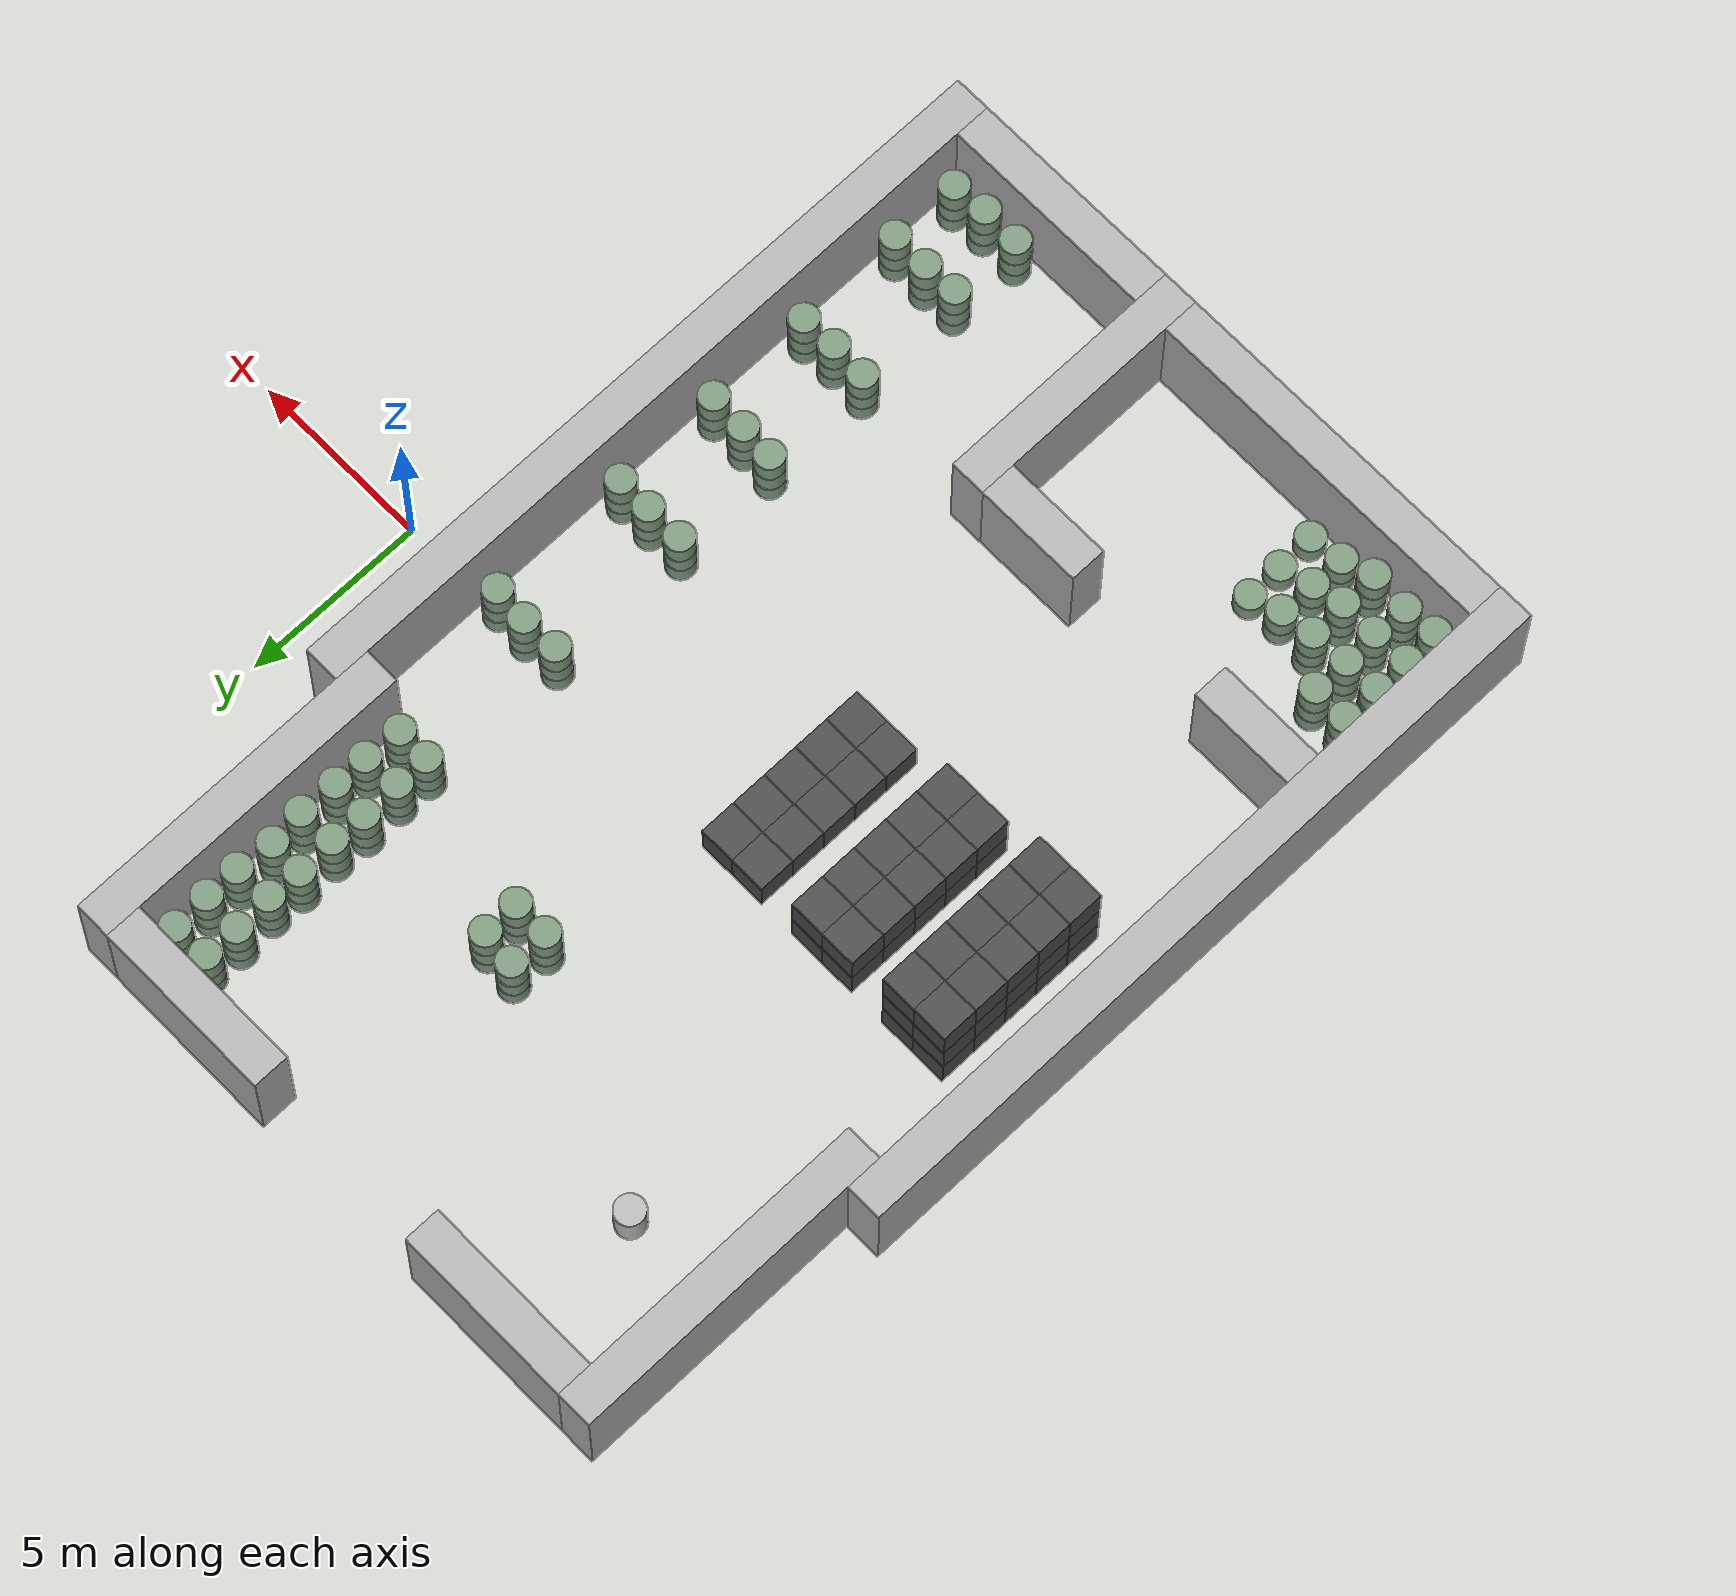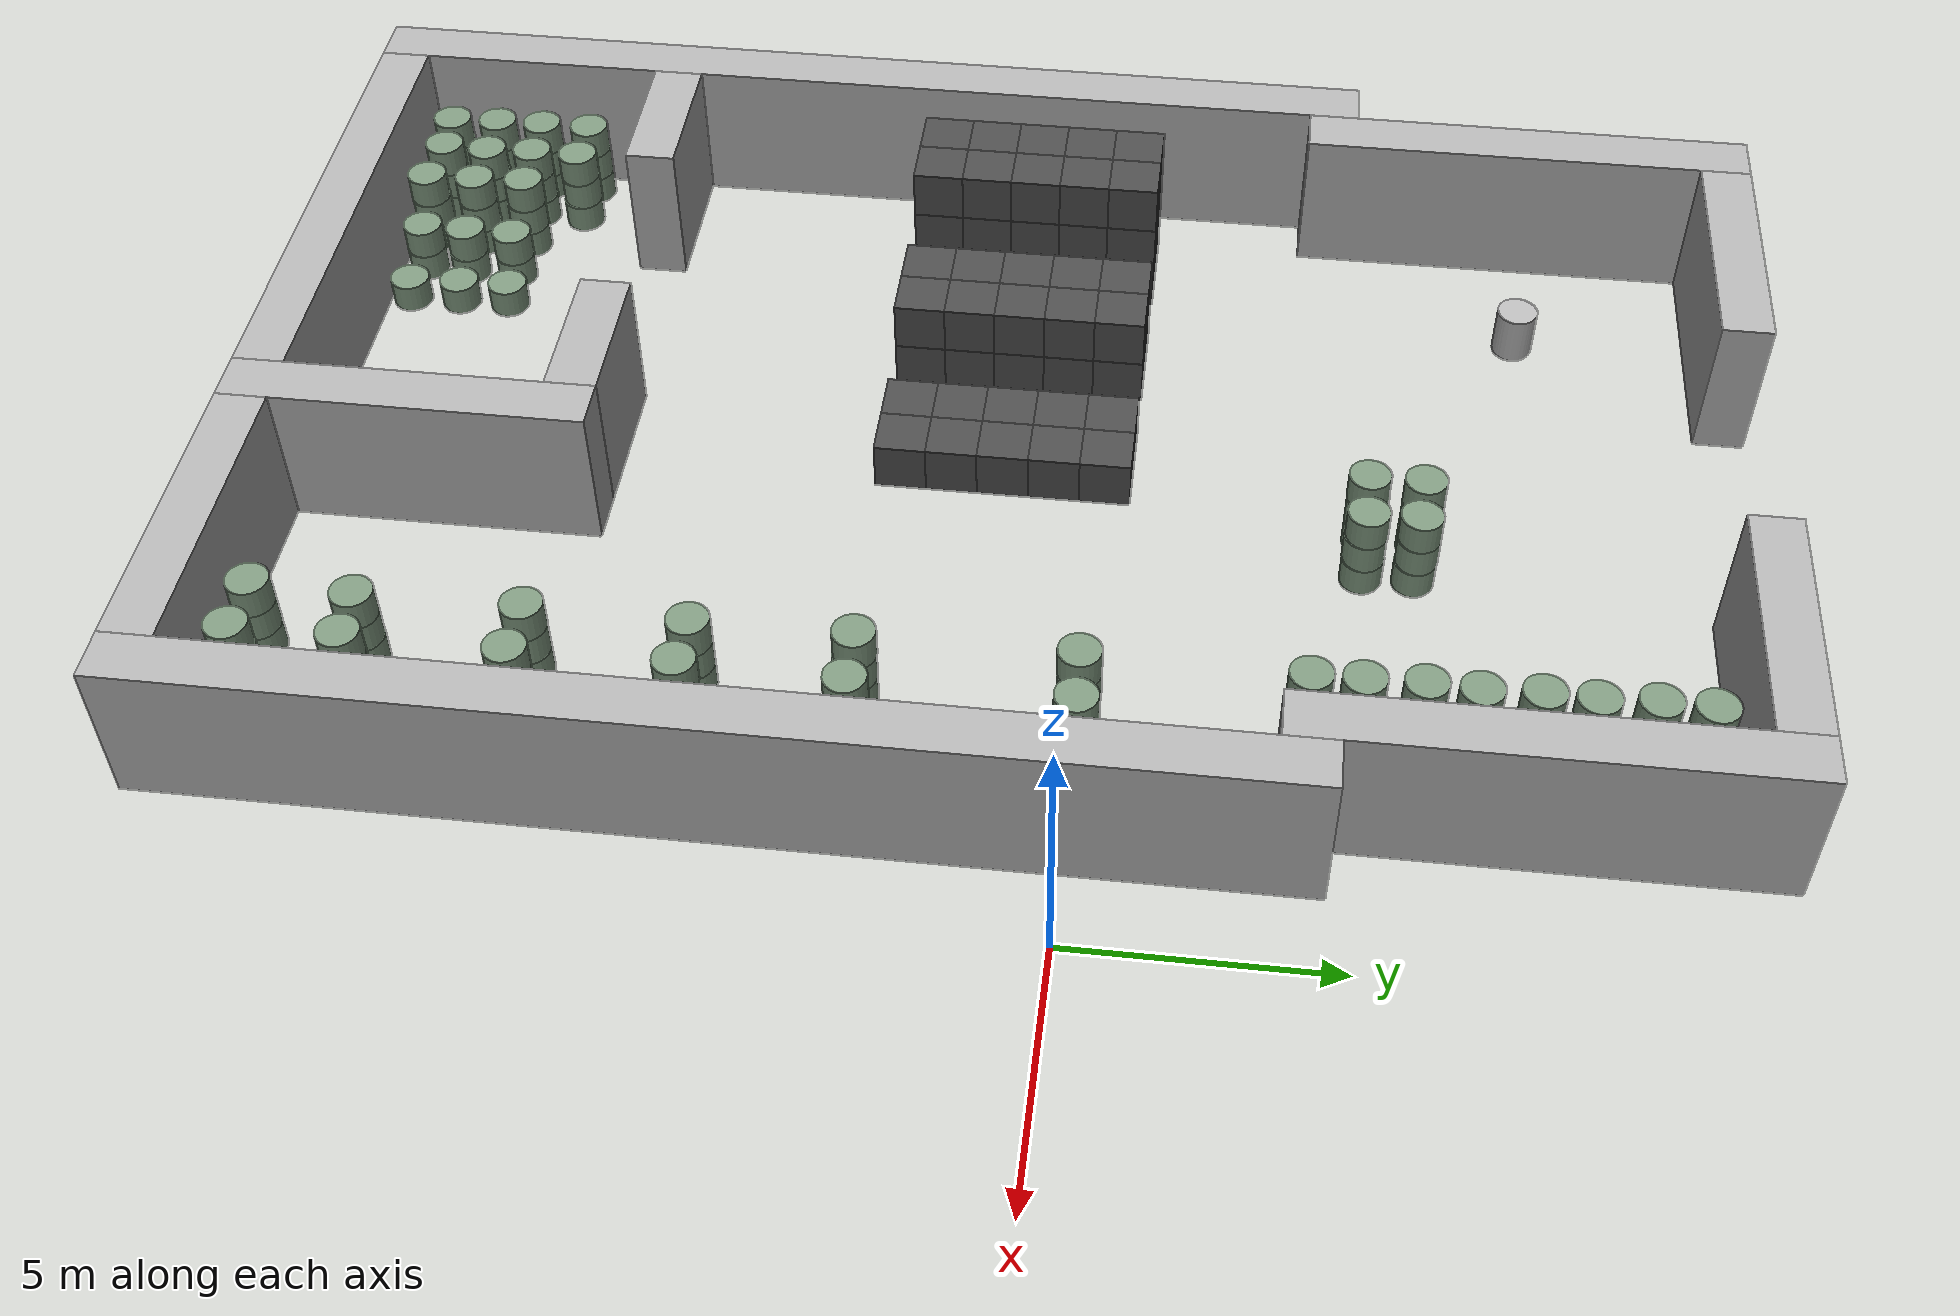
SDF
<sdf version="1.6">
 <world name="default">
  <light name="sun" type="directional">
   <cast_shadows>0</cast_shadows>
   <pose>0 0 10 0 -0 0</pose>
   <diffuse>0.8 0.8 0.8 1</diffuse>
   <specular>0.2 0.2 0.2 1</specular>
   <attenuation>
    <range>1000</range>
    <constant>0.9</constant>
    <linear>0.01</linear>
    <quadratic>0.001</quadratic>
   </attenuation>
   <direction>-0.5 0.1 -0.9</direction>
  </light>
  <gravity>0 0 -9.8</gravity>
  <magnetic_field>6e-06 2.3e-05 -4.2e-05</magnetic_field>
  <atmosphere type="adiabatic"/>
  <physics default="0" name="default_physics" type="ode">
   <max_step_size>0.001</max_step_size>
   <real_time_factor>1</real_time_factor>
   <real_time_update_rate>1000</real_time_update_rate>
  </physics>
  <scene><ambient>0.4 0.4 0.4 1</ambient><background>0.7 0.7 0.7 1</background><shadows>0</shadows></scene>
  <spherical_coordinates>
   <surface_model>EARTH_WGS84</surface_model>
   <latitude_deg>0</latitude_deg>
   <longitude_deg>0</longitude_deg>
   <elevation>0</elevation>
   <heading_deg>0</heading_deg>
  </spherical_coordinates>
  <model name="wall_0">
   <pose frame="sim_world">-20.0 -6.0 1.5 0 0 0</pose>
   <static>True</static>
   <link name="wall_0_link">
    <inertial>
     <mass>100</mass>
     <inertia>
      <ixx>0.166667</ixx>
      <ixy>0</ixy>
      <ixz>0</ixz>
      <iyy>0.166667</iyy>
      <iyz>0</iyz>
      <izz>0.166667</izz>
     </inertia>
    </inertial>
    <collision name="wall_0_collision">
     <geometry><box><size>1.0 21.0 3.0</size></box></geometry>
     <max_contacts>100</max_contacts>
    </collision>
    <visual name="wall_0_visual">
     <geometry><box><size>1.0 21.0 3.0</size></box></geometry>
     <material><ambient>0.7 0.7 0.7 1</ambient><diffuse>0.7 0.7 0.7 1</diffuse></material>
    </visual>
   </link>
  </model>
  <model name="wall_1">
   <pose frame="sim_world">-19.0 8.0 1.5 0 0 0</pose>
   <static>True</static>
   <link name="wall_1_link">
    <inertial>
     <mass>100</mass>
     <inertia>
      <ixx>0.166667</ixx>
      <ixy>0</ixy>
      <ixz>0</ixz>
      <iyy>0.166667</iyy>
      <iyz>0</iyz>
      <izz>0.166667</izz>
     </inertia>
    </inertial>
    <collision name="wall_1_collision">
     <geometry><box><size>1.0 9.0 3.0</size></box></geometry>
     <max_contacts>100</max_contacts>
    </collision>
    <visual name="wall_1_visual">
     <geometry><box><size>1.0 9.0 3.0</size></box></geometry>
     <material><ambient>0.7 0.7 0.7 1</ambient><diffuse>0.7 0.7 0.7 1</diffuse></material>
    </visual>
   </link>
  </model>
  <model name="wall_2">
   <pose frame="sim_world">-9.0 -13.0 1.5 0 0 0</pose>
   <static>True</static>
   <link name="wall_2_link">
    <inertial>
     <mass>100</mass>
     <inertia>
      <ixx>0.166667</ixx>
      <ixy>0</ixy>
      <ixz>0</ixz>
      <iyy>0.166667</iyy>
      <iyz>0</iyz>
      <izz>0.166667</izz>
     </inertia>
    </inertial>
    <collision name="wall_2_collision">
     <geometry><box><size>1.0 7.0 3.0</size></box></geometry>
     <max_contacts>100</max_contacts>
    </collision>
    <visual name="wall_2_visual">
     <geometry><box><size>1.0 7.0 3.0</size></box></geometry>
     <material><ambient>0.7 0.7 0.7 1</ambient><diffuse>0.7 0.7 0.7 1</diffuse></material>
    </visual>
   </link>
  </model>
  <model name="wall_3">
   <pose frame="sim_world">-3.0 8.0 1.5 0 0 0</pose>
   <static>True</static>
   <link name="wall_3_link">
    <inertial>
     <mass>100</mass>
     <inertia>
      <ixx>0.166667</ixx>
      <ixy>0</ixy>
      <ixz>0</ixz>
      <iyy>0.166667</iyy>
      <iyz>0</iyz>
      <izz>0.166667</izz>
     </inertia>
    </inertial>
    <collision name="wall_3_collision">
     <geometry><box><size>1.0 9.0 3.0</size></box></geometry>
     <max_contacts>100</max_contacts>
    </collision>
    <visual name="wall_3_visual">
     <geometry><box><size>1.0 9.0 3.0</size></box></geometry>
     <material><ambient>0.7 0.7 0.7 1</ambient><diffuse>0.7 0.7 0.7 1</diffuse></material>
    </visual>
   </link>
  </model>
  <model name="wall_4">
   <pose frame="sim_world">-2.0 -6.0 1.5 0 0 0</pose>
   <static>True</static>
   <link name="wall_4_link">
    <inertial>
     <mass>100</mass>
     <inertia>
      <ixx>0.166667</ixx>
      <ixy>0</ixy>
      <ixz>0</ixz>
      <iyy>0.166667</iyy>
      <iyz>0</iyz>
      <izz>0.166667</izz>
     </inertia>
    </inertial>
    <collision name="wall_4_collision">
     <geometry><box><size>1.0 21.0 3.0</size></box></geometry>
     <max_contacts>100</max_contacts>
    </collision>
    <visual name="wall_4_visual">
     <geometry><box><size>1.0 21.0 3.0</size></box></geometry>
     <material><ambient>0.7 0.7 0.7 1</ambient><diffuse>0.7 0.7 0.7 1</diffuse></material>
    </visual>
   </link>
  </model>
  <model name="wall_5">
   <pose frame="sim_world">-14.5 -16.0 1.5 0 0 0</pose>
   <static>True</static>
   <link name="wall_5_link">
    <inertial>
     <mass>100</mass>
     <inertia>
      <ixx>0.166667</ixx>
      <ixy>0</ixy>
      <ixz>0</ixz>
      <iyy>0.166667</iyy>
      <iyz>0</iyz>
      <izz>0.166667</izz>
     </inertia>
    </inertial>
    <collision name="wall_5_collision">
     <geometry><box><size>10.0 1.0 3.0</size></box></geometry>
     <max_contacts>100</max_contacts>
    </collision>
    <visual name="wall_5_visual">
     <geometry><box><size>10.0 1.0 3.0</size></box></geometry>
     <material><ambient>0.7 0.7 0.7 1</ambient><diffuse>0.7 0.7 0.7 1</diffuse></material>
    </visual>
   </link>
  </model>
  <model name="wall_6">
   <pose frame="sim_world">-5.5 -16.0 1.5 0 0 0</pose>
   <static>True</static>
   <link name="wall_6_link">
    <inertial>
     <mass>100</mass>
     <inertia>
      <ixx>0.166667</ixx>
      <ixy>0</ixy>
      <ixz>0</ixz>
      <iyy>0.166667</iyy>
      <iyz>0</iyz>
      <izz>0.166667</izz>
     </inertia>
    </inertial>
    <collision name="wall_6_collision">
     <geometry><box><size>6.0 1.0 3.0</size></box></geometry>
     <max_contacts>100</max_contacts>
    </collision>
    <visual name="wall_6_visual">
     <geometry><box><size>6.0 1.0 3.0</size></box></geometry>
     <material><ambient>0.7 0.7 0.7 1</ambient><diffuse>0.7 0.7 0.7 1</diffuse></material>
    </visual>
   </link>
  </model>
  <model name="wall_7">
   <pose frame="sim_world">-18.0 -10.0 1.5 0 0 0</pose>
   <static>True</static>
   <link name="wall_7_link">
    <inertial>
     <mass>100</mass>
     <inertia>
      <ixx>0.166667</ixx>
      <ixy>0</ixy>
      <ixz>0</ixz>
      <iyy>0.166667</iyy>
      <iyz>0</iyz>
      <izz>0.166667</izz>
     </inertia>
    </inertial>
    <collision name="wall_7_collision">
     <geometry><box><size>3.0 1.0 3.0</size></box></geometry>
     <max_contacts>100</max_contacts>
    </collision>
    <visual name="wall_7_visual">
     <geometry><box><size>3.0 1.0 3.0</size></box></geometry>
     <material><ambient>0.7 0.7 0.7 1</ambient><diffuse>0.7 0.7 0.7 1</diffuse></material>
    </visual>
   </link>
  </model>
  <model name="wall_8">
   <pose frame="sim_world">-11.0 -10.0 1.5 0 0 0</pose>
   <static>True</static>
   <link name="wall_8_link">
    <inertial>
     <mass>100</mass>
     <inertia>
      <ixx>0.166667</ixx>
      <ixy>0</ixy>
      <ixz>0</ixz>
      <iyy>0.166667</iyy>
      <iyz>0</iyz>
      <izz>0.166667</izz>
     </inertia>
    </inertial>
    <collision name="wall_8_collision">
     <geometry><box><size>3.0 1.0 3.0</size></box></geometry>
     <max_contacts>100</max_contacts>
    </collision>
    <visual name="wall_8_visual">
     <geometry><box><size>3.0 1.0 3.0</size></box></geometry>
     <material><ambient>0.7 0.7 0.7 1</ambient><diffuse>0.7 0.7 0.7 1</diffuse></material>
    </visual>
   </link>
  </model>
  <model name="wall_9">
   <pose frame="sim_world">-16.0 12.0 1.5 0 0 0</pose>
   <static>True</static>
   <link name="wall_9_link">
    <inertial>
     <mass>100</mass>
     <inertia>
      <ixx>0.166667</ixx>
      <ixy>0</ixy>
      <ixz>0</ixz>
      <iyy>0.166667</iyy>
      <iyz>0</iyz>
      <izz>0.166667</izz>
     </inertia>
    </inertial>
    <collision name="wall_9_collision">
     <geometry><box><size>5.0 1.0 3.0</size></box></geometry>
     <max_contacts>100</max_contacts>
    </collision>
    <visual name="wall_9_visual">
     <geometry><box><size>5.0 1.0 3.0</size></box></geometry>
     <material><ambient>0.7 0.7 0.7 1</ambient><diffuse>0.7 0.7 0.7 1</diffuse></material>
    </visual>
   </link>
  </model>
  <model name="wall_10">
   <pose frame="sim_world">-6.0 12.0 1.5 0 0 0</pose>
   <static>True</static>
   <link name="wall_10_link">
    <inertial>
     <mass>100</mass>
     <inertia>
      <ixx>0.166667</ixx>
      <ixy>0</ixy>
      <ixz>0</ixz>
      <iyy>0.166667</iyy>
      <iyz>0</iyz>
      <izz>0.166667</izz>
     </inertia>
    </inertial>
    <collision name="wall_10_collision">
     <geometry><box><size>5.0 1.0 3.0</size></box></geometry>
     <max_contacts>100</max_contacts>
    </collision>
    <visual name="wall_10_visual">
     <geometry><box><size>5.0 1.0 3.0</size></box></geometry>
     <material><ambient>0.7 0.7 0.7 1</ambient><diffuse>0.7 0.7 0.7 1</diffuse></material>
    </visual>
   </link>
  </model>
  <model name="box_0">
   <pose frame="sim_world">-18.0 -4.0 0.5 0 -0 0</pose>
   <static>True</static>
   <link name="box_0_link">
    <inertial>
     <mass>100</mass>
     <inertia>
      <ixx>0.166667</ixx>
      <ixy>0</ixy>
      <ixz>0</ixz>
      <iyy>0.166667</iyy>
      <iyz>0</iyz>
      <izz>0.166667</izz>
     </inertia>
    </inertial>
    <collision name="box_0_collision">
     <geometry><box><size>1.0 1.0 1.0</size></box></geometry>
     <max_contacts>100</max_contacts>
    </collision>
    <visual name="box_0_visual">
     <geometry><box><size>1.0 1.0 1.0</size></box></geometry>
     <material><ambient>0.3 0.3 0.3 1</ambient><diffuse>0.3 0.3 0.3 1</diffuse></material>
    </visual>
   </link>
  </model>
  <model name="box_1">
   <pose frame="sim_world">-18.0 -4.0 1.5 0 -0 0</pose>
   <static>True</static>
   <link name="box_1_link">
    <inertial>
     <mass>100</mass>
     <inertia>
      <ixx>0.166667</ixx>
      <ixy>0</ixy>
      <ixz>0</ixz>
      <iyy>0.166667</iyy>
      <iyz>0</iyz>
      <izz>0.166667</izz>
     </inertia>
    </inertial>
    <collision name="box_1_collision">
     <geometry><box><size>1.0 1.0 1.0</size></box></geometry>
     <max_contacts>100</max_contacts>
    </collision>
    <visual name="box_1_visual">
     <geometry><box><size>1.0 1.0 1.0</size></box></geometry>
     <material><ambient>0.3 0.3 0.3 1</ambient><diffuse>0.3 0.3 0.3 1</diffuse></material>
    </visual>
   </link>
  </model>
  <model name="box_2">
   <pose frame="sim_world">-18.0 -4.0 2.5 0 -0 0</pose>
   <static>True</static>
   <link name="box_2_link">
    <inertial>
     <mass>100</mass>
     <inertia>
      <ixx>0.166667</ixx>
      <ixy>0</ixy>
      <ixz>0</ixz>
      <iyy>0.166667</iyy>
      <iyz>0</iyz>
      <izz>0.166667</izz>
     </inertia>
    </inertial>
    <collision name="box_2_collision">
     <geometry><box><size>1.0 1.0 1.0</size></box></geometry>
     <max_contacts>100</max_contacts>
    </collision>
    <visual name="box_2_visual">
     <geometry><box><size>1.0 1.0 1.0</size></box></geometry>
     <material><ambient>0.3 0.3 0.3 1</ambient><diffuse>0.3 0.3 0.3 1</diffuse></material>
    </visual>
   </link>
  </model>
  <model name="box_3">
   <pose frame="sim_world">-18.0 -3.0 0.5 0 -0 0</pose>
   <static>True</static>
   <link name="box_3_link">
    <inertial>
     <mass>100</mass>
     <inertia>
      <ixx>0.166667</ixx>
      <ixy>0</ixy>
      <ixz>0</ixz>
      <iyy>0.166667</iyy>
      <iyz>0</iyz>
      <izz>0.166667</izz>
     </inertia>
    </inertial>
    <collision name="box_3_collision">
     <geometry><box><size>1.0 1.0 1.0</size></box></geometry>
     <max_contacts>100</max_contacts>
    </collision>
    <visual name="box_3_visual">
     <geometry><box><size>1.0 1.0 1.0</size></box></geometry>
     <material><ambient>0.3 0.3 0.3 1</ambient><diffuse>0.3 0.3 0.3 1</diffuse></material>
    </visual>
   </link>
  </model>
  <model name="box_4">
   <pose frame="sim_world">-18.0 -3.0 1.5 0 -0 0</pose>
   <static>True</static>
   <link name="box_4_link">
    <inertial>
     <mass>100</mass>
     <inertia>
      <ixx>0.166667</ixx>
      <ixy>0</ixy>
      <ixz>0</ixz>
      <iyy>0.166667</iyy>
      <iyz>0</iyz>
      <izz>0.166667</izz>
     </inertia>
    </inertial>
    <collision name="box_4_collision">
     <geometry><box><size>1.0 1.0 1.0</size></box></geometry>
     <max_contacts>100</max_contacts>
    </collision>
    <visual name="box_4_visual">
     <geometry><box><size>1.0 1.0 1.0</size></box></geometry>
     <material><ambient>0.3 0.3 0.3 1</ambient><diffuse>0.3 0.3 0.3 1</diffuse></material>
    </visual>
   </link>
  </model>
  <model name="box_5">
   <pose frame="sim_world">-18.0 -3.0 2.5 0 -0 0</pose>
   <static>True</static>
   <link name="box_5_link">
    <inertial>
     <mass>100</mass>
     <inertia>
      <ixx>0.166667</ixx>
      <ixy>0</ixy>
      <ixz>0</ixz>
      <iyy>0.166667</iyy>
      <iyz>0</iyz>
      <izz>0.166667</izz>
     </inertia>
    </inertial>
    <collision name="box_5_collision">
     <geometry><box><size>1.0 1.0 1.0</size></box></geometry>
     <max_contacts>100</max_contacts>
    </collision>
    <visual name="box_5_visual">
     <geometry><box><size>1.0 1.0 1.0</size></box></geometry>
     <material><ambient>0.3 0.3 0.3 1</ambient><diffuse>0.3 0.3 0.3 1</diffuse></material>
    </visual>
   </link>
  </model>
  <model name="box_6">
   <pose frame="sim_world">-18.0 -2.0 0.5 0 -0 0</pose>
   <static>True</static>
   <link name="box_6_link">
    <inertial>
     <mass>100</mass>
     <inertia>
      <ixx>0.166667</ixx>
      <ixy>0</ixy>
      <ixz>0</ixz>
      <iyy>0.166667</iyy>
      <iyz>0</iyz>
      <izz>0.166667</izz>
     </inertia>
    </inertial>
    <collision name="box_6_collision">
     <geometry><box><size>1.0 1.0 1.0</size></box></geometry>
     <max_contacts>100</max_contacts>
    </collision>
    <visual name="box_6_visual">
     <geometry><box><size>1.0 1.0 1.0</size></box></geometry>
     <material><ambient>0.3 0.3 0.3 1</ambient><diffuse>0.3 0.3 0.3 1</diffuse></material>
    </visual>
   </link>
  </model>
  <model name="box_7">
   <pose frame="sim_world">-18.0 -2.0 1.5 0 -0 0</pose>
   <static>True</static>
   <link name="box_7_link">
    <inertial>
     <mass>100</mass>
     <inertia>
      <ixx>0.166667</ixx>
      <ixy>0</ixy>
      <ixz>0</ixz>
      <iyy>0.166667</iyy>
      <iyz>0</iyz>
      <izz>0.166667</izz>
     </inertia>
    </inertial>
    <collision name="box_7_collision">
     <geometry><box><size>1.0 1.0 1.0</size></box></geometry>
     <max_contacts>100</max_contacts>
    </collision>
    <visual name="box_7_visual">
     <geometry><box><size>1.0 1.0 1.0</size></box></geometry>
     <material><ambient>0.3 0.3 0.3 1</ambient><diffuse>0.3 0.3 0.3 1</diffuse></material>
    </visual>
   </link>
  </model>
  <model name="box_8">
   <pose frame="sim_world">-18.0 -2.0 2.5 0 -0 0</pose>
   <static>True</static>
   <link name="box_8_link">
    <inertial>
     <mass>100</mass>
     <inertia>
      <ixx>0.166667</ixx>
      <ixy>0</ixy>
      <ixz>0</ixz>
      <iyy>0.166667</iyy>
      <iyz>0</iyz>
      <izz>0.166667</izz>
     </inertia>
    </inertial>
    <collision name="box_8_collision">
     <geometry><box><size>1.0 1.0 1.0</size></box></geometry>
     <max_contacts>100</max_contacts>
    </collision>
    <visual name="box_8_visual">
     <geometry><box><size>1.0 1.0 1.0</size></box></geometry>
     <material><ambient>0.3 0.3 0.3 1</ambient><diffuse>0.3 0.3 0.3 1</diffuse></material>
    </visual>
   </link>
  </model>
  <model name="box_9">
   <pose frame="sim_world">-18.0 -1.0 0.5 0 -0 0</pose>
   <static>True</static>
   <link name="box_9_link">
    <inertial>
     <mass>100</mass>
     <inertia>
      <ixx>0.166667</ixx>
      <ixy>0</ixy>
      <ixz>0</ixz>
      <iyy>0.166667</iyy>
      <iyz>0</iyz>
      <izz>0.166667</izz>
     </inertia>
    </inertial>
    <collision name="box_9_collision">
     <geometry><box><size>1.0 1.0 1.0</size></box></geometry>
     <max_contacts>100</max_contacts>
    </collision>
    <visual name="box_9_visual">
     <geometry><box><size>1.0 1.0 1.0</size></box></geometry>
     <material><ambient>0.3 0.3 0.3 1</ambient><diffuse>0.3 0.3 0.3 1</diffuse></material>
    </visual>
   </link>
  </model>
  <model name="box_10">
   <pose frame="sim_world">-18.0 -1.0 1.5 0 -0 0</pose>
   <static>True</static>
   <link name="box_10_link">
    <inertial>
     <mass>100</mass>
     <inertia>
      <ixx>0.166667</ixx>
      <ixy>0</ixy>
      <ixz>0</ixz>
      <iyy>0.166667</iyy>
      <iyz>0</iyz>
      <izz>0.166667</izz>
     </inertia>
    </inertial>
    <collision name="box_10_collision">
     <geometry><box><size>1.0 1.0 1.0</size></box></geometry>
     <max_contacts>100</max_contacts>
    </collision>
    <visual name="box_10_visual">
     <geometry><box><size>1.0 1.0 1.0</size></box></geometry>
     <material><ambient>0.3 0.3 0.3 1</ambient><diffuse>0.3 0.3 0.3 1</diffuse></material>
    </visual>
   </link>
  </model>
  <model name="box_11">
   <pose frame="sim_world">-18.0 -1.0 2.5 0 -0 0</pose>
   <static>True</static>
   <link name="box_11_link">
    <inertial>
     <mass>100</mass>
     <inertia>
      <ixx>0.166667</ixx>
      <ixy>0</ixy>
      <ixz>0</ixz>
      <iyy>0.166667</iyy>
      <iyz>0</iyz>
      <izz>0.166667</izz>
     </inertia>
    </inertial>
    <collision name="box_11_collision">
     <geometry><box><size>1.0 1.0 1.0</size></box></geometry>
     <max_contacts>100</max_contacts>
    </collision>
    <visual name="box_11_visual">
     <geometry><box><size>1.0 1.0 1.0</size></box></geometry>
     <material><ambient>0.3 0.3 0.3 1</ambient><diffuse>0.3 0.3 0.3 1</diffuse></material>
    </visual>
   </link>
  </model>
  <model name="box_12">
   <pose frame="sim_world">-18.0 0.0 0.5 0 -0 0</pose>
   <static>True</static>
   <link name="box_12_link">
    <inertial>
     <mass>100</mass>
     <inertia>
      <ixx>0.166667</ixx>
      <ixy>0</ixy>
      <ixz>0</ixz>
      <iyy>0.166667</iyy>
      <iyz>0</iyz>
      <izz>0.166667</izz>
     </inertia>
    </inertial>
    <collision name="box_12_collision">
     <geometry><box><size>1.0 1.0 1.0</size></box></geometry>
     <max_contacts>100</max_contacts>
    </collision>
    <visual name="box_12_visual">
     <geometry><box><size>1.0 1.0 1.0</size></box></geometry>
     <material><ambient>0.3 0.3 0.3 1</ambient><diffuse>0.3 0.3 0.3 1</diffuse></material>
    </visual>
   </link>
  </model>
  <model name="box_13">
   <pose frame="sim_world">-18.0 0.0 1.5 0 -0 0</pose>
   <static>True</static>
   <link name="box_13_link">
    <inertial>
     <mass>100</mass>
     <inertia>
      <ixx>0.166667</ixx>
      <ixy>0</ixy>
      <ixz>0</ixz>
      <iyy>0.166667</iyy>
      <iyz>0</iyz>
      <izz>0.166667</izz>
     </inertia>
    </inertial>
    <collision name="box_13_collision">
     <geometry><box><size>1.0 1.0 1.0</size></box></geometry>
     <max_contacts>100</max_contacts>
    </collision>
    <visual name="box_13_visual">
     <geometry><box><size>1.0 1.0 1.0</size></box></geometry>
     <material><ambient>0.3 0.3 0.3 1</ambient><diffuse>0.3 0.3 0.3 1</diffuse></material>
    </visual>
   </link>
  </model>
  <model name="box_14">
   <pose frame="sim_world">-18.0 0.0 2.5 0 -0 0</pose>
   <static>True</static>
   <link name="box_14_link">
    <inertial>
     <mass>100</mass>
     <inertia>
      <ixx>0.166667</ixx>
      <ixy>0</ixy>
      <ixz>0</ixz>
      <iyy>0.166667</iyy>
      <iyz>0</iyz>
      <izz>0.166667</izz>
     </inertia>
    </inertial>
    <collision name="box_14_collision">
     <geometry><box><size>1.0 1.0 1.0</size></box></geometry>
     <max_contacts>100</max_contacts>
    </collision>
    <visual name="box_14_visual">
     <geometry><box><size>1.0 1.0 1.0</size></box></geometry>
     <material><ambient>0.3 0.3 0.3 1</ambient><diffuse>0.3 0.3 0.3 1</diffuse></material>
    </visual>
   </link>
  </model>
  <model name="box_15">
   <pose frame="sim_world">-17.0 -4.0 0.5 0 -0 0</pose>
   <static>True</static>
   <link name="box_15_link">
    <inertial>
     <mass>100</mass>
     <inertia>
      <ixx>0.166667</ixx>
      <ixy>0</ixy>
      <ixz>0</ixz>
      <iyy>0.166667</iyy>
      <iyz>0</iyz>
      <izz>0.166667</izz>
     </inertia>
    </inertial>
    <collision name="box_15_collision">
     <geometry><box><size>1.0 1.0 1.0</size></box></geometry>
     <max_contacts>100</max_contacts>
    </collision>
    <visual name="box_15_visual">
     <geometry><box><size>1.0 1.0 1.0</size></box></geometry>
     <material><ambient>0.3 0.3 0.3 1</ambient><diffuse>0.3 0.3 0.3 1</diffuse></material>
    </visual>
   </link>
  </model>
  <model name="box_16">
   <pose frame="sim_world">-17.0 -4.0 1.5 0 -0 0</pose>
   <static>True</static>
   <link name="box_16_link">
    <inertial>
     <mass>100</mass>
     <inertia>
      <ixx>0.166667</ixx>
      <ixy>0</ixy>
      <ixz>0</ixz>
      <iyy>0.166667</iyy>
      <iyz>0</iyz>
      <izz>0.166667</izz>
     </inertia>
    </inertial>
    <collision name="box_16_collision">
     <geometry><box><size>1.0 1.0 1.0</size></box></geometry>
     <max_contacts>100</max_contacts>
    </collision>
    <visual name="box_16_visual">
     <geometry><box><size>1.0 1.0 1.0</size></box></geometry>
     <material><ambient>0.3 0.3 0.3 1</ambient><diffuse>0.3 0.3 0.3 1</diffuse></material>
    </visual>
   </link>
  </model>
  <model name="box_17">
   <pose frame="sim_world">-17.0 -4.0 2.5 0 -0 0</pose>
   <static>True</static>
   <link name="box_17_link">
    <inertial>
     <mass>100</mass>
     <inertia>
      <ixx>0.166667</ixx>
      <ixy>0</ixy>
      <ixz>0</ixz>
      <iyy>0.166667</iyy>
      <iyz>0</iyz>
      <izz>0.166667</izz>
     </inertia>
    </inertial>
    <collision name="box_17_collision">
     <geometry><box><size>1.0 1.0 1.0</size></box></geometry>
     <max_contacts>100</max_contacts>
    </collision>
    <visual name="box_17_visual">
     <geometry><box><size>1.0 1.0 1.0</size></box></geometry>
     <material><ambient>0.3 0.3 0.3 1</ambient><diffuse>0.3 0.3 0.3 1</diffuse></material>
    </visual>
   </link>
  </model>
  <model name="box_18">
   <pose frame="sim_world">-17.0 -3.0 0.5 0 -0 0</pose>
   <static>True</static>
   <link name="box_18_link">
    <inertial>
     <mass>100</mass>
     <inertia>
      <ixx>0.166667</ixx>
      <ixy>0</ixy>
      <ixz>0</ixz>
      <iyy>0.166667</iyy>
      <iyz>0</iyz>
      <izz>0.166667</izz>
     </inertia>
    </inertial>
    <collision name="box_18_collision">
     <geometry><box><size>1.0 1.0 1.0</size></box></geometry>
     <max_contacts>100</max_contacts>
    </collision>
    <visual name="box_18_visual">
     <geometry><box><size>1.0 1.0 1.0</size></box></geometry>
     <material><ambient>0.3 0.3 0.3 1</ambient><diffuse>0.3 0.3 0.3 1</diffuse></material>
    </visual>
   </link>
  </model>
  <model name="box_19">
   <pose frame="sim_world">-17.0 -3.0 1.5 0 -0 0</pose>
   <static>True</static>
   <link name="box_19_link">
    <inertial>
     <mass>100</mass>
     <inertia>
      <ixx>0.166667</ixx>
      <ixy>0</ixy>
      <ixz>0</ixz>
      <iyy>0.166667</iyy>
      <iyz>0</iyz>
      <izz>0.166667</izz>
     </inertia>
    </inertial>
    <collision name="box_19_collision">
     <geometry><box><size>1.0 1.0 1.0</size></box></geometry>
     <max_contacts>100</max_contacts>
    </collision>
    <visual name="box_19_visual">
     <geometry><box><size>1.0 1.0 1.0</size></box></geometry>
     <material><ambient>0.3 0.3 0.3 1</ambient><diffuse>0.3 0.3 0.3 1</diffuse></material>
    </visual>
   </link>
  </model>
  <model name="box_20">
   <pose frame="sim_world">-17.0 -3.0 2.5 0 -0 0</pose>
   <static>True</static>
   <link name="box_20_link">
    <inertial>
     <mass>100</mass>
     <inertia>
      <ixx>0.166667</ixx>
      <ixy>0</ixy>
      <ixz>0</ixz>
      <iyy>0.166667</iyy>
      <iyz>0</iyz>
      <izz>0.166667</izz>
     </inertia>
    </inertial>
    <collision name="box_20_collision">
     <geometry><box><size>1.0 1.0 1.0</size></box></geometry>
     <max_contacts>100</max_contacts>
    </collision>
    <visual name="box_20_visual">
     <geometry><box><size>1.0 1.0 1.0</size></box></geometry>
     <material><ambient>0.3 0.3 0.3 1</ambient><diffuse>0.3 0.3 0.3 1</diffuse></material>
    </visual>
   </link>
  </model>
  <model name="box_21">
   <pose frame="sim_world">-17.0 -2.0 0.5 0 -0 0</pose>
   <static>True</static>
   <link name="box_21_link">
    <inertial>
     <mass>100</mass>
     <inertia>
      <ixx>0.166667</ixx>
      <ixy>0</ixy>
      <ixz>0</ixz>
      <iyy>0.166667</iyy>
      <iyz>0</iyz>
      <izz>0.166667</izz>
     </inertia>
    </inertial>
    <collision name="box_21_collision">
     <geometry><box><size>1.0 1.0 1.0</size></box></geometry>
     <max_contacts>100</max_contacts>
    </collision>
    <visual name="box_21_visual">
     <geometry><box><size>1.0 1.0 1.0</size></box></geometry>
     <material><ambient>0.3 0.3 0.3 1</ambient><diffuse>0.3 0.3 0.3 1</diffuse></material>
    </visual>
   </link>
  </model>
  <model name="box_22">
   <pose frame="sim_world">-17.0 -2.0 1.5 0 -0 0</pose>
   <static>True</static>
   <link name="box_22_link">
    <inertial>
     <mass>100</mass>
     <inertia>
      <ixx>0.166667</ixx>
      <ixy>0</ixy>
      <ixz>0</ixz>
      <iyy>0.166667</iyy>
      <iyz>0</iyz>
      <izz>0.166667</izz>
     </inertia>
    </inertial>
    <collision name="box_22_collision">
     <geometry><box><size>1.0 1.0 1.0</size></box></geometry>
     <max_contacts>100</max_contacts>
    </collision>
    <visual name="box_22_visual">
     <geometry><box><size>1.0 1.0 1.0</size></box></geometry>
     <material><ambient>0.3 0.3 0.3 1</ambient><diffuse>0.3 0.3 0.3 1</diffuse></material>
    </visual>
   </link>
  </model>
  <model name="box_23">
   <pose frame="sim_world">-17.0 -2.0 2.5 0 -0 0</pose>
   <static>True</static>
   <link name="box_23_link">
    <inertial>
     <mass>100</mass>
     <inertia>
      <ixx>0.166667</ixx>
      <ixy>0</ixy>
      <ixz>0</ixz>
      <iyy>0.166667</iyy>
      <iyz>0</iyz>
      <izz>0.166667</izz>
     </inertia>
    </inertial>
    <collision name="box_23_collision">
     <geometry><box><size>1.0 1.0 1.0</size></box></geometry>
     <max_contacts>100</max_contacts>
    </collision>
    <visual name="box_23_visual">
     <geometry><box><size>1.0 1.0 1.0</size></box></geometry>
     <material><ambient>0.3 0.3 0.3 1</ambient><diffuse>0.3 0.3 0.3 1</diffuse></material>
    </visual>
   </link>
  </model>
  <model name="box_24">
   <pose frame="sim_world">-17.0 -1.0 0.5 0 -0 0</pose>
   <static>True</static>
   <link name="box_24_link">
    <inertial>
     <mass>100</mass>
     <inertia>
      <ixx>0.166667</ixx>
      <ixy>0</ixy>
      <ixz>0</ixz>
      <iyy>0.166667</iyy>
      <iyz>0</iyz>
      <izz>0.166667</izz>
     </inertia>
    </inertial>
    <collision name="box_24_collision">
     <geometry><box><size>1.0 1.0 1.0</size></box></geometry>
     <max_contacts>100</max_contacts>
    </collision>
    <visual name="box_24_visual">
     <geometry><box><size>1.0 1.0 1.0</size></box></geometry>
     <material><ambient>0.3 0.3 0.3 1</ambient><diffuse>0.3 0.3 0.3 1</diffuse></material>
    </visual>
   </link>
  </model>
  <model name="box_25">
   <pose frame="sim_world">-17.0 -1.0 1.5 0 -0 0</pose>
   <static>True</static>
   <link name="box_25_link">
    <inertial>
     <mass>100</mass>
     <inertia>
      <ixx>0.166667</ixx>
      <ixy>0</ixy>
      <ixz>0</ixz>
      <iyy>0.166667</iyy>
      <iyz>0</iyz>
      <izz>0.166667</izz>
     </inertia>
    </inertial>
    <collision name="box_25_collision">
     <geometry><box><size>1.0 1.0 1.0</size></box></geometry>
     <max_contacts>100</max_contacts>
    </collision>
    <visual name="box_25_visual">
     <geometry><box><size>1.0 1.0 1.0</size></box></geometry>
     <material><ambient>0.3 0.3 0.3 1</ambient><diffuse>0.3 0.3 0.3 1</diffuse></material>
    </visual>
   </link>
  </model>
  <model name="box_26">
   <pose frame="sim_world">-17.0 -1.0 2.5 0 -0 0</pose>
   <static>True</static>
   <link name="box_26_link">
    <inertial>
     <mass>100</mass>
     <inertia>
      <ixx>0.166667</ixx>
      <ixy>0</ixy>
      <ixz>0</ixz>
      <iyy>0.166667</iyy>
      <iyz>0</iyz>
      <izz>0.166667</izz>
     </inertia>
    </inertial>
    <collision name="box_26_collision">
     <geometry><box><size>1.0 1.0 1.0</size></box></geometry>
     <max_contacts>100</max_contacts>
    </collision>
    <visual name="box_26_visual">
     <geometry><box><size>1.0 1.0 1.0</size></box></geometry>
     <material><ambient>0.3 0.3 0.3 1</ambient><diffuse>0.3 0.3 0.3 1</diffuse></material>
    </visual>
   </link>
  </model>
  <model name="box_27">
   <pose frame="sim_world">-17.0 0.0 0.5 0 -0 0</pose>
   <static>True</static>
   <link name="box_27_link">
    <inertial>
     <mass>100</mass>
     <inertia>
      <ixx>0.166667</ixx>
      <ixy>0</ixy>
      <ixz>0</ixz>
      <iyy>0.166667</iyy>
      <iyz>0</iyz>
      <izz>0.166667</izz>
     </inertia>
    </inertial>
    <collision name="box_27_collision">
     <geometry><box><size>1.0 1.0 1.0</size></box></geometry>
     <max_contacts>100</max_contacts>
    </collision>
    <visual name="box_27_visual">
     <geometry><box><size>1.0 1.0 1.0</size></box></geometry>
     <material><ambient>0.3 0.3 0.3 1</ambient><diffuse>0.3 0.3 0.3 1</diffuse></material>
    </visual>
   </link>
  </model>
  <model name="box_28">
   <pose frame="sim_world">-17.0 0.0 1.5 0 -0 0</pose>
   <static>True</static>
   <link name="box_28_link">
    <inertial>
     <mass>100</mass>
     <inertia>
      <ixx>0.166667</ixx>
      <ixy>0</ixy>
      <ixz>0</ixz>
      <iyy>0.166667</iyy>
      <iyz>0</iyz>
      <izz>0.166667</izz>
     </inertia>
    </inertial>
    <collision name="box_28_collision">
     <geometry><box><size>1.0 1.0 1.0</size></box></geometry>
     <max_contacts>100</max_contacts>
    </collision>
    <visual name="box_28_visual">
     <geometry><box><size>1.0 1.0 1.0</size></box></geometry>
     <material><ambient>0.3 0.3 0.3 1</ambient><diffuse>0.3 0.3 0.3 1</diffuse></material>
    </visual>
   </link>
  </model>
  <model name="box_29">
   <pose frame="sim_world">-17.0 0.0 2.5 0 -0 0</pose>
   <static>True</static>
   <link name="box_29_link">
    <inertial>
     <mass>100</mass>
     <inertia>
      <ixx>0.166667</ixx>
      <ixy>0</ixy>
      <ixz>0</ixz>
      <iyy>0.166667</iyy>
      <iyz>0</iyz>
      <izz>0.166667</izz>
     </inertia>
    </inertial>
    <collision name="box_29_collision">
     <geometry><box><size>1.0 1.0 1.0</size></box></geometry>
     <max_contacts>100</max_contacts>
    </collision>
    <visual name="box_29_visual">
     <geometry><box><size>1.0 1.0 1.0</size></box></geometry>
     <material><ambient>0.3 0.3 0.3 1</ambient><diffuse>0.3 0.3 0.3 1</diffuse></material>
    </visual>
   </link>
  </model>
  <model name="box_30">
   <pose frame="sim_world">-15.0 -4.0 0.5 0 -0 0</pose>
   <static>True</static>
   <link name="box_30_link">
    <inertial>
     <mass>100</mass>
     <inertia>
      <ixx>0.166667</ixx>
      <ixy>0</ixy>
      <ixz>0</ixz>
      <iyy>0.166667</iyy>
      <iyz>0</iyz>
      <izz>0.166667</izz>
     </inertia>
    </inertial>
    <collision name="box_30_collision">
     <geometry><box><size>1.0 1.0 1.0</size></box></geometry>
     <max_contacts>100</max_contacts>
    </collision>
    <visual name="box_30_visual">
     <geometry><box><size>1.0 1.0 1.0</size></box></geometry>
     <material><ambient>0.3 0.3 0.3 1</ambient><diffuse>0.3 0.3 0.3 1</diffuse></material>
    </visual>
   </link>
  </model>
  <model name="box_31">
   <pose frame="sim_world">-15.0 -4.0 1.5 0 -0 0</pose>
   <static>True</static>
   <link name="box_31_link">
    <inertial>
     <mass>100</mass>
     <inertia>
      <ixx>0.166667</ixx>
      <ixy>0</ixy>
      <ixz>0</ixz>
      <iyy>0.166667</iyy>
      <iyz>0</iyz>
      <izz>0.166667</izz>
     </inertia>
    </inertial>
    <collision name="box_31_collision">
     <geometry><box><size>1.0 1.0 1.0</size></box></geometry>
     <max_contacts>100</max_contacts>
    </collision>
    <visual name="box_31_visual">
     <geometry><box><size>1.0 1.0 1.0</size></box></geometry>
     <material><ambient>0.3 0.3 0.3 1</ambient><diffuse>0.3 0.3 0.3 1</diffuse></material>
    </visual>
   </link>
  </model>
  <model name="box_32">
   <pose frame="sim_world">-15.0 -3.0 0.5 0 -0 0</pose>
   <static>True</static>
   <link name="box_32_link">
    <inertial>
     <mass>100</mass>
     <inertia>
      <ixx>0.166667</ixx>
      <ixy>0</ixy>
      <ixz>0</ixz>
      <iyy>0.166667</iyy>
      <iyz>0</iyz>
      <izz>0.166667</izz>
     </inertia>
    </inertial>
    <collision name="box_32_collision">
     <geometry><box><size>1.0 1.0 1.0</size></box></geometry>
     <max_contacts>100</max_contacts>
    </collision>
    <visual name="box_32_visual">
     <geometry><box><size>1.0 1.0 1.0</size></box></geometry>
     <material><ambient>0.3 0.3 0.3 1</ambient><diffuse>0.3 0.3 0.3 1</diffuse></material>
    </visual>
   </link>
  </model>
  <model name="box_33">
   <pose frame="sim_world">-15.0 -3.0 1.5 0 -0 0</pose>
   <static>True</static>
   <link name="box_33_link">
    <inertial>
     <mass>100</mass>
     <inertia>
      <ixx>0.166667</ixx>
      <ixy>0</ixy>
      <ixz>0</ixz>
      <iyy>0.166667</iyy>
      <iyz>0</iyz>
      <izz>0.166667</izz>
     </inertia>
    </inertial>
    <collision name="box_33_collision">
     <geometry><box><size>1.0 1.0 1.0</size></box></geometry>
     <max_contacts>100</max_contacts>
    </collision>
    <visual name="box_33_visual">
     <geometry><box><size>1.0 1.0 1.0</size></box></geometry>
     <material><ambient>0.3 0.3 0.3 1</ambient><diffuse>0.3 0.3 0.3 1</diffuse></material>
    </visual>
   </link>
  </model>
  <model name="box_34">
   <pose frame="sim_world">-15.0 -2.0 0.5 0 -0 0</pose>
   <static>True</static>
   <link name="box_34_link">
    <inertial>
     <mass>100</mass>
     <inertia>
      <ixx>0.166667</ixx>
      <ixy>0</ixy>
      <ixz>0</ixz>
      <iyy>0.166667</iyy>
      <iyz>0</iyz>
      <izz>0.166667</izz>
     </inertia>
    </inertial>
    <collision name="box_34_collision">
     <geometry><box><size>1.0 1.0 1.0</size></box></geometry>
     <max_contacts>100</max_contacts>
    </collision>
    <visual name="box_34_visual">
     <geometry><box><size>1.0 1.0 1.0</size></box></geometry>
     <material><ambient>0.3 0.3 0.3 1</ambient><diffuse>0.3 0.3 0.3 1</diffuse></material>
    </visual>
   </link>
  </model>
  <model name="box_35">
   <pose frame="sim_world">-15.0 -2.0 1.5 0 -0 0</pose>
   <static>True</static>
   <link name="box_35_link">
    <inertial>
     <mass>100</mass>
     <inertia>
      <ixx>0.166667</ixx>
      <ixy>0</ixy>
      <ixz>0</ixz>
      <iyy>0.166667</iyy>
      <iyz>0</iyz>
      <izz>0.166667</izz>
     </inertia>
    </inertial>
    <collision name="box_35_collision">
     <geometry><box><size>1.0 1.0 1.0</size></box></geometry>
     <max_contacts>100</max_contacts>
    </collision>
    <visual name="box_35_visual">
     <geometry><box><size>1.0 1.0 1.0</size></box></geometry>
     <material><ambient>0.3 0.3 0.3 1</ambient><diffuse>0.3 0.3 0.3 1</diffuse></material>
    </visual>
   </link>
  </model>
  <model name="box_36">
   <pose frame="sim_world">-15.0 -1.0 0.5 0 -0 0</pose>
   <static>True</static>
   <link name="box_36_link">
    <inertial>
     <mass>100</mass>
     <inertia>
      <ixx>0.166667</ixx>
      <ixy>0</ixy>
      <ixz>0</ixz>
      <iyy>0.166667</iyy>
      <iyz>0</iyz>
      <izz>0.166667</izz>
     </inertia>
    </inertial>
    <collision name="box_36_collision">
     <geometry><box><size>1.0 1.0 1.0</size></box></geometry>
     <max_contacts>100</max_contacts>
    </collision>
    <visual name="box_36_visual">
     <geometry><box><size>1.0 1.0 1.0</size></box></geometry>
     <material><ambient>0.3 0.3 0.3 1</ambient><diffuse>0.3 0.3 0.3 1</diffuse></material>
    </visual>
   </link>
  </model>
  <model name="box_37">
   <pose frame="sim_world">-15.0 -1.0 1.5 0 -0 0</pose>
   <static>True</static>
   <link name="box_37_link">
    <inertial>
     <mass>100</mass>
     <inertia>
      <ixx>0.166667</ixx>
      <ixy>0</ixy>
      <ixz>0</ixz>
      <iyy>0.166667</iyy>
      <iyz>0</iyz>
      <izz>0.166667</izz>
     </inertia>
    </inertial>
    <collision name="box_37_collision">
     <geometry><box><size>1.0 1.0 1.0</size></box></geometry>
     <max_contacts>100</max_contacts>
    </collision>
    <visual name="box_37_visual">
     <geometry><box><size>1.0 1.0 1.0</size></box></geometry>
     <material><ambient>0.3 0.3 0.3 1</ambient><diffuse>0.3 0.3 0.3 1</diffuse></material>
    </visual>
   </link>
  </model>
  <model name="box_38">
   <pose frame="sim_world">-15.0 0.0 0.5 0 -0 0</pose>
   <static>True</static>
   <link name="box_38_link">
    <inertial>
     <mass>100</mass>
     <inertia>
      <ixx>0.166667</ixx>
      <ixy>0</ixy>
      <ixz>0</ixz>
      <iyy>0.166667</iyy>
      <iyz>0</iyz>
      <izz>0.166667</izz>
     </inertia>
    </inertial>
    <collision name="box_38_collision">
     <geometry><box><size>1.0 1.0 1.0</size></box></geometry>
     <max_contacts>100</max_contacts>
    </collision>
    <visual name="box_38_visual">
     <geometry><box><size>1.0 1.0 1.0</size></box></geometry>
     <material><ambient>0.3 0.3 0.3 1</ambient><diffuse>0.3 0.3 0.3 1</diffuse></material>
    </visual>
   </link>
  </model>
  <model name="box_39">
   <pose frame="sim_world">-15.0 0.0 1.5 0 -0 0</pose>
   <static>True</static>
   <link name="box_39_link">
    <inertial>
     <mass>100</mass>
     <inertia>
      <ixx>0.166667</ixx>
      <ixy>0</ixy>
      <ixz>0</ixz>
      <iyy>0.166667</iyy>
      <iyz>0</iyz>
      <izz>0.166667</izz>
     </inertia>
    </inertial>
    <collision name="box_39_collision">
     <geometry><box><size>1.0 1.0 1.0</size></box></geometry>
     <max_contacts>100</max_contacts>
    </collision>
    <visual name="box_39_visual">
     <geometry><box><size>1.0 1.0 1.0</size></box></geometry>
     <material><ambient>0.3 0.3 0.3 1</ambient><diffuse>0.3 0.3 0.3 1</diffuse></material>
    </visual>
   </link>
  </model>
  <model name="box_40">
   <pose frame="sim_world">-14.0 -4.0 0.5 0 -0 0</pose>
   <static>True</static>
   <link name="box_40_link">
    <inertial>
     <mass>100</mass>
     <inertia>
      <ixx>0.166667</ixx>
      <ixy>0</ixy>
      <ixz>0</ixz>
      <iyy>0.166667</iyy>
      <iyz>0</iyz>
      <izz>0.166667</izz>
     </inertia>
    </inertial>
    <collision name="box_40_collision">
     <geometry><box><size>1.0 1.0 1.0</size></box></geometry>
     <max_contacts>100</max_contacts>
    </collision>
    <visual name="box_40_visual">
     <geometry><box><size>1.0 1.0 1.0</size></box></geometry>
     <material><ambient>0.3 0.3 0.3 1</ambient><diffuse>0.3 0.3 0.3 1</diffuse></material>
    </visual>
   </link>
  </model>
  <model name="box_41">
   <pose frame="sim_world">-14.0 -4.0 1.5 0 -0 0</pose>
   <static>True</static>
   <link name="box_41_link">
    <inertial>
     <mass>100</mass>
     <inertia>
      <ixx>0.166667</ixx>
      <ixy>0</ixy>
      <ixz>0</ixz>
      <iyy>0.166667</iyy>
      <iyz>0</iyz>
      <izz>0.166667</izz>
     </inertia>
    </inertial>
    <collision name="box_41_collision">
     <geometry><box><size>1.0 1.0 1.0</size></box></geometry>
     <max_contacts>100</max_contacts>
    </collision>
    <visual name="box_41_visual">
     <geometry><box><size>1.0 1.0 1.0</size></box></geometry>
     <material><ambient>0.3 0.3 0.3 1</ambient><diffuse>0.3 0.3 0.3 1</diffuse></material>
    </visual>
   </link>
  </model>
  <model name="box_42">
   <pose frame="sim_world">-14.0 -3.0 0.5 0 -0 0</pose>
   <static>True</static>
   <link name="box_42_link">
    <inertial>
     <mass>100</mass>
     <inertia>
      <ixx>0.166667</ixx>
      <ixy>0</ixy>
      <ixz>0</ixz>
      <iyy>0.166667</iyy>
      <iyz>0</iyz>
      <izz>0.166667</izz>
     </inertia>
    </inertial>
    <collision name="box_42_collision">
     <geometry><box><size>1.0 1.0 1.0</size></box></geometry>
     <max_contacts>100</max_contacts>
    </collision>
    <visual name="box_42_visual">
     <geometry><box><size>1.0 1.0 1.0</size></box></geometry>
     <material><ambient>0.3 0.3 0.3 1</ambient><diffuse>0.3 0.3 0.3 1</diffuse></material>
    </visual>
   </link>
  </model>
  <model name="box_43">
   <pose frame="sim_world">-14.0 -3.0 1.5 0 -0 0</pose>
   <static>True</static>
   <link name="box_43_link">
    <inertial>
     <mass>100</mass>
     <inertia>
      <ixx>0.166667</ixx>
      <ixy>0</ixy>
      <ixz>0</ixz>
      <iyy>0.166667</iyy>
      <iyz>0</iyz>
      <izz>0.166667</izz>
     </inertia>
    </inertial>
    <collision name="box_43_collision">
     <geometry><box><size>1.0 1.0 1.0</size></box></geometry>
     <max_contacts>100</max_contacts>
    </collision>
    <visual name="box_43_visual">
     <geometry><box><size>1.0 1.0 1.0</size></box></geometry>
     <material><ambient>0.3 0.3 0.3 1</ambient><diffuse>0.3 0.3 0.3 1</diffuse></material>
    </visual>
   </link>
  </model>
  <model name="box_44">
   <pose frame="sim_world">-14.0 -2.0 0.5 0 -0 0</pose>
   <static>True</static>
   <link name="box_44_link">
    <inertial>
     <mass>100</mass>
     <inertia>
      <ixx>0.166667</ixx>
      <ixy>0</ixy>
      <ixz>0</ixz>
      <iyy>0.166667</iyy>
      <iyz>0</iyz>
      <izz>0.166667</izz>
     </inertia>
    </inertial>
    <collision name="box_44_collision">
     <geometry><box><size>1.0 1.0 1.0</size></box></geometry>
     <max_contacts>100</max_contacts>
    </collision>
    <visual name="box_44_visual">
     <geometry><box><size>1.0 1.0 1.0</size></box></geometry>
     <material><ambient>0.3 0.3 0.3 1</ambient><diffuse>0.3 0.3 0.3 1</diffuse></material>
    </visual>
   </link>
  </model>
  <model name="box_45">
   <pose frame="sim_world">-14.0 -2.0 1.5 0 -0 0</pose>
   <static>True</static>
   <link name="box_45_link">
    <inertial>
     <mass>100</mass>
     <inertia>
      <ixx>0.166667</ixx>
      <ixy>0</ixy>
      <ixz>0</ixz>
      <iyy>0.166667</iyy>
      <iyz>0</iyz>
      <izz>0.166667</izz>
     </inertia>
    </inertial>
    <collision name="box_45_collision">
     <geometry><box><size>1.0 1.0 1.0</size></box></geometry>
     <max_contacts>100</max_contacts>
    </collision>
    <visual name="box_45_visual">
     <geometry><box><size>1.0 1.0 1.0</size></box></geometry>
     <material><ambient>0.3 0.3 0.3 1</ambient><diffuse>0.3 0.3 0.3 1</diffuse></material>
    </visual>
   </link>
  </model>
  <model name="box_46">
   <pose frame="sim_world">-14.0 -1.0 0.5 0 -0 0</pose>
   <static>True</static>
   <link name="box_46_link">
    <inertial>
     <mass>100</mass>
     <inertia>
      <ixx>0.166667</ixx>
      <ixy>0</ixy>
      <ixz>0</ixz>
      <iyy>0.166667</iyy>
      <iyz>0</iyz>
      <izz>0.166667</izz>
     </inertia>
    </inertial>
    <collision name="box_46_collision">
     <geometry><box><size>1.0 1.0 1.0</size></box></geometry>
     <max_contacts>100</max_contacts>
    </collision>
    <visual name="box_46_visual">
     <geometry><box><size>1.0 1.0 1.0</size></box></geometry>
     <material><ambient>0.3 0.3 0.3 1</ambient><diffuse>0.3 0.3 0.3 1</diffuse></material>
    </visual>
   </link>
  </model>
  <model name="box_47">
   <pose frame="sim_world">-14.0 -1.0 1.5 0 -0 0</pose>
   <static>True</static>
   <link name="box_47_link">
    <inertial>
     <mass>100</mass>
     <inertia>
      <ixx>0.166667</ixx>
      <ixy>0</ixy>
      <ixz>0</ixz>
      <iyy>0.166667</iyy>
      <iyz>0</iyz>
      <izz>0.166667</izz>
     </inertia>
    </inertial>
    <collision name="box_47_collision">
     <geometry><box><size>1.0 1.0 1.0</size></box></geometry>
     <max_contacts>100</max_contacts>
    </collision>
    <visual name="box_47_visual">
     <geometry><box><size>1.0 1.0 1.0</size></box></geometry>
     <material><ambient>0.3 0.3 0.3 1</ambient><diffuse>0.3 0.3 0.3 1</diffuse></material>
    </visual>
   </link>
  </model>
  <model name="box_48">
   <pose frame="sim_world">-14.0 0.0 0.5 0 -0 0</pose>
   <static>True</static>
   <link name="box_48_link">
    <inertial>
     <mass>100</mass>
     <inertia>
      <ixx>0.166667</ixx>
      <ixy>0</ixy>
      <ixz>0</ixz>
      <iyy>0.166667</iyy>
      <iyz>0</iyz>
      <izz>0.166667</izz>
     </inertia>
    </inertial>
    <collision name="box_48_collision">
     <geometry><box><size>1.0 1.0 1.0</size></box></geometry>
     <max_contacts>100</max_contacts>
    </collision>
    <visual name="box_48_visual">
     <geometry><box><size>1.0 1.0 1.0</size></box></geometry>
     <material><ambient>0.3 0.3 0.3 1</ambient><diffuse>0.3 0.3 0.3 1</diffuse></material>
    </visual>
   </link>
  </model>
  <model name="box_49">
   <pose frame="sim_world">-14.0 0.0 1.5 0 -0 0</pose>
   <static>True</static>
   <link name="box_49_link">
    <inertial>
     <mass>100</mass>
     <inertia>
      <ixx>0.166667</ixx>
      <ixy>0</ixy>
      <ixz>0</ixz>
      <iyy>0.166667</iyy>
      <iyz>0</iyz>
      <izz>0.166667</izz>
     </inertia>
    </inertial>
    <collision name="box_49_collision">
     <geometry><box><size>1.0 1.0 1.0</size></box></geometry>
     <max_contacts>100</max_contacts>
    </collision>
    <visual name="box_49_visual">
     <geometry><box><size>1.0 1.0 1.0</size></box></geometry>
     <material><ambient>0.3 0.3 0.3 1</ambient><diffuse>0.3 0.3 0.3 1</diffuse></material>
    </visual>
   </link>
  </model>
  <model name="box_50">
   <pose frame="sim_world">-12.0 -4.0 0.5 0 -0 0</pose>
   <static>True</static>
   <link name="box_50_link">
    <inertial>
     <mass>100</mass>
     <inertia>
      <ixx>0.166667</ixx>
      <ixy>0</ixy>
      <ixz>0</ixz>
      <iyy>0.166667</iyy>
      <iyz>0</iyz>
      <izz>0.166667</izz>
     </inertia>
    </inertial>
    <collision name="box_50_collision">
     <geometry><box><size>1.0 1.0 1.0</size></box></geometry>
     <max_contacts>100</max_contacts>
    </collision>
    <visual name="box_50_visual">
     <geometry><box><size>1.0 1.0 1.0</size></box></geometry>
     <material><ambient>0.3 0.3 0.3 1</ambient><diffuse>0.3 0.3 0.3 1</diffuse></material>
    </visual>
   </link>
  </model>
  <model name="box_51">
   <pose frame="sim_world">-12.0 -3.0 0.5 0 -0 0</pose>
   <static>True</static>
   <link name="box_51_link">
    <inertial>
     <mass>100</mass>
     <inertia>
      <ixx>0.166667</ixx>
      <ixy>0</ixy>
      <ixz>0</ixz>
      <iyy>0.166667</iyy>
      <iyz>0</iyz>
      <izz>0.166667</izz>
     </inertia>
    </inertial>
    <collision name="box_51_collision">
     <geometry><box><size>1.0 1.0 1.0</size></box></geometry>
     <max_contacts>100</max_contacts>
    </collision>
    <visual name="box_51_visual">
     <geometry><box><size>1.0 1.0 1.0</size></box></geometry>
     <material><ambient>0.3 0.3 0.3 1</ambient><diffuse>0.3 0.3 0.3 1</diffuse></material>
    </visual>
   </link>
  </model>
  <model name="box_52">
   <pose frame="sim_world">-12.0 -2.0 0.5 0 -0 0</pose>
   <static>True</static>
   <link name="box_52_link">
    <inertial>
     <mass>100</mass>
     <inertia>
      <ixx>0.166667</ixx>
      <ixy>0</ixy>
      <ixz>0</ixz>
      <iyy>0.166667</iyy>
      <iyz>0</iyz>
      <izz>0.166667</izz>
     </inertia>
    </inertial>
    <collision name="box_52_collision">
     <geometry><box><size>1.0 1.0 1.0</size></box></geometry>
     <max_contacts>100</max_contacts>
    </collision>
    <visual name="box_52_visual">
     <geometry><box><size>1.0 1.0 1.0</size></box></geometry>
     <material><ambient>0.3 0.3 0.3 1</ambient><diffuse>0.3 0.3 0.3 1</diffuse></material>
    </visual>
   </link>
  </model>
  <model name="box_53">
   <pose frame="sim_world">-12.0 -1.0 0.5 0 -0 0</pose>
   <static>True</static>
   <link name="box_53_link">
    <inertial>
     <mass>100</mass>
     <inertia>
      <ixx>0.166667</ixx>
      <ixy>0</ixy>
      <ixz>0</ixz>
      <iyy>0.166667</iyy>
      <iyz>0</iyz>
      <izz>0.166667</izz>
     </inertia>
    </inertial>
    <collision name="box_53_collision">
     <geometry><box><size>1.0 1.0 1.0</size></box></geometry>
     <max_contacts>100</max_contacts>
    </collision>
    <visual name="box_53_visual">
     <geometry><box><size>1.0 1.0 1.0</size></box></geometry>
     <material><ambient>0.3 0.3 0.3 1</ambient><diffuse>0.3 0.3 0.3 1</diffuse></material>
    </visual>
   </link>
  </model>
  <model name="box_54">
   <pose frame="sim_world">-12.0 0.0 0.5 0 -0 0</pose>
   <static>True</static>
   <link name="box_54_link">
    <inertial>
     <mass>100</mass>
     <inertia>
      <ixx>0.166667</ixx>
      <ixy>0</ixy>
      <ixz>0</ixz>
      <iyy>0.166667</iyy>
      <iyz>0</iyz>
      <izz>0.166667</izz>
     </inertia>
    </inertial>
    <collision name="box_54_collision">
     <geometry><box><size>1.0 1.0 1.0</size></box></geometry>
     <max_contacts>100</max_contacts>
    </collision>
    <visual name="box_54_visual">
     <geometry><box><size>1.0 1.0 1.0</size></box></geometry>
     <material><ambient>0.3 0.3 0.3 1</ambient><diffuse>0.3 0.3 0.3 1</diffuse></material>
    </visual>
   </link>
  </model>
  <model name="box_55">
   <pose frame="sim_world">-11.0 -4.0 0.5 0 -0 0</pose>
   <static>True</static>
   <link name="box_55_link">
    <inertial>
     <mass>100</mass>
     <inertia>
      <ixx>0.166667</ixx>
      <ixy>0</ixy>
      <ixz>0</ixz>
      <iyy>0.166667</iyy>
      <iyz>0</iyz>
      <izz>0.166667</izz>
     </inertia>
    </inertial>
    <collision name="box_55_collision">
     <geometry><box><size>1.0 1.0 1.0</size></box></geometry>
     <max_contacts>100</max_contacts>
    </collision>
    <visual name="box_55_visual">
     <geometry><box><size>1.0 1.0 1.0</size></box></geometry>
     <material><ambient>0.3 0.3 0.3 1</ambient><diffuse>0.3 0.3 0.3 1</diffuse></material>
    </visual>
   </link>
  </model>
  <model name="box_56">
   <pose frame="sim_world">-11.0 -3.0 0.5 0 -0 0</pose>
   <static>True</static>
   <link name="box_56_link">
    <inertial>
     <mass>100</mass>
     <inertia>
      <ixx>0.166667</ixx>
      <ixy>0</ixy>
      <ixz>0</ixz>
      <iyy>0.166667</iyy>
      <iyz>0</iyz>
      <izz>0.166667</izz>
     </inertia>
    </inertial>
    <collision name="box_56_collision">
     <geometry><box><size>1.0 1.0 1.0</size></box></geometry>
     <max_contacts>100</max_contacts>
    </collision>
    <visual name="box_56_visual">
     <geometry><box><size>1.0 1.0 1.0</size></box></geometry>
     <material><ambient>0.3 0.3 0.3 1</ambient><diffuse>0.3 0.3 0.3 1</diffuse></material>
    </visual>
   </link>
  </model>
  <model name="box_57">
   <pose frame="sim_world">-11.0 -2.0 0.5 0 -0 0</pose>
   <static>True</static>
   <link name="box_57_link">
    <inertial>
     <mass>100</mass>
     <inertia>
      <ixx>0.166667</ixx>
      <ixy>0</ixy>
      <ixz>0</ixz>
      <iyy>0.166667</iyy>
      <iyz>0</iyz>
      <izz>0.166667</izz>
     </inertia>
    </inertial>
    <collision name="box_57_collision">
     <geometry><box><size>1.0 1.0 1.0</size></box></geometry>
     <max_contacts>100</max_contacts>
    </collision>
    <visual name="box_57_visual">
     <geometry><box><size>1.0 1.0 1.0</size></box></geometry>
     <material><ambient>0.3 0.3 0.3 1</ambient><diffuse>0.3 0.3 0.3 1</diffuse></material>
    </visual>
   </link>
  </model>
  <model name="box_58">
   <pose frame="sim_world">-11.0 -1.0 0.5 0 -0 0</pose>
   <static>True</static>
   <link name="box_58_link">
    <inertial>
     <mass>100</mass>
     <inertia>
      <ixx>0.166667</ixx>
      <ixy>0</ixy>
      <ixz>0</ixz>
      <iyy>0.166667</iyy>
      <iyz>0</iyz>
      <izz>0.166667</izz>
     </inertia>
    </inertial>
    <collision name="box_58_collision">
     <geometry><box><size>1.0 1.0 1.0</size></box></geometry>
     <max_contacts>100</max_contacts>
    </collision>
    <visual name="box_58_visual">
     <geometry><box><size>1.0 1.0 1.0</size></box></geometry>
     <material><ambient>0.3 0.3 0.3 1</ambient><diffuse>0.3 0.3 0.3 1</diffuse></material>
    </visual>
   </link>
  </model>
  <model name="box_59">
   <pose frame="sim_world">-11.0 0.0 0.5 0 -0 0</pose>
   <static>True</static>
   <link name="box_59_link">
    <inertial>
     <mass>100</mass>
     <inertia>
      <ixx>0.166667</ixx>
      <ixy>0</ixy>
      <ixz>0</ixz>
      <iyy>0.166667</iyy>
      <iyz>0</iyz>
      <izz>0.166667</izz>
     </inertia>
    </inertial>
    <collision name="box_59_collision">
     <geometry><box><size>1.0 1.0 1.0</size></box></geometry>
     <max_contacts>100</max_contacts>
    </collision>
    <visual name="box_59_visual">
     <geometry><box><size>1.0 1.0 1.0</size></box></geometry>
     <material><ambient>0.3 0.3 0.3 1</ambient><diffuse>0.3 0.3 0.3 1</diffuse></material>
    </visual>
   </link>
  </model>
  <model name="cylinder_0">
   <pose frame="sim_world">-18.959316148 -15.007619558 0.3 0 -0 0</pose>
   <static>True</static>
   <link name="cylinder_0_link">
    <inertial>
     <mass>100</mass>
     <inertia><ixx>0.145833</ixx><ixy>0</ixy><ixz>0</ixz><iyy>0.145833</iyy><iyz>0</iyz><izz>0.125</izz></inertia>
    </inertial>
    <collision name="cylinder_0_collision">
     <geometry><cylinder><length>0.6</length><radius>0.4</radius></cylinder></geometry>
     <max_contacts>100</max_contacts>
    </collision>
    <visual name="cylinder_0_visual">
     <geometry><cylinder><length>0.6</length><radius>0.4</radius></cylinder></geometry>
     <material><ambient>0.5 0.6 0.5 1</ambient><diffuse>0.5 0.6 0.5 1</diffuse></material>
    </visual>
   </link>
  </model>
  <model name="cylinder_1">
   <pose frame="sim_world">-18.971308413 -15.0053312633 0.9 0 -0 0</pose>
   <static>True</static>
   <link name="cylinder_1_link">
    <inertial>
     <mass>100</mass>
     <inertia><ixx>0.145833</ixx><ixy>0</ixy><ixz>0</ixz><iyy>0.145833</iyy><iyz>0</iyz><izz>0.125</izz></inertia>
    </inertial>
    <collision name="cylinder_1_collision">
     <geometry><cylinder><length>0.6</length><radius>0.4</radius></cylinder></geometry>
     <max_contacts>100</max_contacts>
    </collision>
    <visual name="cylinder_1_visual">
     <geometry><cylinder><length>0.6</length><radius>0.4</radius></cylinder></geometry>
     <material><ambient>0.5 0.6 0.5 1</ambient><diffuse>0.5 0.6 0.5 1</diffuse></material>
    </visual>
   </link>
  </model>
  <model name="cylinder_2">
   <pose frame="sim_world">-18.9624821748 -15.0196600294 1.5 0 -0 0</pose>
   <static>True</static>
   <link name="cylinder_2_link">
    <inertial>
     <mass>100</mass>
     <inertia><ixx>0.145833</ixx><ixy>0</ixy><ixz>0</ixz><iyy>0.145833</iyy><iyz>0</iyz><izz>0.125</izz></inertia>
    </inertial>
    <collision name="cylinder_2_collision">
     <geometry><cylinder><length>0.6</length><radius>0.4</radius></cylinder></geometry>
     <max_contacts>100</max_contacts>
    </collision>
    <visual name="cylinder_2_visual">
     <geometry><cylinder><length>0.6</length><radius>0.4</radius></cylinder></geometry>
     <material><ambient>0.5 0.6 0.5 1</ambient><diffuse>0.5 0.6 0.5 1</diffuse></material>
    </visual>
   </link>
  </model>
  <model name="cylinder_3">
   <pose frame="sim_world">-19.0131632857 -14.0317107217 0.3 0 -0 0</pose>
   <static>True</static>
   <link name="cylinder_3_link">
    <inertial>
     <mass>100</mass>
     <inertia><ixx>0.145833</ixx><ixy>0</ixy><ixz>0</ixz><iyy>0.145833</iyy><iyz>0</iyz><izz>0.125</izz></inertia>
    </inertial>
    <collision name="cylinder_3_collision">
     <geometry><cylinder><length>0.6</length><radius>0.4</radius></cylinder></geometry>
     <max_contacts>100</max_contacts>
    </collision>
    <visual name="cylinder_3_visual">
     <geometry><cylinder><length>0.6</length><radius>0.4</radius></cylinder></geometry>
     <material><ambient>0.5 0.6 0.5 1</ambient><diffuse>0.5 0.6 0.5 1</diffuse></material>
    </visual>
   </link>
  </model>
  <model name="cylinder_4">
   <pose frame="sim_world">-19.0187849716 -14.0319232782 0.9 0 -0 0</pose>
   <static>True</static>
   <link name="cylinder_4_link">
    <inertial>
     <mass>100</mass>
     <inertia><ixx>0.145833</ixx><ixy>0</ixy><ixz>0</ixz><iyy>0.145833</iyy><iyz>0</iyz><izz>0.125</izz></inertia>
    </inertial>
    <collision name="cylinder_4_collision">
     <geometry><cylinder><length>0.6</length><radius>0.4</radius></cylinder></geometry>
     <max_contacts>100</max_contacts>
    </collision>
    <visual name="cylinder_4_visual">
     <geometry><cylinder><length>0.6</length><radius>0.4</radius></cylinder></geometry>
     <material><ambient>0.5 0.6 0.5 1</ambient><diffuse>0.5 0.6 0.5 1</diffuse></material>
    </visual>
   </link>
  </model>
  <model name="cylinder_5">
   <pose frame="sim_world">-19.0073196621 -14.029464429 1.5 0 -0 0</pose>
   <static>True</static>
   <link name="cylinder_5_link">
    <inertial>
     <mass>100</mass>
     <inertia><ixx>0.145833</ixx><ixy>0</ixy><ixz>0</ixz><iyy>0.145833</iyy><iyz>0</iyz><izz>0.125</izz></inertia>
    </inertial>
    <collision name="cylinder_5_collision">
     <geometry><cylinder><length>0.6</length><radius>0.4</radius></cylinder></geometry>
     <max_contacts>100</max_contacts>
    </collision>
    <visual name="cylinder_5_visual">
     <geometry><cylinder><length>0.6</length><radius>0.4</radius></cylinder></geometry>
     <material><ambient>0.5 0.6 0.5 1</ambient><diffuse>0.5 0.6 0.5 1</diffuse></material>
    </visual>
   </link>
  </model>
  <model name="cylinder_6">
   <pose frame="sim_world">-19.0106808841 -13.0456514003 0.3 0 -0 0</pose>
   <static>True</static>
   <link name="cylinder_6_link">
    <inertial>
     <mass>100</mass>
     <inertia><ixx>0.145833</ixx><ixy>0</ixy><ixz>0</ixz><iyy>0.145833</iyy><iyz>0</iyz><izz>0.125</izz></inertia>
    </inertial>
    <collision name="cylinder_6_collision">
     <geometry><cylinder><length>0.6</length><radius>0.4</radius></cylinder></geometry>
     <max_contacts>100</max_contacts>
    </collision>
    <visual name="cylinder_6_visual">
     <geometry><cylinder><length>0.6</length><radius>0.4</radius></cylinder></geometry>
     <material><ambient>0.5 0.6 0.5 1</ambient><diffuse>0.5 0.6 0.5 1</diffuse></material>
    </visual>
   </link>
  </model>
  <model name="cylinder_7">
   <pose frame="sim_world">-19.0153126584 -13.0365221567 0.9 0 -0 0</pose>
   <static>True</static>
   <link name="cylinder_7_link">
    <inertial>
     <mass>100</mass>
     <inertia><ixx>0.145833</ixx><ixy>0</ixy><ixz>0</ixz><iyy>0.145833</iyy><iyz>0</iyz><izz>0.125</izz></inertia>
    </inertial>
    <collision name="cylinder_7_collision">
     <geometry><cylinder><length>0.6</length><radius>0.4</radius></cylinder></geometry>
     <max_contacts>100</max_contacts>
    </collision>
    <visual name="cylinder_7_visual">
     <geometry><cylinder><length>0.6</length><radius>0.4</radius></cylinder></geometry>
     <material><ambient>0.5 0.6 0.5 1</ambient><diffuse>0.5 0.6 0.5 1</diffuse></material>
    </visual>
   </link>
  </model>
  <model name="cylinder_8">
   <pose frame="sim_world">-19.0114435529 -13.0450554993 1.5 0 -0 0</pose>
   <static>True</static>
   <link name="cylinder_8_link">
    <inertial>
     <mass>100</mass>
     <inertia><ixx>0.145833</ixx><ixy>0</ixy><ixz>0</ixz><iyy>0.145833</iyy><iyz>0</iyz><izz>0.125</izz></inertia>
    </inertial>
    <collision name="cylinder_8_collision">
     <geometry><cylinder><length>0.6</length><radius>0.4</radius></cylinder></geometry>
     <max_contacts>100</max_contacts>
    </collision>
    <visual name="cylinder_8_visual">
     <geometry><cylinder><length>0.6</length><radius>0.4</radius></cylinder></geometry>
     <material><ambient>0.5 0.6 0.5 1</ambient><diffuse>0.5 0.6 0.5 1</diffuse></material>
    </visual>
   </link>
  </model>
  <model name="cylinder_9">
   <pose frame="sim_world">-19.001624628 -11.9979221648 0.3 0 -0 0</pose>
   <static>True</static>
   <link name="cylinder_9_link">
    <inertial>
     <mass>100</mass>
     <inertia><ixx>0.145833</ixx><ixy>0</ixy><ixz>0</ixz><iyy>0.145833</iyy><iyz>0</iyz><izz>0.125</izz></inertia>
    </inertial>
    <collision name="cylinder_9_collision">
     <geometry><cylinder><length>0.6</length><radius>0.4</radius></cylinder></geometry>
     <max_contacts>100</max_contacts>
    </collision>
    <visual name="cylinder_9_visual">
     <geometry><cylinder><length>0.6</length><radius>0.4</radius></cylinder></geometry>
     <material><ambient>0.5 0.6 0.5 1</ambient><diffuse>0.5 0.6 0.5 1</diffuse></material>
    </visual>
   </link>
  </model>
  <model name="cylinder_10">
   <pose frame="sim_world">-19.0097403797 -11.9995039183 0.9 0 -0 0</pose>
   <static>True</static>
   <link name="cylinder_10_link">
    <inertial>
     <mass>100</mass>
     <inertia><ixx>0.145833</ixx><ixy>0</ixy><ixz>0</ixz><iyy>0.145833</iyy><iyz>0</iyz><izz>0.125</izz></inertia>
    </inertial>
    <collision name="cylinder_10_collision">
     <geometry><cylinder><length>0.6</length><radius>0.4</radius></cylinder></geometry>
     <max_contacts>100</max_contacts>
    </collision>
    <visual name="cylinder_10_visual">
     <geometry><cylinder><length>0.6</length><radius>0.4</radius></cylinder></geometry>
     <material><ambient>0.5 0.6 0.5 1</ambient><diffuse>0.5 0.6 0.5 1</diffuse></material>
    </visual>
   </link>
  </model>
  <model name="cylinder_11">
   <pose frame="sim_world">-19.0067263731 -12.0035253512 1.5 0 -0 0</pose>
   <static>True</static>
   <link name="cylinder_11_link">
    <inertial>
     <mass>100</mass>
     <inertia><ixx>0.145833</ixx><ixy>0</ixy><ixz>0</ixz><iyy>0.145833</iyy><iyz>0</iyz><izz>0.125</izz></inertia>
    </inertial>
    <collision name="cylinder_11_collision">
     <geometry><cylinder><length>0.6</length><radius>0.4</radius></cylinder></geometry>
     <max_contacts>100</max_contacts>
    </collision>
    <visual name="cylinder_11_visual">
     <geometry><cylinder><length>0.6</length><radius>0.4</radius></cylinder></geometry>
     <material><ambient>0.5 0.6 0.5 1</ambient><diffuse>0.5 0.6 0.5 1</diffuse></material>
    </visual>
   </link>
  </model>
  <model name="cylinder_12">
   <pose frame="sim_world">-18.0480509087 -14.9457795685 0.3 0 -0 0</pose>
   <static>True</static>
   <link name="cylinder_12_link">
    <inertial>
     <mass>100</mass>
     <inertia><ixx>0.145833</ixx><ixy>0</ixy><ixz>0</ixz><iyy>0.145833</iyy><iyz>0</iyz><izz>0.125</izz></inertia>
    </inertial>
    <collision name="cylinder_12_collision">
     <geometry><cylinder><length>0.6</length><radius>0.4</radius></cylinder></geometry>
     <max_contacts>100</max_contacts>
    </collision>
    <visual name="cylinder_12_visual">
     <geometry><cylinder><length>0.6</length><radius>0.4</radius></cylinder></geometry>
     <material><ambient>0.5 0.6 0.5 1</ambient><diffuse>0.5 0.6 0.5 1</diffuse></material>
    </visual>
   </link>
  </model>
  <model name="cylinder_13">
   <pose frame="sim_world">-18.0464342256 -14.9599474216 0.9 0 -0 0</pose>
   <static>True</static>
   <link name="cylinder_13_link">
    <inertial>
     <mass>100</mass>
     <inertia><ixx>0.145833</ixx><ixy>0</ixy><ixz>0</ixz><iyy>0.145833</iyy><iyz>0</iyz><izz>0.125</izz></inertia>
    </inertial>
    <collision name="cylinder_13_collision">
     <geometry><cylinder><length>0.6</length><radius>0.4</radius></cylinder></geometry>
     <max_contacts>100</max_contacts>
    </collision>
    <visual name="cylinder_13_visual">
     <geometry><cylinder><length>0.6</length><radius>0.4</radius></cylinder></geometry>
     <material><ambient>0.5 0.6 0.5 1</ambient><diffuse>0.5 0.6 0.5 1</diffuse></material>
    </visual>
   </link>
  </model>
  <model name="cylinder_14">
   <pose frame="sim_world">-18.0468014585 -14.9503536522 1.5 0 -0 0</pose>
   <static>True</static>
   <link name="cylinder_14_link">
    <inertial>
     <mass>100</mass>
     <inertia><ixx>0.145833</ixx><ixy>0</ixy><ixz>0</ixz><iyy>0.145833</iyy><iyz>0</iyz><izz>0.125</izz></inertia>
    </inertial>
    <collision name="cylinder_14_collision">
     <geometry><cylinder><length>0.6</length><radius>0.4</radius></cylinder></geometry>
     <max_contacts>100</max_contacts>
    </collision>
    <visual name="cylinder_14_visual">
     <geometry><cylinder><length>0.6</length><radius>0.4</radius></cylinder></geometry>
     <material><ambient>0.5 0.6 0.5 1</ambient><diffuse>0.5 0.6 0.5 1</diffuse></material>
    </visual>
   </link>
  </model>
  <model name="cylinder_15">
   <pose frame="sim_world">-17.9912553921 -13.9925472065 0.3 0 -0 0</pose>
   <static>True</static>
   <link name="cylinder_15_link">
    <inertial>
     <mass>100</mass>
     <inertia><ixx>0.145833</ixx><ixy>0</ixy><ixz>0</ixz><iyy>0.145833</iyy><iyz>0</iyz><izz>0.125</izz></inertia>
    </inertial>
    <collision name="cylinder_15_collision">
     <geometry><cylinder><length>0.6</length><radius>0.4</radius></cylinder></geometry>
     <max_contacts>100</max_contacts>
    </collision>
    <visual name="cylinder_15_visual">
     <geometry><cylinder><length>0.6</length><radius>0.4</radius></cylinder></geometry>
     <material><ambient>0.5 0.6 0.5 1</ambient><diffuse>0.5 0.6 0.5 1</diffuse></material>
    </visual>
   </link>
  </model>
  <model name="cylinder_16">
   <pose frame="sim_world">-17.9995498637 -13.9826432503 0.9 0 -0 0</pose>
   <static>True</static>
   <link name="cylinder_16_link">
    <inertial>
     <mass>100</mass>
     <inertia><ixx>0.145833</ixx><ixy>0</ixy><ixz>0</ixz><iyy>0.145833</iyy><iyz>0</iyz><izz>0.125</izz></inertia>
    </inertial>
    <collision name="cylinder_16_collision">
     <geometry><cylinder><length>0.6</length><radius>0.4</radius></cylinder></geometry>
     <max_contacts>100</max_contacts>
    </collision>
    <visual name="cylinder_16_visual">
     <geometry><cylinder><length>0.6</length><radius>0.4</radius></cylinder></geometry>
     <material><ambient>0.5 0.6 0.5 1</ambient><diffuse>0.5 0.6 0.5 1</diffuse></material>
    </visual>
   </link>
  </model>
  <model name="cylinder_17">
   <pose frame="sim_world">-17.9888384934 -13.9974671024 1.5 0 -0 0</pose>
   <static>True</static>
   <link name="cylinder_17_link">
    <inertial>
     <mass>100</mass>
     <inertia><ixx>0.145833</ixx><ixy>0</ixy><ixz>0</ixz><iyy>0.145833</iyy><iyz>0</iyz><izz>0.125</izz></inertia>
    </inertial>
    <collision name="cylinder_17_collision">
     <geometry><cylinder><length>0.6</length><radius>0.4</radius></cylinder></geometry>
     <max_contacts>100</max_contacts>
    </collision>
    <visual name="cylinder_17_visual">
     <geometry><cylinder><length>0.6</length><radius>0.4</radius></cylinder></geometry>
     <material><ambient>0.5 0.6 0.5 1</ambient><diffuse>0.5 0.6 0.5 1</diffuse></material>
    </visual>
   </link>
  </model>
  <model name="cylinder_18">
   <pose frame="sim_world">-18.0441864407 -13.010032218 0.3 0 -0 0</pose>
   <static>True</static>
   <link name="cylinder_18_link">
    <inertial>
     <mass>100</mass>
     <inertia><ixx>0.145833</ixx><ixy>0</ixy><ixz>0</ixz><iyy>0.145833</iyy><iyz>0</iyz><izz>0.125</izz></inertia>
    </inertial>
    <collision name="cylinder_18_collision">
     <geometry><cylinder><length>0.6</length><radius>0.4</radius></cylinder></geometry>
     <max_contacts>100</max_contacts>
    </collision>
    <visual name="cylinder_18_visual">
     <geometry><cylinder><length>0.6</length><radius>0.4</radius></cylinder></geometry>
     <material><ambient>0.5 0.6 0.5 1</ambient><diffuse>0.5 0.6 0.5 1</diffuse></material>
    </visual>
   </link>
  </model>
  <model name="cylinder_19">
   <pose frame="sim_world">-18.0386908344 -13.0221577667 0.9 0 -0 0</pose>
   <static>True</static>
   <link name="cylinder_19_link">
    <inertial>
     <mass>100</mass>
     <inertia><ixx>0.145833</ixx><ixy>0</ixy><ixz>0</ixz><iyy>0.145833</iyy><iyz>0</iyz><izz>0.125</izz></inertia>
    </inertial>
    <collision name="cylinder_19_collision">
     <geometry><cylinder><length>0.6</length><radius>0.4</radius></cylinder></geometry>
     <max_contacts>100</max_contacts>
    </collision>
    <visual name="cylinder_19_visual">
     <geometry><cylinder><length>0.6</length><radius>0.4</radius></cylinder></geometry>
     <material><ambient>0.5 0.6 0.5 1</ambient><diffuse>0.5 0.6 0.5 1</diffuse></material>
    </visual>
   </link>
  </model>
  <model name="cylinder_20">
   <pose frame="sim_world">-18.0394728223 -13.0261113794 1.5 0 -0 0</pose>
   <static>True</static>
   <link name="cylinder_20_link">
    <inertial>
     <mass>100</mass>
     <inertia><ixx>0.145833</ixx><ixy>0</ixy><ixz>0</ixz><iyy>0.145833</iyy><iyz>0</iyz><izz>0.125</izz></inertia>
    </inertial>
    <collision name="cylinder_20_collision">
     <geometry><cylinder><length>0.6</length><radius>0.4</radius></cylinder></geometry>
     <max_contacts>100</max_contacts>
    </collision>
    <visual name="cylinder_20_visual">
     <geometry><cylinder><length>0.6</length><radius>0.4</radius></cylinder></geometry>
     <material><ambient>0.5 0.6 0.5 1</ambient><diffuse>0.5 0.6 0.5 1</diffuse></material>
    </visual>
   </link>
  </model>
  <model name="cylinder_21">
   <pose frame="sim_world">-18.0126456825 -12.0274707847 0.3 0 -0 0</pose>
   <static>True</static>
   <link name="cylinder_21_link">
    <inertial>
     <mass>100</mass>
     <inertia><ixx>0.145833</ixx><ixy>0</ixy><ixz>0</ixz><iyy>0.145833</iyy><iyz>0</iyz><izz>0.125</izz></inertia>
    </inertial>
    <collision name="cylinder_21_collision">
     <geometry><cylinder><length>0.6</length><radius>0.4</radius></cylinder></geometry>
     <max_contacts>100</max_contacts>
    </collision>
    <visual name="cylinder_21_visual">
     <geometry><cylinder><length>0.6</length><radius>0.4</radius></cylinder></geometry>
     <material><ambient>0.5 0.6 0.5 1</ambient><diffuse>0.5 0.6 0.5 1</diffuse></material>
    </visual>
   </link>
  </model>
  <model name="cylinder_22">
   <pose frame="sim_world">-18.0307509393 -12.0205106246 0.9 0 -0 0</pose>
   <static>True</static>
   <link name="cylinder_22_link">
    <inertial>
     <mass>100</mass>
     <inertia><ixx>0.145833</ixx><ixy>0</ixy><ixz>0</ixz><iyy>0.145833</iyy><iyz>0</iyz><izz>0.125</izz></inertia>
    </inertial>
    <collision name="cylinder_22_collision">
     <geometry><cylinder><length>0.6</length><radius>0.4</radius></cylinder></geometry>
     <max_contacts>100</max_contacts>
    </collision>
    <visual name="cylinder_22_visual">
     <geometry><cylinder><length>0.6</length><radius>0.4</radius></cylinder></geometry>
     <material><ambient>0.5 0.6 0.5 1</ambient><diffuse>0.5 0.6 0.5 1</diffuse></material>
    </visual>
   </link>
  </model>
  <model name="cylinder_23">
   <pose frame="sim_world">-18.0191130103 -12.0246754442 1.5 0 -0 0</pose>
   <static>True</static>
   <link name="cylinder_23_link">
    <inertial>
     <mass>100</mass>
     <inertia><ixx>0.145833</ixx><ixy>0</ixy><ixz>0</ixz><iyy>0.145833</iyy><iyz>0</iyz><izz>0.125</izz></inertia>
    </inertial>
    <collision name="cylinder_23_collision">
     <geometry><cylinder><length>0.6</length><radius>0.4</radius></cylinder></geometry>
     <max_contacts>100</max_contacts>
    </collision>
    <visual name="cylinder_23_visual">
     <geometry><cylinder><length>0.6</length><radius>0.4</radius></cylinder></geometry>
     <material><ambient>0.5 0.6 0.5 1</ambient><diffuse>0.5 0.6 0.5 1</diffuse></material>
    </visual>
   </link>
  </model>
  <model name="cylinder_24">
   <pose frame="sim_world">-16.9628417723 -15.0325641967 0.3 0 -0 0</pose>
   <static>True</static>
   <link name="cylinder_24_link">
    <inertial>
     <mass>100</mass>
     <inertia><ixx>0.145833</ixx><ixy>0</ixy><ixz>0</ixz><iyy>0.145833</iyy><iyz>0</iyz><izz>0.125</izz></inertia>
    </inertial>
    <collision name="cylinder_24_collision">
     <geometry><cylinder><length>0.6</length><radius>0.4</radius></cylinder></geometry>
     <max_contacts>100</max_contacts>
    </collision>
    <visual name="cylinder_24_visual">
     <geometry><cylinder><length>0.6</length><radius>0.4</radius></cylinder></geometry>
     <material><ambient>0.5 0.6 0.5 1</ambient><diffuse>0.5 0.6 0.5 1</diffuse></material>
    </visual>
   </link>
  </model>
  <model name="cylinder_25">
   <pose frame="sim_world">-16.9710085345 -15.0271398519 0.9 0 -0 0</pose>
   <static>True</static>
   <link name="cylinder_25_link">
    <inertial>
     <mass>100</mass>
     <inertia><ixx>0.145833</ixx><ixy>0</ixy><ixz>0</ixz><iyy>0.145833</iyy><iyz>0</iyz><izz>0.125</izz></inertia>
    </inertial>
    <collision name="cylinder_25_collision">
     <geometry><cylinder><length>0.6</length><radius>0.4</radius></cylinder></geometry>
     <max_contacts>100</max_contacts>
    </collision>
    <visual name="cylinder_25_visual">
     <geometry><cylinder><length>0.6</length><radius>0.4</radius></cylinder></geometry>
     <material><ambient>0.5 0.6 0.5 1</ambient><diffuse>0.5 0.6 0.5 1</diffuse></material>
    </visual>
   </link>
  </model>
  <model name="cylinder_26">
   <pose frame="sim_world">-16.9606058049 -15.0334589072 1.5 0 -0 0</pose>
   <static>True</static>
   <link name="cylinder_26_link">
    <inertial>
     <mass>100</mass>
     <inertia><ixx>0.145833</ixx><ixy>0</ixy><ixz>0</ixz><iyy>0.145833</iyy><iyz>0</iyz><izz>0.125</izz></inertia>
    </inertial>
    <collision name="cylinder_26_collision">
     <geometry><cylinder><length>0.6</length><radius>0.4</radius></cylinder></geometry>
     <max_contacts>100</max_contacts>
    </collision>
    <visual name="cylinder_26_visual">
     <geometry><cylinder><length>0.6</length><radius>0.4</radius></cylinder></geometry>
     <material><ambient>0.5 0.6 0.5 1</ambient><diffuse>0.5 0.6 0.5 1</diffuse></material>
    </visual>
   </link>
  </model>
  <model name="cylinder_27">
   <pose frame="sim_world">-16.9623312986 -13.9950573994 0.3 0 -0 0</pose>
   <static>True</static>
   <link name="cylinder_27_link">
    <inertial>
     <mass>100</mass>
     <inertia><ixx>0.145833</ixx><ixy>0</ixy><ixz>0</ixz><iyy>0.145833</iyy><iyz>0</iyz><izz>0.125</izz></inertia>
    </inertial>
    <collision name="cylinder_27_collision">
     <geometry><cylinder><length>0.6</length><radius>0.4</radius></cylinder></geometry>
     <max_contacts>100</max_contacts>
    </collision>
    <visual name="cylinder_27_visual">
     <geometry><cylinder><length>0.6</length><radius>0.4</radius></cylinder></geometry>
     <material><ambient>0.5 0.6 0.5 1</ambient><diffuse>0.5 0.6 0.5 1</diffuse></material>
    </visual>
   </link>
  </model>
  <model name="cylinder_28">
   <pose frame="sim_world">-16.9686922264 -14.0045581278 0.9 0 -0 0</pose>
   <static>True</static>
   <link name="cylinder_28_link">
    <inertial>
     <mass>100</mass>
     <inertia><ixx>0.145833</ixx><ixy>0</ixy><ixz>0</ixz><iyy>0.145833</iyy><iyz>0</iyz><izz>0.125</izz></inertia>
    </inertial>
    <collision name="cylinder_28_collision">
     <geometry><cylinder><length>0.6</length><radius>0.4</radius></cylinder></geometry>
     <max_contacts>100</max_contacts>
    </collision>
    <visual name="cylinder_28_visual">
     <geometry><cylinder><length>0.6</length><radius>0.4</radius></cylinder></geometry>
     <material><ambient>0.5 0.6 0.5 1</ambient><diffuse>0.5 0.6 0.5 1</diffuse></material>
    </visual>
   </link>
  </model>
  <model name="cylinder_29">
   <pose frame="sim_world">-16.9640531606 -14.0054770334 1.5 0 -0 0</pose>
   <static>True</static>
   <link name="cylinder_29_link">
    <inertial>
     <mass>100</mass>
     <inertia><ixx>0.145833</ixx><ixy>0</ixy><ixz>0</ixz><iyy>0.145833</iyy><iyz>0</iyz><izz>0.125</izz></inertia>
    </inertial>
    <collision name="cylinder_29_collision">
     <geometry><cylinder><length>0.6</length><radius>0.4</radius></cylinder></geometry>
     <max_contacts>100</max_contacts>
    </collision>
    <visual name="cylinder_29_visual">
     <geometry><cylinder><length>0.6</length><radius>0.4</radius></cylinder></geometry>
     <material><ambient>0.5 0.6 0.5 1</ambient><diffuse>0.5 0.6 0.5 1</diffuse></material>
    </visual>
   </link>
  </model>
  <model name="cylinder_30">
   <pose frame="sim_world">-17.0108594412 -12.962065762 0.3 0 -0 0</pose>
   <static>True</static>
   <link name="cylinder_30_link">
    <inertial>
     <mass>100</mass>
     <inertia><ixx>0.145833</ixx><ixy>0</ixy><ixz>0</ixz><iyy>0.145833</iyy><iyz>0</iyz><izz>0.125</izz></inertia>
    </inertial>
    <collision name="cylinder_30_collision">
     <geometry><cylinder><length>0.6</length><radius>0.4</radius></cylinder></geometry>
     <max_contacts>100</max_contacts>
    </collision>
    <visual name="cylinder_30_visual">
     <geometry><cylinder><length>0.6</length><radius>0.4</radius></cylinder></geometry>
     <material><ambient>0.5 0.6 0.5 1</ambient><diffuse>0.5 0.6 0.5 1</diffuse></material>
    </visual>
   </link>
  </model>
  <model name="cylinder_31">
   <pose frame="sim_world">-17.0171946455 -12.9706675206 0.9 0 -0 0</pose>
   <static>True</static>
   <link name="cylinder_31_link">
    <inertial>
     <mass>100</mass>
     <inertia><ixx>0.145833</ixx><ixy>0</ixy><ixz>0</ixz><iyy>0.145833</iyy><iyz>0</iyz><izz>0.125</izz></inertia>
    </inertial>
    <collision name="cylinder_31_collision">
     <geometry><cylinder><length>0.6</length><radius>0.4</radius></cylinder></geometry>
     <max_contacts>100</max_contacts>
    </collision>
    <visual name="cylinder_31_visual">
     <geometry><cylinder><length>0.6</length><radius>0.4</radius></cylinder></geometry>
     <material><ambient>0.5 0.6 0.5 1</ambient><diffuse>0.5 0.6 0.5 1</diffuse></material>
    </visual>
   </link>
  </model>
  <model name="cylinder_32">
   <pose frame="sim_world">-17.0100374706 -12.9580437569 1.5 0 -0 0</pose>
   <static>True</static>
   <link name="cylinder_32_link">
    <inertial>
     <mass>100</mass>
     <inertia><ixx>0.145833</ixx><ixy>0</ixy><ixz>0</ixz><iyy>0.145833</iyy><iyz>0</iyz><izz>0.125</izz></inertia>
    </inertial>
    <collision name="cylinder_32_collision">
     <geometry><cylinder><length>0.6</length><radius>0.4</radius></cylinder></geometry>
     <max_contacts>100</max_contacts>
    </collision>
    <visual name="cylinder_32_visual">
     <geometry><cylinder><length>0.6</length><radius>0.4</radius></cylinder></geometry>
     <material><ambient>0.5 0.6 0.5 1</ambient><diffuse>0.5 0.6 0.5 1</diffuse></material>
    </visual>
   </link>
  </model>
  <model name="cylinder_33">
   <pose frame="sim_world">-16.0108980464 -14.9606443265 0.3 0 -0 0</pose>
   <static>True</static>
   <link name="cylinder_33_link">
    <inertial>
     <mass>100</mass>
     <inertia><ixx>0.145833</ixx><ixy>0</ixy><ixz>0</ixz><iyy>0.145833</iyy><iyz>0</iyz><izz>0.125</izz></inertia>
    </inertial>
    <collision name="cylinder_33_collision">
     <geometry><cylinder><length>0.6</length><radius>0.4</radius></cylinder></geometry>
     <max_contacts>100</max_contacts>
    </collision>
    <visual name="cylinder_33_visual">
     <geometry><cylinder><length>0.6</length><radius>0.4</radius></cylinder></geometry>
     <material><ambient>0.5 0.6 0.5 1</ambient><diffuse>0.5 0.6 0.5 1</diffuse></material>
    </visual>
   </link>
  </model>
  <model name="cylinder_34">
   <pose frame="sim_world">-16.0106779408 -14.9615345483 0.9 0 -0 0</pose>
   <static>True</static>
   <link name="cylinder_34_link">
    <inertial>
     <mass>100</mass>
     <inertia><ixx>0.145833</ixx><ixy>0</ixy><ixz>0</ixz><iyy>0.145833</iyy><iyz>0</iyz><izz>0.125</izz></inertia>
    </inertial>
    <collision name="cylinder_34_collision">
     <geometry><cylinder><length>0.6</length><radius>0.4</radius></cylinder></geometry>
     <max_contacts>100</max_contacts>
    </collision>
    <visual name="cylinder_34_visual">
     <geometry><cylinder><length>0.6</length><radius>0.4</radius></cylinder></geometry>
     <material><ambient>0.5 0.6 0.5 1</ambient><diffuse>0.5 0.6 0.5 1</diffuse></material>
    </visual>
   </link>
  </model>
  <model name="cylinder_35">
   <pose frame="sim_world">-15.9763314349 -14.0353731398 0.3 0 -0 0</pose>
   <static>True</static>
   <link name="cylinder_35_link">
    <inertial>
     <mass>100</mass>
     <inertia><ixx>0.145833</ixx><ixy>0</ixy><ixz>0</ixz><iyy>0.145833</iyy><iyz>0</iyz><izz>0.125</izz></inertia>
    </inertial>
    <collision name="cylinder_35_collision">
     <geometry><cylinder><length>0.6</length><radius>0.4</radius></cylinder></geometry>
     <max_contacts>100</max_contacts>
    </collision>
    <visual name="cylinder_35_visual">
     <geometry><cylinder><length>0.6</length><radius>0.4</radius></cylinder></geometry>
     <material><ambient>0.5 0.6 0.5 1</ambient><diffuse>0.5 0.6 0.5 1</diffuse></material>
    </visual>
   </link>
  </model>
  <model name="cylinder_36">
   <pose frame="sim_world">-15.9892862791 -14.0357803046 0.9 0 -0 0</pose>
   <static>True</static>
   <link name="cylinder_36_link">
    <inertial>
     <mass>100</mass>
     <inertia><ixx>0.145833</ixx><ixy>0</ixy><ixz>0</ixz><iyy>0.145833</iyy><iyz>0</iyz><izz>0.125</izz></inertia>
    </inertial>
    <collision name="cylinder_36_collision">
     <geometry><cylinder><length>0.6</length><radius>0.4</radius></cylinder></geometry>
     <max_contacts>100</max_contacts>
    </collision>
    <visual name="cylinder_36_visual">
     <geometry><cylinder><length>0.6</length><radius>0.4</radius></cylinder></geometry>
     <material><ambient>0.5 0.6 0.5 1</ambient><diffuse>0.5 0.6 0.5 1</diffuse></material>
    </visual>
   </link>
  </model>
  <model name="cylinder_37">
   <pose frame="sim_world">-15.9638298799 -13.0269606284 0.3 0 -0 0</pose>
   <static>True</static>
   <link name="cylinder_37_link">
    <inertial>
     <mass>100</mass>
     <inertia><ixx>0.145833</ixx><ixy>0</ixy><ixz>0</ixz><iyy>0.145833</iyy><iyz>0</iyz><izz>0.125</izz></inertia>
    </inertial>
    <collision name="cylinder_37_collision">
     <geometry><cylinder><length>0.6</length><radius>0.4</radius></cylinder></geometry>
     <max_contacts>100</max_contacts>
    </collision>
    <visual name="cylinder_37_visual">
     <geometry><cylinder><length>0.6</length><radius>0.4</radius></cylinder></geometry>
     <material><ambient>0.5 0.6 0.5 1</ambient><diffuse>0.5 0.6 0.5 1</diffuse></material>
    </visual>
   </link>
  </model>
  <model name="cylinder_38">
   <pose frame="sim_world">-15.9644079218 -13.0309062052 0.9 0 -0 0</pose>
   <static>True</static>
   <link name="cylinder_38_link">
    <inertial>
     <mass>100</mass>
     <inertia><ixx>0.145833</ixx><ixy>0</ixy><ixz>0</ixz><iyy>0.145833</iyy><iyz>0</iyz><izz>0.125</izz></inertia>
    </inertial>
    <collision name="cylinder_38_collision">
     <geometry><cylinder><length>0.6</length><radius>0.4</radius></cylinder></geometry>
     <max_contacts>100</max_contacts>
    </collision>
    <visual name="cylinder_38_visual">
     <geometry><cylinder><length>0.6</length><radius>0.4</radius></cylinder></geometry>
     <material><ambient>0.5 0.6 0.5 1</ambient><diffuse>0.5 0.6 0.5 1</diffuse></material>
    </visual>
   </link>
  </model>
  <model name="cylinder_39">
   <pose frame="sim_world">-14.9642279872 -15.0391567686 0.3 0 -0 0</pose>
   <static>True</static>
   <link name="cylinder_39_link">
    <inertial>
     <mass>100</mass>
     <inertia><ixx>0.145833</ixx><ixy>0</ixy><ixz>0</ixz><iyy>0.145833</iyy><iyz>0</iyz><izz>0.125</izz></inertia>
    </inertial>
    <collision name="cylinder_39_collision">
     <geometry><cylinder><length>0.6</length><radius>0.4</radius></cylinder></geometry>
     <max_contacts>100</max_contacts>
    </collision>
    <visual name="cylinder_39_visual">
     <geometry><cylinder><length>0.6</length><radius>0.4</radius></cylinder></geometry>
     <material><ambient>0.5 0.6 0.5 1</ambient><diffuse>0.5 0.6 0.5 1</diffuse></material>
    </visual>
   </link>
  </model>
  <model name="cylinder_40">
   <pose frame="sim_world">-14.9992538087 -13.993198677 0.3 0 -0 0</pose>
   <static>True</static>
   <link name="cylinder_40_link">
    <inertial>
     <mass>100</mass>
     <inertia><ixx>0.145833</ixx><ixy>0</ixy><ixz>0</ixz><iyy>0.145833</iyy><iyz>0</iyz><izz>0.125</izz></inertia>
    </inertial>
    <collision name="cylinder_40_collision">
     <geometry><cylinder><length>0.6</length><radius>0.4</radius></cylinder></geometry>
     <max_contacts>100</max_contacts>
    </collision>
    <visual name="cylinder_40_visual">
     <geometry><cylinder><length>0.6</length><radius>0.4</radius></cylinder></geometry>
     <material><ambient>0.5 0.6 0.5 1</ambient><diffuse>0.5 0.6 0.5 1</diffuse></material>
    </visual>
   </link>
  </model>
  <model name="cylinder_41">
   <pose frame="sim_world">-15.0226952298 -12.963823487 0.3 0 -0 0</pose>
   <static>True</static>
   <link name="cylinder_41_link">
    <inertial>
     <mass>100</mass>
     <inertia><ixx>0.145833</ixx><ixy>0</ixy><ixz>0</ixz><iyy>0.145833</iyy><iyz>0</iyz><izz>0.125</izz></inertia>
    </inertial>
    <collision name="cylinder_41_collision">
     <geometry><cylinder><length>0.6</length><radius>0.4</radius></cylinder></geometry>
     <max_contacts>100</max_contacts>
    </collision>
    <visual name="cylinder_41_visual">
     <geometry><cylinder><length>0.6</length><radius>0.4</radius></cylinder></geometry>
     <material><ambient>0.5 0.6 0.5 1</ambient><diffuse>0.5 0.6 0.5 1</diffuse></material>
    </visual>
   </link>
  </model>
  <model name="cylinder_42">
   <pose frame="sim_world">-10.0202933208 5.0030478125 0.3 0 -0 0</pose>
   <static>True</static>
   <link name="cylinder_42_link">
    <inertial>
     <mass>100</mass>
     <inertia><ixx>0.145833</ixx><ixy>0</ixy><ixz>0</ixz><iyy>0.145833</iyy><iyz>0</iyz><izz>0.125</izz></inertia>
    </inertial>
    <collision name="cylinder_42_collision">
     <geometry><cylinder><length>0.6</length><radius>0.4</radius></cylinder></geometry>
     <max_contacts>100</max_contacts>
    </collision>
    <visual name="cylinder_42_visual">
     <geometry><cylinder><length>0.6</length><radius>0.4</radius></cylinder></geometry>
     <material><ambient>0.5 0.6 0.5 1</ambient><diffuse>0.5 0.6 0.5 1</diffuse></material>
    </visual>
   </link>
  </model>
  <model name="cylinder_43">
   <pose frame="sim_world">-10.0160368584 5.00052435981 0.9 0 -0 0</pose>
   <static>True</static>
   <link name="cylinder_43_link">
    <inertial>
     <mass>100</mass>
     <inertia><ixx>0.145833</ixx><ixy>0</ixy><ixz>0</ixz><iyy>0.145833</iyy><iyz>0</iyz><izz>0.125</izz></inertia>
    </inertial>
    <collision name="cylinder_43_collision">
     <geometry><cylinder><length>0.6</length><radius>0.4</radius></cylinder></geometry>
     <max_contacts>100</max_contacts>
    </collision>
    <visual name="cylinder_43_visual">
     <geometry><cylinder><length>0.6</length><radius>0.4</radius></cylinder></geometry>
     <material><ambient>0.5 0.6 0.5 1</ambient><diffuse>0.5 0.6 0.5 1</diffuse></material>
    </visual>
   </link>
  </model>
  <model name="cylinder_44">
   <pose frame="sim_world">-10.0080171585 4.98920138637 1.5 0 -0 0</pose>
   <static>True</static>
   <link name="cylinder_44_link">
    <inertial>
     <mass>100</mass>
     <inertia><ixx>0.145833</ixx><ixy>0</ixy><ixz>0</ixz><iyy>0.145833</iyy><iyz>0</iyz><izz>0.125</izz></inertia>
    </inertial>
    <collision name="cylinder_44_collision">
     <geometry><cylinder><length>0.6</length><radius>0.4</radius></cylinder></geometry>
     <max_contacts>100</max_contacts>
    </collision>
    <visual name="cylinder_44_visual">
     <geometry><cylinder><length>0.6</length><radius>0.4</radius></cylinder></geometry>
     <material><ambient>0.5 0.6 0.5 1</ambient><diffuse>0.5 0.6 0.5 1</diffuse></material>
    </visual>
   </link>
  </model>
  <model name="cylinder_45">
   <pose frame="sim_world">-9.99338973556 6.03151803693 0.3 0 -0 0</pose>
   <static>True</static>
   <link name="cylinder_45_link">
    <inertial>
     <mass>100</mass>
     <inertia><ixx>0.145833</ixx><ixy>0</ixy><ixz>0</ixz><iyy>0.145833</iyy><iyz>0</iyz><izz>0.125</izz></inertia>
    </inertial>
    <collision name="cylinder_45_collision">
     <geometry><cylinder><length>0.6</length><radius>0.4</radius></cylinder></geometry>
     <max_contacts>100</max_contacts>
    </collision>
    <visual name="cylinder_45_visual">
     <geometry><cylinder><length>0.6</length><radius>0.4</radius></cylinder></geometry>
     <material><ambient>0.5 0.6 0.5 1</ambient><diffuse>0.5 0.6 0.5 1</diffuse></material>
    </visual>
   </link>
  </model>
  <model name="cylinder_46">
   <pose frame="sim_world">-10.0088004719 6.03712128335 0.9 0 -0 0</pose>
   <static>True</static>
   <link name="cylinder_46_link">
    <inertial>
     <mass>100</mass>
     <inertia><ixx>0.145833</ixx><ixy>0</ixy><ixz>0</ixz><iyy>0.145833</iyy><iyz>0</iyz><izz>0.125</izz></inertia>
    </inertial>
    <collision name="cylinder_46_collision">
     <geometry><cylinder><length>0.6</length><radius>0.4</radius></cylinder></geometry>
     <max_contacts>100</max_contacts>
    </collision>
    <visual name="cylinder_46_visual">
     <geometry><cylinder><length>0.6</length><radius>0.4</radius></cylinder></geometry>
     <material><ambient>0.5 0.6 0.5 1</ambient><diffuse>0.5 0.6 0.5 1</diffuse></material>
    </visual>
   </link>
  </model>
  <model name="cylinder_47">
   <pose frame="sim_world">-9.99636193501 6.03040588928 1.5 0 -0 0</pose>
   <static>True</static>
   <link name="cylinder_47_link">
    <inertial>
     <mass>100</mass>
     <inertia><ixx>0.145833</ixx><ixy>0</ixy><ixz>0</ixz><iyy>0.145833</iyy><iyz>0</iyz><izz>0.125</izz></inertia>
    </inertial>
    <collision name="cylinder_47_collision">
     <geometry><cylinder><length>0.6</length><radius>0.4</radius></cylinder></geometry>
     <max_contacts>100</max_contacts>
    </collision>
    <visual name="cylinder_47_visual">
     <geometry><cylinder><length>0.6</length><radius>0.4</radius></cylinder></geometry>
     <material><ambient>0.5 0.6 0.5 1</ambient><diffuse>0.5 0.6 0.5 1</diffuse></material>
    </visual>
   </link>
  </model>
  <model name="cylinder_48">
   <pose frame="sim_world">-9.02334739979 4.97692593154 0.3 0 -0 0</pose>
   <static>True</static>
   <link name="cylinder_48_link">
    <inertial>
     <mass>100</mass>
     <inertia><ixx>0.145833</ixx><ixy>0</ixy><ixz>0</ixz><iyy>0.145833</iyy><iyz>0</iyz><izz>0.125</izz></inertia>
    </inertial>
    <collision name="cylinder_48_collision">
     <geometry><cylinder><length>0.6</length><radius>0.4</radius></cylinder></geometry>
     <max_contacts>100</max_contacts>
    </collision>
    <visual name="cylinder_48_visual">
     <geometry><cylinder><length>0.6</length><radius>0.4</radius></cylinder></geometry>
     <material><ambient>0.5 0.6 0.5 1</ambient><diffuse>0.5 0.6 0.5 1</diffuse></material>
    </visual>
   </link>
  </model>
  <model name="cylinder_49">
   <pose frame="sim_world">-9.02772871434 4.96734218823 0.9 0 -0 0</pose>
   <static>True</static>
   <link name="cylinder_49_link">
    <inertial>
     <mass>100</mass>
     <inertia><ixx>0.145833</ixx><ixy>0</ixy><ixz>0</ixz><iyy>0.145833</iyy><iyz>0</iyz><izz>0.125</izz></inertia>
    </inertial>
    <collision name="cylinder_49_collision">
     <geometry><cylinder><length>0.6</length><radius>0.4</radius></cylinder></geometry>
     <max_contacts>100</max_contacts>
    </collision>
    <visual name="cylinder_49_visual">
     <geometry><cylinder><length>0.6</length><radius>0.4</radius></cylinder></geometry>
     <material><ambient>0.5 0.6 0.5 1</ambient><diffuse>0.5 0.6 0.5 1</diffuse></material>
    </visual>
   </link>
  </model>
  <model name="cylinder_50">
   <pose frame="sim_world">-9.02396796643 4.97896215638 1.5 0 -0 0</pose>
   <static>True</static>
   <link name="cylinder_50_link">
    <inertial>
     <mass>100</mass>
     <inertia><ixx>0.145833</ixx><ixy>0</ixy><ixz>0</ixz><iyy>0.145833</iyy><iyz>0</iyz><izz>0.125</izz></inertia>
    </inertial>
    <collision name="cylinder_50_collision">
     <geometry><cylinder><length>0.6</length><radius>0.4</radius></cylinder></geometry>
     <max_contacts>100</max_contacts>
    </collision>
    <visual name="cylinder_50_visual">
     <geometry><cylinder><length>0.6</length><radius>0.4</radius></cylinder></geometry>
     <material><ambient>0.5 0.6 0.5 1</ambient><diffuse>0.5 0.6 0.5 1</diffuse></material>
    </visual>
   </link>
  </model>
  <model name="cylinder_51">
   <pose frame="sim_world">-9.05182866777 5.95392791205 0.3 0 -0 0</pose>
   <static>True</static>
   <link name="cylinder_51_link">
    <inertial>
     <mass>100</mass>
     <inertia><ixx>0.145833</ixx><ixy>0</ixy><ixz>0</ixz><iyy>0.145833</iyy><iyz>0</iyz><izz>0.125</izz></inertia>
    </inertial>
    <collision name="cylinder_51_collision">
     <geometry><cylinder><length>0.6</length><radius>0.4</radius></cylinder></geometry>
     <max_contacts>100</max_contacts>
    </collision>
    <visual name="cylinder_51_visual">
     <geometry><cylinder><length>0.6</length><radius>0.4</radius></cylinder></geometry>
     <material><ambient>0.5 0.6 0.5 1</ambient><diffuse>0.5 0.6 0.5 1</diffuse></material>
    </visual>
   </link>
  </model>
  <model name="cylinder_52">
   <pose frame="sim_world">-9.04150532906 5.95996382125 0.9 0 -0 0</pose>
   <static>True</static>
   <link name="cylinder_52_link">
    <inertial>
     <mass>100</mass>
     <inertia><ixx>0.145833</ixx><ixy>0</ixy><ixz>0</ixz><iyy>0.145833</iyy><iyz>0</iyz><izz>0.125</izz></inertia>
    </inertial>
    <collision name="cylinder_52_collision">
     <geometry><cylinder><length>0.6</length><radius>0.4</radius></cylinder></geometry>
     <max_contacts>100</max_contacts>
    </collision>
    <visual name="cylinder_52_visual">
     <geometry><cylinder><length>0.6</length><radius>0.4</radius></cylinder></geometry>
     <material><ambient>0.5 0.6 0.5 1</ambient><diffuse>0.5 0.6 0.5 1</diffuse></material>
    </visual>
   </link>
  </model>
  <model name="cylinder_53">
   <pose frame="sim_world">-9.04081474595 5.95554203454 1.5 0 -0 0</pose>
   <static>True</static>
   <link name="cylinder_53_link">
    <inertial>
     <mass>100</mass>
     <inertia><ixx>0.145833</ixx><ixy>0</ixy><ixz>0</ixz><iyy>0.145833</iyy><iyz>0</iyz><izz>0.125</izz></inertia>
    </inertial>
    <collision name="cylinder_53_collision">
     <geometry><cylinder><length>0.6</length><radius>0.4</radius></cylinder></geometry>
     <max_contacts>100</max_contacts>
    </collision>
    <visual name="cylinder_53_visual">
     <geometry><cylinder><length>0.6</length><radius>0.4</radius></cylinder></geometry>
     <material><ambient>0.5 0.6 0.5 1</ambient><diffuse>0.5 0.6 0.5 1</diffuse></material>
    </visual>
   </link>
  </model>
  <model name="cylinder_54">
   <pose frame="sim_world">-5.03857748417 -15.0002102983 0.3 0 -0 0</pose>
   <static>True</static>
   <link name="cylinder_54_link">
    <inertial>
     <mass>100</mass>
     <inertia><ixx>0.145833</ixx><ixy>0</ixy><ixz>0</ixz><iyy>0.145833</iyy><iyz>0</iyz><izz>0.125</izz></inertia>
    </inertial>
    <collision name="cylinder_54_collision">
     <geometry><cylinder><length>0.6</length><radius>0.4</radius></cylinder></geometry>
     <max_contacts>100</max_contacts>
    </collision>
    <visual name="cylinder_54_visual">
     <geometry><cylinder><length>0.6</length><radius>0.4</radius></cylinder></geometry>
     <material><ambient>0.5 0.6 0.5 1</ambient><diffuse>0.5 0.6 0.5 1</diffuse></material>
    </visual>
   </link>
  </model>
  <model name="cylinder_55">
   <pose frame="sim_world">-5.05000649668 -15.0002626581 0.9 0 -0 0</pose>
   <static>True</static>
   <link name="cylinder_55_link">
    <inertial>
     <mass>100</mass>
     <inertia><ixx>0.145833</ixx><ixy>0</ixy><ixz>0</ixz><iyy>0.145833</iyy><iyz>0</iyz><izz>0.125</izz></inertia>
    </inertial>
    <collision name="cylinder_55_collision">
     <geometry><cylinder><length>0.6</length><radius>0.4</radius></cylinder></geometry>
     <max_contacts>100</max_contacts>
    </collision>
    <visual name="cylinder_55_visual">
     <geometry><cylinder><length>0.6</length><radius>0.4</radius></cylinder></geometry>
     <material><ambient>0.5 0.6 0.5 1</ambient><diffuse>0.5 0.6 0.5 1</diffuse></material>
    </visual>
   </link>
  </model>
  <model name="cylinder_56">
   <pose frame="sim_world">-5.04231013674 -14.9907757443 1.5 0 -0 0</pose>
   <static>True</static>
   <link name="cylinder_56_link">
    <inertial>
     <mass>100</mass>
     <inertia><ixx>0.145833</ixx><ixy>0</ixy><ixz>0</ixz><iyy>0.145833</iyy><iyz>0</iyz><izz>0.125</izz></inertia>
    </inertial>
    <collision name="cylinder_56_collision">
     <geometry><cylinder><length>0.6</length><radius>0.4</radius></cylinder></geometry>
     <max_contacts>100</max_contacts>
    </collision>
    <visual name="cylinder_56_visual">
     <geometry><cylinder><length>0.6</length><radius>0.4</radius></cylinder></geometry>
     <material><ambient>0.5 0.6 0.5 1</ambient><diffuse>0.5 0.6 0.5 1</diffuse></material>
    </visual>
   </link>
  </model>
  <model name="cylinder_57">
   <pose frame="sim_world">-4.96721055295 -13.0388129015 0.3 0 -0 0</pose>
   <static>True</static>
   <link name="cylinder_57_link">
    <inertial>
     <mass>100</mass>
     <inertia><ixx>0.145833</ixx><ixy>0</ixy><ixz>0</ixz><iyy>0.145833</iyy><iyz>0</iyz><izz>0.125</izz></inertia>
    </inertial>
    <collision name="cylinder_57_collision">
     <geometry><cylinder><length>0.6</length><radius>0.4</radius></cylinder></geometry>
     <max_contacts>100</max_contacts>
    </collision>
    <visual name="cylinder_57_visual">
     <geometry><cylinder><length>0.6</length><radius>0.4</radius></cylinder></geometry>
     <material><ambient>0.5 0.6 0.5 1</ambient><diffuse>0.5 0.6 0.5 1</diffuse></material>
    </visual>
   </link>
  </model>
  <model name="cylinder_58">
   <pose frame="sim_world">-4.96621971312 -13.0462987798 0.9 0 -0 0</pose>
   <static>True</static>
   <link name="cylinder_58_link">
    <inertial>
     <mass>100</mass>
     <inertia><ixx>0.145833</ixx><ixy>0</ixy><ixz>0</ixz><iyy>0.145833</iyy><iyz>0</iyz><izz>0.125</izz></inertia>
    </inertial>
    <collision name="cylinder_58_collision">
     <geometry><cylinder><length>0.6</length><radius>0.4</radius></cylinder></geometry>
     <max_contacts>100</max_contacts>
    </collision>
    <visual name="cylinder_58_visual">
     <geometry><cylinder><length>0.6</length><radius>0.4</radius></cylinder></geometry>
     <material><ambient>0.5 0.6 0.5 1</ambient><diffuse>0.5 0.6 0.5 1</diffuse></material>
    </visual>
   </link>
  </model>
  <model name="cylinder_59">
   <pose frame="sim_world">-4.96397313096 -13.047413527 1.5 0 -0 0</pose>
   <static>True</static>
   <link name="cylinder_59_link">
    <inertial>
     <mass>100</mass>
     <inertia><ixx>0.145833</ixx><ixy>0</ixy><ixz>0</ixz><iyy>0.145833</iyy><iyz>0</iyz><izz>0.125</izz></inertia>
    </inertial>
    <collision name="cylinder_59_collision">
     <geometry><cylinder><length>0.6</length><radius>0.4</radius></cylinder></geometry>
     <max_contacts>100</max_contacts>
    </collision>
    <visual name="cylinder_59_visual">
     <geometry><cylinder><length>0.6</length><radius>0.4</radius></cylinder></geometry>
     <material><ambient>0.5 0.6 0.5 1</ambient><diffuse>0.5 0.6 0.5 1</diffuse></material>
    </visual>
   </link>
  </model>
  <model name="cylinder_60">
   <pose frame="sim_world">-5.0161968922 -9.96388049397 0.3 0 -0 0</pose>
   <static>True</static>
   <link name="cylinder_60_link">
    <inertial>
     <mass>100</mass>
     <inertia><ixx>0.145833</ixx><ixy>0</ixy><ixz>0</ixz><iyy>0.145833</iyy><iyz>0</iyz><izz>0.125</izz></inertia>
    </inertial>
    <collision name="cylinder_60_collision">
     <geometry><cylinder><length>0.6</length><radius>0.4</radius></cylinder></geometry>
     <max_contacts>100</max_contacts>
    </collision>
    <visual name="cylinder_60_visual">
     <geometry><cylinder><length>0.6</length><radius>0.4</radius></cylinder></geometry>
     <material><ambient>0.5 0.6 0.5 1</ambient><diffuse>0.5 0.6 0.5 1</diffuse></material>
    </visual>
   </link>
  </model>
  <model name="cylinder_61">
   <pose frame="sim_world">-5.01731107323 -9.96693052548 0.9 0 -0 0</pose>
   <static>True</static>
   <link name="cylinder_61_link">
    <inertial>
     <mass>100</mass>
     <inertia><ixx>0.145833</ixx><ixy>0</ixy><ixz>0</ixz><iyy>0.145833</iyy><iyz>0</iyz><izz>0.125</izz></inertia>
    </inertial>
    <collision name="cylinder_61_collision">
     <geometry><cylinder><length>0.6</length><radius>0.4</radius></cylinder></geometry>
     <max_contacts>100</max_contacts>
    </collision>
    <visual name="cylinder_61_visual">
     <geometry><cylinder><length>0.6</length><radius>0.4</radius></cylinder></geometry>
     <material><ambient>0.5 0.6 0.5 1</ambient><diffuse>0.5 0.6 0.5 1</diffuse></material>
    </visual>
   </link>
  </model>
  <model name="cylinder_62">
   <pose frame="sim_world">-5.02168963032 -9.96337520874 1.5 0 -0 0</pose>
   <static>True</static>
   <link name="cylinder_62_link">
    <inertial>
     <mass>100</mass>
     <inertia><ixx>0.145833</ixx><ixy>0</ixy><ixz>0</ixz><iyy>0.145833</iyy><iyz>0</iyz><izz>0.125</izz></inertia>
    </inertial>
    <collision name="cylinder_62_collision">
     <geometry><cylinder><length>0.6</length><radius>0.4</radius></cylinder></geometry>
     <max_contacts>100</max_contacts>
    </collision>
    <visual name="cylinder_62_visual">
     <geometry><cylinder><length>0.6</length><radius>0.4</radius></cylinder></geometry>
     <material><ambient>0.5 0.6 0.5 1</ambient><diffuse>0.5 0.6 0.5 1</diffuse></material>
    </visual>
   </link>
  </model>
  <model name="cylinder_63">
   <pose frame="sim_world">-4.99879742853 -6.95224258028 0.3 0 -0 0</pose>
   <static>True</static>
   <link name="cylinder_63_link">
    <inertial>
     <mass>100</mass>
     <inertia><ixx>0.145833</ixx><ixy>0</ixy><ixz>0</ixz><iyy>0.145833</iyy><iyz>0</iyz><izz>0.125</izz></inertia>
    </inertial>
    <collision name="cylinder_63_collision">
     <geometry><cylinder><length>0.6</length><radius>0.4</radius></cylinder></geometry>
     <max_contacts>100</max_contacts>
    </collision>
    <visual name="cylinder_63_visual">
     <geometry><cylinder><length>0.6</length><radius>0.4</radius></cylinder></geometry>
     <material><ambient>0.5 0.6 0.5 1</ambient><diffuse>0.5 0.6 0.5 1</diffuse></material>
    </visual>
   </link>
  </model>
  <model name="cylinder_64">
   <pose frame="sim_world">-4.98465139193 -6.95228023507 0.9 0 -0 0</pose>
   <static>True</static>
   <link name="cylinder_64_link">
    <inertial>
     <mass>100</mass>
     <inertia><ixx>0.145833</ixx><ixy>0</ixy><ixz>0</ixz><iyy>0.145833</iyy><iyz>0</iyz><izz>0.125</izz></inertia>
    </inertial>
    <collision name="cylinder_64_collision">
     <geometry><cylinder><length>0.6</length><radius>0.4</radius></cylinder></geometry>
     <max_contacts>100</max_contacts>
    </collision>
    <visual name="cylinder_64_visual">
     <geometry><cylinder><length>0.6</length><radius>0.4</radius></cylinder></geometry>
     <material><ambient>0.5 0.6 0.5 1</ambient><diffuse>0.5 0.6 0.5 1</diffuse></material>
    </visual>
   </link>
  </model>
  <model name="cylinder_65">
   <pose frame="sim_world">-4.98913408012 -6.95434660977 1.5 0 -0 0</pose>
   <static>True</static>
   <link name="cylinder_65_link">
    <inertial>
     <mass>100</mass>
     <inertia><ixx>0.145833</ixx><ixy>0</ixy><ixz>0</ixz><iyy>0.145833</iyy><iyz>0</iyz><izz>0.125</izz></inertia>
    </inertial>
    <collision name="cylinder_65_collision">
     <geometry><cylinder><length>0.6</length><radius>0.4</radius></cylinder></geometry>
     <max_contacts>100</max_contacts>
    </collision>
    <visual name="cylinder_65_visual">
     <geometry><cylinder><length>0.6</length><radius>0.4</radius></cylinder></geometry>
     <material><ambient>0.5 0.6 0.5 1</ambient><diffuse>0.5 0.6 0.5 1</diffuse></material>
    </visual>
   </link>
  </model>
  <model name="cylinder_66">
   <pose frame="sim_world">-5.02812958443 -4.01003041959 0.3 0 -0 0</pose>
   <static>True</static>
   <link name="cylinder_66_link">
    <inertial>
     <mass>100</mass>
     <inertia><ixx>0.145833</ixx><ixy>0</ixy><ixz>0</ixz><iyy>0.145833</iyy><iyz>0</iyz><izz>0.125</izz></inertia>
    </inertial>
    <collision name="cylinder_66_collision">
     <geometry><cylinder><length>0.6</length><radius>0.4</radius></cylinder></geometry>
     <max_contacts>100</max_contacts>
    </collision>
    <visual name="cylinder_66_visual">
     <geometry><cylinder><length>0.6</length><radius>0.4</radius></cylinder></geometry>
     <material><ambient>0.5 0.6 0.5 1</ambient><diffuse>0.5 0.6 0.5 1</diffuse></material>
    </visual>
   </link>
  </model>
  <model name="cylinder_67">
   <pose frame="sim_world">-5.02740755186 -4.00658309086 0.9 0 -0 0</pose>
   <static>True</static>
   <link name="cylinder_67_link">
    <inertial>
     <mass>100</mass>
     <inertia><ixx>0.145833</ixx><ixy>0</ixy><ixz>0</ixz><iyy>0.145833</iyy><iyz>0</iyz><izz>0.125</izz></inertia>
    </inertial>
    <collision name="cylinder_67_collision">
     <geometry><cylinder><length>0.6</length><radius>0.4</radius></cylinder></geometry>
     <max_contacts>100</max_contacts>
    </collision>
    <visual name="cylinder_67_visual">
     <geometry><cylinder><length>0.6</length><radius>0.4</radius></cylinder></geometry>
     <material><ambient>0.5 0.6 0.5 1</ambient><diffuse>0.5 0.6 0.5 1</diffuse></material>
    </visual>
   </link>
  </model>
  <model name="cylinder_68">
   <pose frame="sim_world">-5.03275978574 -3.99459367111 1.5 0 -0 0</pose>
   <static>True</static>
   <link name="cylinder_68_link">
    <inertial>
     <mass>100</mass>
     <inertia><ixx>0.145833</ixx><ixy>0</ixy><ixz>0</ixz><iyy>0.145833</iyy><iyz>0</iyz><izz>0.125</izz></inertia>
    </inertial>
    <collision name="cylinder_68_collision">
     <geometry><cylinder><length>0.6</length><radius>0.4</radius></cylinder></geometry>
     <max_contacts>100</max_contacts>
    </collision>
    <visual name="cylinder_68_visual">
     <geometry><cylinder><length>0.6</length><radius>0.4</radius></cylinder></geometry>
     <material><ambient>0.5 0.6 0.5 1</ambient><diffuse>0.5 0.6 0.5 1</diffuse></material>
    </visual>
   </link>
  </model>
  <model name="cylinder_69">
   <pose frame="sim_world">-5.03713192794 -0.0112006850342 0.3 0 -0 0</pose>
   <static>True</static>
   <link name="cylinder_69_link">
    <inertial>
     <mass>100</mass>
     <inertia><ixx>0.145833</ixx><ixy>0</ixy><ixz>0</ixz><iyy>0.145833</iyy><iyz>0</iyz><izz>0.125</izz></inertia>
    </inertial>
    <collision name="cylinder_69_collision">
     <geometry><cylinder><length>0.6</length><radius>0.4</radius></cylinder></geometry>
     <max_contacts>100</max_contacts>
    </collision>
    <visual name="cylinder_69_visual">
     <geometry><cylinder><length>0.6</length><radius>0.4</radius></cylinder></geometry>
     <material><ambient>0.5 0.6 0.5 1</ambient><diffuse>0.5 0.6 0.5 1</diffuse></material>
    </visual>
   </link>
  </model>
  <model name="cylinder_70">
   <pose frame="sim_world">-5.02247039007 0.00130549979099 0.9 0 -0 0</pose>
   <static>True</static>
   <link name="cylinder_70_link">
    <inertial>
     <mass>100</mass>
     <inertia><ixx>0.145833</ixx><ixy>0</ixy><ixz>0</ixz><iyy>0.145833</iyy><iyz>0</iyz><izz>0.125</izz></inertia>
    </inertial>
    <collision name="cylinder_70_collision">
     <geometry><cylinder><length>0.6</length><radius>0.4</radius></cylinder></geometry>
     <max_contacts>100</max_contacts>
    </collision>
    <visual name="cylinder_70_visual">
     <geometry><cylinder><length>0.6</length><radius>0.4</radius></cylinder></geometry>
     <material><ambient>0.5 0.6 0.5 1</ambient><diffuse>0.5 0.6 0.5 1</diffuse></material>
    </visual>
   </link>
  </model>
  <model name="cylinder_71">
   <pose frame="sim_world">-5.03649922881 -0.00224045354012 1.5 0 -0 0</pose>
   <static>True</static>
   <link name="cylinder_71_link">
    <inertial>
     <mass>100</mass>
     <inertia><ixx>0.145833</ixx><ixy>0</ixy><ixz>0</ixz><iyy>0.145833</iyy><iyz>0</iyz><izz>0.125</izz></inertia>
    </inertial>
    <collision name="cylinder_71_collision">
     <geometry><cylinder><length>0.6</length><radius>0.4</radius></cylinder></geometry>
     <max_contacts>100</max_contacts>
    </collision>
    <visual name="cylinder_71_visual">
     <geometry><cylinder><length>0.6</length><radius>0.4</radius></cylinder></geometry>
     <material><ambient>0.5 0.6 0.5 1</ambient><diffuse>0.5 0.6 0.5 1</diffuse></material>
    </visual>
   </link>
  </model>
  <model name="cylinder_72">
   <pose frame="sim_world">-4.96729994905 4.02571649465 0.3 0 -0 0</pose>
   <static>True</static>
   <link name="cylinder_72_link">
    <inertial>
     <mass>100</mass>
     <inertia><ixx>0.145833</ixx><ixy>0</ixy><ixz>0</ixz><iyy>0.145833</iyy><iyz>0</iyz><izz>0.125</izz></inertia>
    </inertial>
    <collision name="cylinder_72_collision">
     <geometry><cylinder><length>0.6</length><radius>0.4</radius></cylinder></geometry>
     <max_contacts>100</max_contacts>
    </collision>
    <visual name="cylinder_72_visual">
     <geometry><cylinder><length>0.6</length><radius>0.4</radius></cylinder></geometry>
     <material><ambient>0.5 0.6 0.5 1</ambient><diffuse>0.5 0.6 0.5 1</diffuse></material>
    </visual>
   </link>
  </model>
  <model name="cylinder_73">
   <pose frame="sim_world">-4.96571243679 4.03533766781 0.9 0 -0 0</pose>
   <static>True</static>
   <link name="cylinder_73_link">
    <inertial>
     <mass>100</mass>
     <inertia><ixx>0.145833</ixx><ixy>0</ixy><ixz>0</ixz><iyy>0.145833</iyy><iyz>0</iyz><izz>0.125</izz></inertia>
    </inertial>
    <collision name="cylinder_73_collision">
     <geometry><cylinder><length>0.6</length><radius>0.4</radius></cylinder></geometry>
     <max_contacts>100</max_contacts>
    </collision>
    <visual name="cylinder_73_visual">
     <geometry><cylinder><length>0.6</length><radius>0.4</radius></cylinder></geometry>
     <material><ambient>0.5 0.6 0.5 1</ambient><diffuse>0.5 0.6 0.5 1</diffuse></material>
    </visual>
   </link>
  </model>
  <model name="cylinder_74">
   <pose frame="sim_world">-4.96867291994 4.02974630601 1.5 0 -0 0</pose>
   <static>True</static>
   <link name="cylinder_74_link">
    <inertial>
     <mass>100</mass>
     <inertia><ixx>0.145833</ixx><ixy>0</ixy><ixz>0</ixz><iyy>0.145833</iyy><iyz>0</iyz><izz>0.125</izz></inertia>
    </inertial>
    <collision name="cylinder_74_collision">
     <geometry><cylinder><length>0.6</length><radius>0.4</radius></cylinder></geometry>
     <max_contacts>100</max_contacts>
    </collision>
    <visual name="cylinder_74_visual">
     <geometry><cylinder><length>0.6</length><radius>0.4</radius></cylinder></geometry>
     <material><ambient>0.5 0.6 0.5 1</ambient><diffuse>0.5 0.6 0.5 1</diffuse></material>
    </visual>
   </link>
  </model>
  <model name="cylinder_75">
   <pose frame="sim_world">-4.96746767143 4.95746706721 0.3 0 -0 0</pose>
   <static>True</static>
   <link name="cylinder_75_link">
    <inertial>
     <mass>100</mass>
     <inertia><ixx>0.145833</ixx><ixy>0</ixy><ixz>0</ixz><iyy>0.145833</iyy><iyz>0</iyz><izz>0.125</izz></inertia>
    </inertial>
    <collision name="cylinder_75_collision">
     <geometry><cylinder><length>0.6</length><radius>0.4</radius></cylinder></geometry>
     <max_contacts>100</max_contacts>
    </collision>
    <visual name="cylinder_75_visual">
     <geometry><cylinder><length>0.6</length><radius>0.4</radius></cylinder></geometry>
     <material><ambient>0.5 0.6 0.5 1</ambient><diffuse>0.5 0.6 0.5 1</diffuse></material>
    </visual>
   </link>
  </model>
  <model name="cylinder_76">
   <pose frame="sim_world">-4.96714978747 4.94937827695 0.9 0 -0 0</pose>
   <static>True</static>
   <link name="cylinder_76_link">
    <inertial>
     <mass>100</mass>
     <inertia><ixx>0.145833</ixx><ixy>0</ixy><ixz>0</ixz><iyy>0.145833</iyy><iyz>0</iyz><izz>0.125</izz></inertia>
    </inertial>
    <collision name="cylinder_76_collision">
     <geometry><cylinder><length>0.6</length><radius>0.4</radius></cylinder></geometry>
     <max_contacts>100</max_contacts>
    </collision>
    <visual name="cylinder_76_visual">
     <geometry><cylinder><length>0.6</length><radius>0.4</radius></cylinder></geometry>
     <material><ambient>0.5 0.6 0.5 1</ambient><diffuse>0.5 0.6 0.5 1</diffuse></material>
    </visual>
   </link>
  </model>
  <model name="cylinder_77">
   <pose frame="sim_world">-4.96989153009 4.95533965027 1.5 0 -0 0</pose>
   <static>True</static>
   <link name="cylinder_77_link">
    <inertial>
     <mass>100</mass>
     <inertia><ixx>0.145833</ixx><ixy>0</ixy><ixz>0</ixz><iyy>0.145833</iyy><iyz>0</iyz><izz>0.125</izz></inertia>
    </inertial>
    <collision name="cylinder_77_collision">
     <geometry><cylinder><length>0.6</length><radius>0.4</radius></cylinder></geometry>
     <max_contacts>100</max_contacts>
    </collision>
    <visual name="cylinder_77_visual">
     <geometry><cylinder><length>0.6</length><radius>0.4</radius></cylinder></geometry>
     <material><ambient>0.5 0.6 0.5 1</ambient><diffuse>0.5 0.6 0.5 1</diffuse></material>
    </visual>
   </link>
  </model>
  <model name="cylinder_78">
   <pose frame="sim_world">-5.00550552167 6.02336155491 0.3 0 -0 0</pose>
   <static>True</static>
   <link name="cylinder_78_link">
    <inertial>
     <mass>100</mass>
     <inertia><ixx>0.145833</ixx><ixy>0</ixy><ixz>0</ixz><iyy>0.145833</iyy><iyz>0</iyz><izz>0.125</izz></inertia>
    </inertial>
    <collision name="cylinder_78_collision">
     <geometry><cylinder><length>0.6</length><radius>0.4</radius></cylinder></geometry>
     <max_contacts>100</max_contacts>
    </collision>
    <visual name="cylinder_78_visual">
     <geometry><cylinder><length>0.6</length><radius>0.4</radius></cylinder></geometry>
     <material><ambient>0.5 0.6 0.5 1</ambient><diffuse>0.5 0.6 0.5 1</diffuse></material>
    </visual>
   </link>
  </model>
  <model name="cylinder_79">
   <pose frame="sim_world">-4.99261690055 6.0256120794 0.9 0 -0 0</pose>
   <static>True</static>
   <link name="cylinder_79_link">
    <inertial>
     <mass>100</mass>
     <inertia><ixx>0.145833</ixx><ixy>0</ixy><ixz>0</ixz><iyy>0.145833</iyy><iyz>0</iyz><izz>0.125</izz></inertia>
    </inertial>
    <collision name="cylinder_79_collision">
     <geometry><cylinder><length>0.6</length><radius>0.4</radius></cylinder></geometry>
     <max_contacts>100</max_contacts>
    </collision>
    <visual name="cylinder_79_visual">
     <geometry><cylinder><length>0.6</length><radius>0.4</radius></cylinder></geometry>
     <material><ambient>0.5 0.6 0.5 1</ambient><diffuse>0.5 0.6 0.5 1</diffuse></material>
    </visual>
   </link>
  </model>
  <model name="cylinder_80">
   <pose frame="sim_world">-5.00248042956 6.01832176252 1.5 0 -0 0</pose>
   <static>True</static>
   <link name="cylinder_80_link">
    <inertial>
     <mass>100</mass>
     <inertia><ixx>0.145833</ixx><ixy>0</ixy><ixz>0</ixz><iyy>0.145833</iyy><iyz>0</iyz><izz>0.125</izz></inertia>
    </inertial>
    <collision name="cylinder_80_collision">
     <geometry><cylinder><length>0.6</length><radius>0.4</radius></cylinder></geometry>
     <max_contacts>100</max_contacts>
    </collision>
    <visual name="cylinder_80_visual">
     <geometry><cylinder><length>0.6</length><radius>0.4</radius></cylinder></geometry>
     <material><ambient>0.5 0.6 0.5 1</ambient><diffuse>0.5 0.6 0.5 1</diffuse></material>
    </visual>
   </link>
  </model>
  <model name="cylinder_81">
   <pose frame="sim_world">-4.9603061503 6.96653866494 0.3 0 -0 0</pose>
   <static>True</static>
   <link name="cylinder_81_link">
    <inertial>
     <mass>100</mass>
     <inertia><ixx>0.145833</ixx><ixy>0</ixy><ixz>0</ixz><iyy>0.145833</iyy><iyz>0</iyz><izz>0.125</izz></inertia>
    </inertial>
    <collision name="cylinder_81_collision">
     <geometry><cylinder><length>0.6</length><radius>0.4</radius></cylinder></geometry>
     <max_contacts>100</max_contacts>
    </collision>
    <visual name="cylinder_81_visual">
     <geometry><cylinder><length>0.6</length><radius>0.4</radius></cylinder></geometry>
     <material><ambient>0.5 0.6 0.5 1</ambient><diffuse>0.5 0.6 0.5 1</diffuse></material>
    </visual>
   </link>
  </model>
  <model name="cylinder_82">
   <pose frame="sim_world">-4.94610467754 6.96508211103 0.9 0 -0 0</pose>
   <static>True</static>
   <link name="cylinder_82_link">
    <inertial>
     <mass>100</mass>
     <inertia><ixx>0.145833</ixx><ixy>0</ixy><ixz>0</ixz><iyy>0.145833</iyy><iyz>0</iyz><izz>0.125</izz></inertia>
    </inertial>
    <collision name="cylinder_82_collision">
     <geometry><cylinder><length>0.6</length><radius>0.4</radius></cylinder></geometry>
     <max_contacts>100</max_contacts>
    </collision>
    <visual name="cylinder_82_visual">
     <geometry><cylinder><length>0.6</length><radius>0.4</radius></cylinder></geometry>
     <material><ambient>0.5 0.6 0.5 1</ambient><diffuse>0.5 0.6 0.5 1</diffuse></material>
    </visual>
   </link>
  </model>
  <model name="cylinder_83">
   <pose frame="sim_world">-4.95228465244 6.96501977975 1.5 0 -0 0</pose>
   <static>True</static>
   <link name="cylinder_83_link">
    <inertial>
     <mass>100</mass>
     <inertia><ixx>0.145833</ixx><ixy>0</ixy><ixz>0</ixz><iyy>0.145833</iyy><iyz>0</iyz><izz>0.125</izz></inertia>
    </inertial>
    <collision name="cylinder_83_collision">
     <geometry><cylinder><length>0.6</length><radius>0.4</radius></cylinder></geometry>
     <max_contacts>100</max_contacts>
    </collision>
    <visual name="cylinder_83_visual">
     <geometry><cylinder><length>0.6</length><radius>0.4</radius></cylinder></geometry>
     <material><ambient>0.5 0.6 0.5 1</ambient><diffuse>0.5 0.6 0.5 1</diffuse></material>
    </visual>
   </link>
  </model>
  <model name="cylinder_84">
   <pose frame="sim_world">-4.99042980781 8.02958762259 0.3 0 -0 0</pose>
   <static>True</static>
   <link name="cylinder_84_link">
    <inertial>
     <mass>100</mass>
     <inertia><ixx>0.145833</ixx><ixy>0</ixy><ixz>0</ixz><iyy>0.145833</iyy><iyz>0</iyz><izz>0.125</izz></inertia>
    </inertial>
    <collision name="cylinder_84_collision">
     <geometry><cylinder><length>0.6</length><radius>0.4</radius></cylinder></geometry>
     <max_contacts>100</max_contacts>
    </collision>
    <visual name="cylinder_84_visual">
     <geometry><cylinder><length>0.6</length><radius>0.4</radius></cylinder></geometry>
     <material><ambient>0.5 0.6 0.5 1</ambient><diffuse>0.5 0.6 0.5 1</diffuse></material>
    </visual>
   </link>
  </model>
  <model name="cylinder_85">
   <pose frame="sim_world">-4.99214448029 8.03540983763 0.9 0 -0 0</pose>
   <static>True</static>
   <link name="cylinder_85_link">
    <inertial>
     <mass>100</mass>
     <inertia><ixx>0.145833</ixx><ixy>0</ixy><ixz>0</ixz><iyy>0.145833</iyy><iyz>0</iyz><izz>0.125</izz></inertia>
    </inertial>
    <collision name="cylinder_85_collision">
     <geometry><cylinder><length>0.6</length><radius>0.4</radius></cylinder></geometry>
     <max_contacts>100</max_contacts>
    </collision>
    <visual name="cylinder_85_visual">
     <geometry><cylinder><length>0.6</length><radius>0.4</radius></cylinder></geometry>
     <material><ambient>0.5 0.6 0.5 1</ambient><diffuse>0.5 0.6 0.5 1</diffuse></material>
    </visual>
   </link>
  </model>
  <model name="cylinder_86">
   <pose frame="sim_world">-5.00142174995 8.02967293043 1.5 0 -0 0</pose>
   <static>True</static>
   <link name="cylinder_86_link">
    <inertial>
     <mass>100</mass>
     <inertia><ixx>0.145833</ixx><ixy>0</ixy><ixz>0</ixz><iyy>0.145833</iyy><iyz>0</iyz><izz>0.125</izz></inertia>
    </inertial>
    <collision name="cylinder_86_collision">
     <geometry><cylinder><length>0.6</length><radius>0.4</radius></cylinder></geometry>
     <max_contacts>100</max_contacts>
    </collision>
    <visual name="cylinder_86_visual">
     <geometry><cylinder><length>0.6</length><radius>0.4</radius></cylinder></geometry>
     <material><ambient>0.5 0.6 0.5 1</ambient><diffuse>0.5 0.6 0.5 1</diffuse></material>
    </visual>
   </link>
  </model>
  <model name="cylinder_87">
   <pose frame="sim_world">-4.96395935713 8.96027865286 0.3 0 -0 0</pose>
   <static>True</static>
   <link name="cylinder_87_link">
    <inertial>
     <mass>100</mass>
     <inertia><ixx>0.145833</ixx><ixy>0</ixy><ixz>0</ixz><iyy>0.145833</iyy><iyz>0</iyz><izz>0.125</izz></inertia>
    </inertial>
    <collision name="cylinder_87_collision">
     <geometry><cylinder><length>0.6</length><radius>0.4</radius></cylinder></geometry>
     <max_contacts>100</max_contacts>
    </collision>
    <visual name="cylinder_87_visual">
     <geometry><cylinder><length>0.6</length><radius>0.4</radius></cylinder></geometry>
     <material><ambient>0.5 0.6 0.5 1</ambient><diffuse>0.5 0.6 0.5 1</diffuse></material>
    </visual>
   </link>
  </model>
  <model name="cylinder_88">
   <pose frame="sim_world">-4.96952828208 8.9711625489 0.9 0 -0 0</pose>
   <static>True</static>
   <link name="cylinder_88_link">
    <inertial>
     <mass>100</mass>
     <inertia><ixx>0.145833</ixx><ixy>0</ixy><ixz>0</ixz><iyy>0.145833</iyy><iyz>0</iyz><izz>0.125</izz></inertia>
    </inertial>
    <collision name="cylinder_88_collision">
     <geometry><cylinder><length>0.6</length><radius>0.4</radius></cylinder></geometry>
     <max_contacts>100</max_contacts>
    </collision>
    <visual name="cylinder_88_visual">
     <geometry><cylinder><length>0.6</length><radius>0.4</radius></cylinder></geometry>
     <material><ambient>0.5 0.6 0.5 1</ambient><diffuse>0.5 0.6 0.5 1</diffuse></material>
    </visual>
   </link>
  </model>
  <model name="cylinder_89">
   <pose frame="sim_world">-4.96785070713 8.95520015383 1.5 0 -0 0</pose>
   <static>True</static>
   <link name="cylinder_89_link">
    <inertial>
     <mass>100</mass>
     <inertia><ixx>0.145833</ixx><ixy>0</ixy><ixz>0</ixz><iyy>0.145833</iyy><iyz>0</iyz><izz>0.125</izz></inertia>
    </inertial>
    <collision name="cylinder_89_collision">
     <geometry><cylinder><length>0.6</length><radius>0.4</radius></cylinder></geometry>
     <max_contacts>100</max_contacts>
    </collision>
    <visual name="cylinder_89_visual">
     <geometry><cylinder><length>0.6</length><radius>0.4</radius></cylinder></geometry>
     <material><ambient>0.5 0.6 0.5 1</ambient><diffuse>0.5 0.6 0.5 1</diffuse></material>
    </visual>
   </link>
  </model>
  <model name="cylinder_90">
   <pose frame="sim_world">-5.02586074198 10.0094093663 0.3 0 -0 0</pose>
   <static>True</static>
   <link name="cylinder_90_link">
    <inertial>
     <mass>100</mass>
     <inertia><ixx>0.145833</ixx><ixy>0</ixy><ixz>0</ixz><iyy>0.145833</iyy><iyz>0</iyz><izz>0.125</izz></inertia>
    </inertial>
    <collision name="cylinder_90_collision">
     <geometry><cylinder><length>0.6</length><radius>0.4</radius></cylinder></geometry>
     <max_contacts>100</max_contacts>
    </collision>
    <visual name="cylinder_90_visual">
     <geometry><cylinder><length>0.6</length><radius>0.4</radius></cylinder></geometry>
     <material><ambient>0.5 0.6 0.5 1</ambient><diffuse>0.5 0.6 0.5 1</diffuse></material>
    </visual>
   </link>
  </model>
  <model name="cylinder_91">
   <pose frame="sim_world">-5.02139907157 10.0067929229 0.9 0 -0 0</pose>
   <static>True</static>
   <link name="cylinder_91_link">
    <inertial>
     <mass>100</mass>
     <inertia><ixx>0.145833</ixx><ixy>0</ixy><ixz>0</ixz><iyy>0.145833</iyy><iyz>0</iyz><izz>0.125</izz></inertia>
    </inertial>
    <collision name="cylinder_91_collision">
     <geometry><cylinder><length>0.6</length><radius>0.4</radius></cylinder></geometry>
     <max_contacts>100</max_contacts>
    </collision>
    <visual name="cylinder_91_visual">
     <geometry><cylinder><length>0.6</length><radius>0.4</radius></cylinder></geometry>
     <material><ambient>0.5 0.6 0.5 1</ambient><diffuse>0.5 0.6 0.5 1</diffuse></material>
    </visual>
   </link>
  </model>
  <model name="cylinder_92">
   <pose frame="sim_world">-5.02329839927 10.0050397006 1.5 0 -0 0</pose>
   <static>True</static>
   <link name="cylinder_92_link">
    <inertial>
     <mass>100</mass>
     <inertia><ixx>0.145833</ixx><ixy>0</ixy><ixz>0</ixz><iyy>0.145833</iyy><iyz>0</iyz><izz>0.125</izz></inertia>
    </inertial>
    <collision name="cylinder_92_collision">
     <geometry><cylinder><length>0.6</length><radius>0.4</radius></cylinder></geometry>
     <max_contacts>100</max_contacts>
    </collision>
    <visual name="cylinder_92_visual">
     <geometry><cylinder><length>0.6</length><radius>0.4</radius></cylinder></geometry>
     <material><ambient>0.5 0.6 0.5 1</ambient><diffuse>0.5 0.6 0.5 1</diffuse></material>
    </visual>
   </link>
  </model>
  <model name="cylinder_93">
   <pose frame="sim_world">-5.00811001362 10.9638394035 0.3 0 -0 0</pose>
   <static>True</static>
   <link name="cylinder_93_link">
    <inertial>
     <mass>100</mass>
     <inertia><ixx>0.145833</ixx><ixy>0</ixy><ixz>0</ixz><iyy>0.145833</iyy><iyz>0</iyz><izz>0.125</izz></inertia>
    </inertial>
    <collision name="cylinder_93_collision">
     <geometry><cylinder><length>0.6</length><radius>0.4</radius></cylinder></geometry>
     <max_contacts>100</max_contacts>
    </collision>
    <visual name="cylinder_93_visual">
     <geometry><cylinder><length>0.6</length><radius>0.4</radius></cylinder></geometry>
     <material><ambient>0.5 0.6 0.5 1</ambient><diffuse>0.5 0.6 0.5 1</diffuse></material>
    </visual>
   </link>
  </model>
  <model name="cylinder_94">
   <pose frame="sim_world">-5.01562472278 10.9535481426 0.9 0 -0 0</pose>
   <static>True</static>
   <link name="cylinder_94_link">
    <inertial>
     <mass>100</mass>
     <inertia><ixx>0.145833</ixx><ixy>0</ixy><ixz>0</ixz><iyy>0.145833</iyy><iyz>0</iyz><izz>0.125</izz></inertia>
    </inertial>
    <collision name="cylinder_94_collision">
     <geometry><cylinder><length>0.6</length><radius>0.4</radius></cylinder></geometry>
     <max_contacts>100</max_contacts>
    </collision>
    <visual name="cylinder_94_visual">
     <geometry><cylinder><length>0.6</length><radius>0.4</radius></cylinder></geometry>
     <material><ambient>0.5 0.6 0.5 1</ambient><diffuse>0.5 0.6 0.5 1</diffuse></material>
    </visual>
   </link>
  </model>
  <model name="cylinder_95">
   <pose frame="sim_world">-5.00296457537 10.9558457434 1.5 0 -0 0</pose>
   <static>True</static>
   <link name="cylinder_95_link">
    <inertial>
     <mass>100</mass>
     <inertia><ixx>0.145833</ixx><ixy>0</ixy><ixz>0</ixz><iyy>0.145833</iyy><iyz>0</iyz><izz>0.125</izz></inertia>
    </inertial>
    <collision name="cylinder_95_collision">
     <geometry><cylinder><length>0.6</length><radius>0.4</radius></cylinder></geometry>
     <max_contacts>100</max_contacts>
    </collision>
    <visual name="cylinder_95_visual">
     <geometry><cylinder><length>0.6</length><radius>0.4</radius></cylinder></geometry>
     <material><ambient>0.5 0.6 0.5 1</ambient><diffuse>0.5 0.6 0.5 1</diffuse></material>
    </visual>
   </link>
  </model>
  <model name="cylinder_96">
   <pose frame="sim_world">-3.97434715581 -15.0098099933 0.3 0 -0 0</pose>
   <static>True</static>
   <link name="cylinder_96_link">
    <inertial>
     <mass>100</mass>
     <inertia><ixx>0.145833</ixx><ixy>0</ixy><ixz>0</ixz><iyy>0.145833</iyy><iyz>0</iyz><izz>0.125</izz></inertia>
    </inertial>
    <collision name="cylinder_96_collision">
     <geometry><cylinder><length>0.6</length><radius>0.4</radius></cylinder></geometry>
     <max_contacts>100</max_contacts>
    </collision>
    <visual name="cylinder_96_visual">
     <geometry><cylinder><length>0.6</length><radius>0.4</radius></cylinder></geometry>
     <material><ambient>0.5 0.6 0.5 1</ambient><diffuse>0.5 0.6 0.5 1</diffuse></material>
    </visual>
   </link>
  </model>
  <model name="cylinder_97">
   <pose frame="sim_world">-3.96317434991 -15.0131343072 0.9 0 -0 0</pose>
   <static>True</static>
   <link name="cylinder_97_link">
    <inertial>
     <mass>100</mass>
     <inertia><ixx>0.145833</ixx><ixy>0</ixy><ixz>0</ixz><iyy>0.145833</iyy><iyz>0</iyz><izz>0.125</izz></inertia>
    </inertial>
    <collision name="cylinder_97_collision">
     <geometry><cylinder><length>0.6</length><radius>0.4</radius></cylinder></geometry>
     <max_contacts>100</max_contacts>
    </collision>
    <visual name="cylinder_97_visual">
     <geometry><cylinder><length>0.6</length><radius>0.4</radius></cylinder></geometry>
     <material><ambient>0.5 0.6 0.5 1</ambient><diffuse>0.5 0.6 0.5 1</diffuse></material>
    </visual>
   </link>
  </model>
  <model name="cylinder_98">
   <pose frame="sim_world">-3.97127461932 -15.023205445 1.5 0 -0 0</pose>
   <static>True</static>
   <link name="cylinder_98_link">
    <inertial>
     <mass>100</mass>
     <inertia><ixx>0.145833</ixx><ixy>0</ixy><ixz>0</ixz><iyy>0.145833</iyy><iyz>0</iyz><izz>0.125</izz></inertia>
    </inertial>
    <collision name="cylinder_98_collision">
     <geometry><cylinder><length>0.6</length><radius>0.4</radius></cylinder></geometry>
     <max_contacts>100</max_contacts>
    </collision>
    <visual name="cylinder_98_visual">
     <geometry><cylinder><length>0.6</length><radius>0.4</radius></cylinder></geometry>
     <material><ambient>0.5 0.6 0.5 1</ambient><diffuse>0.5 0.6 0.5 1</diffuse></material>
    </visual>
   </link>
  </model>
  <model name="cylinder_99">
   <pose frame="sim_world">-4.02600683005 -13.0129427664 0.3 0 -0 0</pose>
   <static>True</static>
   <link name="cylinder_99_link">
    <inertial>
     <mass>100</mass>
     <inertia><ixx>0.145833</ixx><ixy>0</ixy><ixz>0</ixz><iyy>0.145833</iyy><iyz>0</iyz><izz>0.125</izz></inertia>
    </inertial>
    <collision name="cylinder_99_collision">
     <geometry><cylinder><length>0.6</length><radius>0.4</radius></cylinder></geometry>
     <max_contacts>100</max_contacts>
    </collision>
    <visual name="cylinder_99_visual">
     <geometry><cylinder><length>0.6</length><radius>0.4</radius></cylinder></geometry>
     <material><ambient>0.5 0.6 0.5 1</ambient><diffuse>0.5 0.6 0.5 1</diffuse></material>
    </visual>
   </link>
  </model>
  <model name="cylinder_100">
   <pose frame="sim_world">-4.03086776335 -13.0126779504 0.9 0 -0 0</pose>
   <static>True</static>
   <link name="cylinder_100_link">
    <inertial>
     <mass>100</mass>
     <inertia><ixx>0.145833</ixx><ixy>0</ixy><ixz>0</ixz><iyy>0.145833</iyy><iyz>0</iyz><izz>0.125</izz></inertia>
    </inertial>
    <collision name="cylinder_100_collision">
     <geometry><cylinder><length>0.6</length><radius>0.4</radius></cylinder></geometry>
     <max_contacts>100</max_contacts>
    </collision>
    <visual name="cylinder_100_visual">
     <geometry><cylinder><length>0.6</length><radius>0.4</radius></cylinder></geometry>
     <material><ambient>0.5 0.6 0.5 1</ambient><diffuse>0.5 0.6 0.5 1</diffuse></material>
    </visual>
   </link>
  </model>
  <model name="cylinder_101">
   <pose frame="sim_world">-4.01185579684 -13.0079262709 1.5 0 -0 0</pose>
   <static>True</static>
   <link name="cylinder_101_link">
    <inertial>
     <mass>100</mass>
     <inertia><ixx>0.145833</ixx><ixy>0</ixy><ixz>0</ixz><iyy>0.145833</iyy><iyz>0</iyz><izz>0.125</izz></inertia>
    </inertial>
    <collision name="cylinder_101_collision">
     <geometry><cylinder><length>0.6</length><radius>0.4</radius></cylinder></geometry>
     <max_contacts>100</max_contacts>
    </collision>
    <visual name="cylinder_101_visual">
     <geometry><cylinder><length>0.6</length><radius>0.4</radius></cylinder></geometry>
     <material><ambient>0.5 0.6 0.5 1</ambient><diffuse>0.5 0.6 0.5 1</diffuse></material>
    </visual>
   </link>
  </model>
  <model name="cylinder_102">
   <pose frame="sim_world">-3.98188915721 -10.013250989 0.3 0 -0 0</pose>
   <static>True</static>
   <link name="cylinder_102_link">
    <inertial>
     <mass>100</mass>
     <inertia><ixx>0.145833</ixx><ixy>0</ixy><ixz>0</ixz><iyy>0.145833</iyy><iyz>0</iyz><izz>0.125</izz></inertia>
    </inertial>
    <collision name="cylinder_102_collision">
     <geometry><cylinder><length>0.6</length><radius>0.4</radius></cylinder></geometry>
     <max_contacts>100</max_contacts>
    </collision>
    <visual name="cylinder_102_visual">
     <geometry><cylinder><length>0.6</length><radius>0.4</radius></cylinder></geometry>
     <material><ambient>0.5 0.6 0.5 1</ambient><diffuse>0.5 0.6 0.5 1</diffuse></material>
    </visual>
   </link>
  </model>
  <model name="cylinder_103">
   <pose frame="sim_world">-3.99733306049 -10.0159751063 0.9 0 -0 0</pose>
   <static>True</static>
   <link name="cylinder_103_link">
    <inertial>
     <mass>100</mass>
     <inertia><ixx>0.145833</ixx><ixy>0</ixy><ixz>0</ixz><iyy>0.145833</iyy><iyz>0</iyz><izz>0.125</izz></inertia>
    </inertial>
    <collision name="cylinder_103_collision">
     <geometry><cylinder><length>0.6</length><radius>0.4</radius></cylinder></geometry>
     <max_contacts>100</max_contacts>
    </collision>
    <visual name="cylinder_103_visual">
     <geometry><cylinder><length>0.6</length><radius>0.4</radius></cylinder></geometry>
     <material><ambient>0.5 0.6 0.5 1</ambient><diffuse>0.5 0.6 0.5 1</diffuse></material>
    </visual>
   </link>
  </model>
  <model name="cylinder_104">
   <pose frame="sim_world">-3.9968707419 -10.0056302711 1.5 0 -0 0</pose>
   <static>True</static>
   <link name="cylinder_104_link">
    <inertial>
     <mass>100</mass>
     <inertia><ixx>0.145833</ixx><ixy>0</ixy><ixz>0</ixz><iyy>0.145833</iyy><iyz>0</iyz><izz>0.125</izz></inertia>
    </inertial>
    <collision name="cylinder_104_collision">
     <geometry><cylinder><length>0.6</length><radius>0.4</radius></cylinder></geometry>
     <max_contacts>100</max_contacts>
    </collision>
    <visual name="cylinder_104_visual">
     <geometry><cylinder><length>0.6</length><radius>0.4</radius></cylinder></geometry>
     <material><ambient>0.5 0.6 0.5 1</ambient><diffuse>0.5 0.6 0.5 1</diffuse></material>
    </visual>
   </link>
  </model>
  <model name="cylinder_105">
   <pose frame="sim_world">-4.03727910733 -7.01864410838 0.3 0 -0 0</pose>
   <static>True</static>
   <link name="cylinder_105_link">
    <inertial>
     <mass>100</mass>
     <inertia><ixx>0.145833</ixx><ixy>0</ixy><ixz>0</ixz><iyy>0.145833</iyy><iyz>0</iyz><izz>0.125</izz></inertia>
    </inertial>
    <collision name="cylinder_105_collision">
     <geometry><cylinder><length>0.6</length><radius>0.4</radius></cylinder></geometry>
     <max_contacts>100</max_contacts>
    </collision>
    <visual name="cylinder_105_visual">
     <geometry><cylinder><length>0.6</length><radius>0.4</radius></cylinder></geometry>
     <material><ambient>0.5 0.6 0.5 1</ambient><diffuse>0.5 0.6 0.5 1</diffuse></material>
    </visual>
   </link>
  </model>
  <model name="cylinder_106">
   <pose frame="sim_world">-4.02993855264 -7.01563548362 0.9 0 -0 0</pose>
   <static>True</static>
   <link name="cylinder_106_link">
    <inertial>
     <mass>100</mass>
     <inertia><ixx>0.145833</ixx><ixy>0</ixy><ixz>0</ixz><iyy>0.145833</iyy><iyz>0</iyz><izz>0.125</izz></inertia>
    </inertial>
    <collision name="cylinder_106_collision">
     <geometry><cylinder><length>0.6</length><radius>0.4</radius></cylinder></geometry>
     <max_contacts>100</max_contacts>
    </collision>
    <visual name="cylinder_106_visual">
     <geometry><cylinder><length>0.6</length><radius>0.4</radius></cylinder></geometry>
     <material><ambient>0.5 0.6 0.5 1</ambient><diffuse>0.5 0.6 0.5 1</diffuse></material>
    </visual>
   </link>
  </model>
  <model name="cylinder_107">
   <pose frame="sim_world">-4.04279981285 -7.00427760971 1.5 0 -0 0</pose>
   <static>True</static>
   <link name="cylinder_107_link">
    <inertial>
     <mass>100</mass>
     <inertia><ixx>0.145833</ixx><ixy>0</ixy><ixz>0</ixz><iyy>0.145833</iyy><iyz>0</iyz><izz>0.125</izz></inertia>
    </inertial>
    <collision name="cylinder_107_collision">
     <geometry><cylinder><length>0.6</length><radius>0.4</radius></cylinder></geometry>
     <max_contacts>100</max_contacts>
    </collision>
    <visual name="cylinder_107_visual">
     <geometry><cylinder><length>0.6</length><radius>0.4</radius></cylinder></geometry>
     <material><ambient>0.5 0.6 0.5 1</ambient><diffuse>0.5 0.6 0.5 1</diffuse></material>
    </visual>
   </link>
  </model>
  <model name="cylinder_108">
   <pose frame="sim_world">-3.97730473726 -3.99942619545 0.3 0 -0 0</pose>
   <static>True</static>
   <link name="cylinder_108_link">
    <inertial>
     <mass>100</mass>
     <inertia><ixx>0.145833</ixx><ixy>0</ixy><ixz>0</ixz><iyy>0.145833</iyy><iyz>0</iyz><izz>0.125</izz></inertia>
    </inertial>
    <collision name="cylinder_108_collision">
     <geometry><cylinder><length>0.6</length><radius>0.4</radius></cylinder></geometry>
     <max_contacts>100</max_contacts>
    </collision>
    <visual name="cylinder_108_visual">
     <geometry><cylinder><length>0.6</length><radius>0.4</radius></cylinder></geometry>
     <material><ambient>0.5 0.6 0.5 1</ambient><diffuse>0.5 0.6 0.5 1</diffuse></material>
    </visual>
   </link>
  </model>
  <model name="cylinder_109">
   <pose frame="sim_world">-3.96981555724 -3.99259190289 0.9 0 -0 0</pose>
   <static>True</static>
   <link name="cylinder_109_link">
    <inertial>
     <mass>100</mass>
     <inertia><ixx>0.145833</ixx><ixy>0</ixy><ixz>0</ixz><iyy>0.145833</iyy><iyz>0</iyz><izz>0.125</izz></inertia>
    </inertial>
    <collision name="cylinder_109_collision">
     <geometry><cylinder><length>0.6</length><radius>0.4</radius></cylinder></geometry>
     <max_contacts>100</max_contacts>
    </collision>
    <visual name="cylinder_109_visual">
     <geometry><cylinder><length>0.6</length><radius>0.4</radius></cylinder></geometry>
     <material><ambient>0.5 0.6 0.5 1</ambient><diffuse>0.5 0.6 0.5 1</diffuse></material>
    </visual>
   </link>
  </model>
  <model name="cylinder_110">
   <pose frame="sim_world">-3.9783778329 -3.98945076786 1.5 0 -0 0</pose>
   <static>True</static>
   <link name="cylinder_110_link">
    <inertial>
     <mass>100</mass>
     <inertia><ixx>0.145833</ixx><ixy>0</ixy><ixz>0</ixz><iyy>0.145833</iyy><iyz>0</iyz><izz>0.125</izz></inertia>
    </inertial>
    <collision name="cylinder_110_collision">
     <geometry><cylinder><length>0.6</length><radius>0.4</radius></cylinder></geometry>
     <max_contacts>100</max_contacts>
    </collision>
    <visual name="cylinder_110_visual">
     <geometry><cylinder><length>0.6</length><radius>0.4</radius></cylinder></geometry>
     <material><ambient>0.5 0.6 0.5 1</ambient><diffuse>0.5 0.6 0.5 1</diffuse></material>
    </visual>
   </link>
  </model>
  <model name="cylinder_111">
   <pose frame="sim_world">-4.00703487673 0.0320486012954 0.3 0 -0 0</pose>
   <static>True</static>
   <link name="cylinder_111_link">
    <inertial>
     <mass>100</mass>
     <inertia><ixx>0.145833</ixx><ixy>0</ixy><ixz>0</ixz><iyy>0.145833</iyy><iyz>0</iyz><izz>0.125</izz></inertia>
    </inertial>
    <collision name="cylinder_111_collision">
     <geometry><cylinder><length>0.6</length><radius>0.4</radius></cylinder></geometry>
     <max_contacts>100</max_contacts>
    </collision>
    <visual name="cylinder_111_visual">
     <geometry><cylinder><length>0.6</length><radius>0.4</radius></cylinder></geometry>
     <material><ambient>0.5 0.6 0.5 1</ambient><diffuse>0.5 0.6 0.5 1</diffuse></material>
    </visual>
   </link>
  </model>
  <model name="cylinder_112">
   <pose frame="sim_world">-4.01636854532 0.0488339911007 0.9 0 -0 0</pose>
   <static>True</static>
   <link name="cylinder_112_link">
    <inertial>
     <mass>100</mass>
     <inertia><ixx>0.145833</ixx><ixy>0</ixy><ixz>0</ixz><iyy>0.145833</iyy><iyz>0</iyz><izz>0.125</izz></inertia>
    </inertial>
    <collision name="cylinder_112_collision">
     <geometry><cylinder><length>0.6</length><radius>0.4</radius></cylinder></geometry>
     <max_contacts>100</max_contacts>
    </collision>
    <visual name="cylinder_112_visual">
     <geometry><cylinder><length>0.6</length><radius>0.4</radius></cylinder></geometry>
     <material><ambient>0.5 0.6 0.5 1</ambient><diffuse>0.5 0.6 0.5 1</diffuse></material>
    </visual>
   </link>
  </model>
  <model name="cylinder_113">
   <pose frame="sim_world">-4.00437916833 0.0339450643848 1.5 0 -0 0</pose>
   <static>True</static>
   <link name="cylinder_113_link">
    <inertial>
     <mass>100</mass>
     <inertia><ixx>0.145833</ixx><ixy>0</ixy><ixz>0</ixz><iyy>0.145833</iyy><iyz>0</iyz><izz>0.125</izz></inertia>
    </inertial>
    <collision name="cylinder_113_collision">
     <geometry><cylinder><length>0.6</length><radius>0.4</radius></cylinder></geometry>
     <max_contacts>100</max_contacts>
    </collision>
    <visual name="cylinder_113_visual">
     <geometry><cylinder><length>0.6</length><radius>0.4</radius></cylinder></geometry>
     <material><ambient>0.5 0.6 0.5 1</ambient><diffuse>0.5 0.6 0.5 1</diffuse></material>
    </visual>
   </link>
  </model>
  <model name="cylinder_114">
   <pose frame="sim_world">-4.04660328372 4.01538168269 0.3 0 -0 0</pose>
   <static>True</static>
   <link name="cylinder_114_link">
    <inertial>
     <mass>100</mass>
     <inertia><ixx>0.145833</ixx><ixy>0</ixy><ixz>0</ixz><iyy>0.145833</iyy><iyz>0</iyz><izz>0.125</izz></inertia>
    </inertial>
    <collision name="cylinder_114_collision">
     <geometry><cylinder><length>0.6</length><radius>0.4</radius></cylinder></geometry>
     <max_contacts>100</max_contacts>
    </collision>
    <visual name="cylinder_114_visual">
     <geometry><cylinder><length>0.6</length><radius>0.4</radius></cylinder></geometry>
     <material><ambient>0.5 0.6 0.5 1</ambient><diffuse>0.5 0.6 0.5 1</diffuse></material>
    </visual>
   </link>
  </model>
  <model name="cylinder_115">
   <pose frame="sim_world">-4.05248956659 4.01489655232 0.9 0 -0 0</pose>
   <static>True</static>
   <link name="cylinder_115_link">
    <inertial>
     <mass>100</mass>
     <inertia><ixx>0.145833</ixx><ixy>0</ixy><ixz>0</ixz><iyy>0.145833</iyy><iyz>0</iyz><izz>0.125</izz></inertia>
    </inertial>
    <collision name="cylinder_115_collision">
     <geometry><cylinder><length>0.6</length><radius>0.4</radius></cylinder></geometry>
     <max_contacts>100</max_contacts>
    </collision>
    <visual name="cylinder_115_visual">
     <geometry><cylinder><length>0.6</length><radius>0.4</radius></cylinder></geometry>
     <material><ambient>0.5 0.6 0.5 1</ambient><diffuse>0.5 0.6 0.5 1</diffuse></material>
    </visual>
   </link>
  </model>
  <model name="cylinder_116">
   <pose frame="sim_world">-4.05246002648 4.00974390196 1.5 0 -0 0</pose>
   <static>True</static>
   <link name="cylinder_116_link">
    <inertial>
     <mass>100</mass>
     <inertia><ixx>0.145833</ixx><ixy>0</ixy><ixz>0</ixz><iyy>0.145833</iyy><iyz>0</iyz><izz>0.125</izz></inertia>
    </inertial>
    <collision name="cylinder_116_collision">
     <geometry><cylinder><length>0.6</length><radius>0.4</radius></cylinder></geometry>
     <max_contacts>100</max_contacts>
    </collision>
    <visual name="cylinder_116_visual">
     <geometry><cylinder><length>0.6</length><radius>0.4</radius></cylinder></geometry>
     <material><ambient>0.5 0.6 0.5 1</ambient><diffuse>0.5 0.6 0.5 1</diffuse></material>
    </visual>
   </link>
  </model>
  <model name="cylinder_117">
   <pose frame="sim_world">-3.97826792697 5.02565197419 0.3 0 -0 0</pose>
   <static>True</static>
   <link name="cylinder_117_link">
    <inertial>
     <mass>100</mass>
     <inertia><ixx>0.145833</ixx><ixy>0</ixy><ixz>0</ixz><iyy>0.145833</iyy><iyz>0</iyz><izz>0.125</izz></inertia>
    </inertial>
    <collision name="cylinder_117_collision">
     <geometry><cylinder><length>0.6</length><radius>0.4</radius></cylinder></geometry>
     <max_contacts>100</max_contacts>
    </collision>
    <visual name="cylinder_117_visual">
     <geometry><cylinder><length>0.6</length><radius>0.4</radius></cylinder></geometry>
     <material><ambient>0.5 0.6 0.5 1</ambient><diffuse>0.5 0.6 0.5 1</diffuse></material>
    </visual>
   </link>
  </model>
  <model name="cylinder_118">
   <pose frame="sim_world">-3.98035113901 5.04087874754 0.9 0 -0 0</pose>
   <static>True</static>
   <link name="cylinder_118_link">
    <inertial>
     <mass>100</mass>
     <inertia><ixx>0.145833</ixx><ixy>0</ixy><ixz>0</ixz><iyy>0.145833</iyy><iyz>0</iyz><izz>0.125</izz></inertia>
    </inertial>
    <collision name="cylinder_118_collision">
     <geometry><cylinder><length>0.6</length><radius>0.4</radius></cylinder></geometry>
     <max_contacts>100</max_contacts>
    </collision>
    <visual name="cylinder_118_visual">
     <geometry><cylinder><length>0.6</length><radius>0.4</radius></cylinder></geometry>
     <material><ambient>0.5 0.6 0.5 1</ambient><diffuse>0.5 0.6 0.5 1</diffuse></material>
    </visual>
   </link>
  </model>
  <model name="cylinder_119">
   <pose frame="sim_world">-3.98998523093 5.0434393119 1.5 0 -0 0</pose>
   <static>True</static>
   <link name="cylinder_119_link">
    <inertial>
     <mass>100</mass>
     <inertia><ixx>0.145833</ixx><ixy>0</ixy><ixz>0</ixz><iyy>0.145833</iyy><iyz>0</iyz><izz>0.125</izz></inertia>
    </inertial>
    <collision name="cylinder_119_collision">
     <geometry><cylinder><length>0.6</length><radius>0.4</radius></cylinder></geometry>
     <max_contacts>100</max_contacts>
    </collision>
    <visual name="cylinder_119_visual">
     <geometry><cylinder><length>0.6</length><radius>0.4</radius></cylinder></geometry>
     <material><ambient>0.5 0.6 0.5 1</ambient><diffuse>0.5 0.6 0.5 1</diffuse></material>
    </visual>
   </link>
  </model>
  <model name="cylinder_120">
   <pose frame="sim_world">-3.97596479835 5.97598138272 0.3 0 -0 0</pose>
   <static>True</static>
   <link name="cylinder_120_link">
    <inertial>
     <mass>100</mass>
     <inertia><ixx>0.145833</ixx><ixy>0</ixy><ixz>0</ixz><iyy>0.145833</iyy><iyz>0</iyz><izz>0.125</izz></inertia>
    </inertial>
    <collision name="cylinder_120_collision">
     <geometry><cylinder><length>0.6</length><radius>0.4</radius></cylinder></geometry>
     <max_contacts>100</max_contacts>
    </collision>
    <visual name="cylinder_120_visual">
     <geometry><cylinder><length>0.6</length><radius>0.4</radius></cylinder></geometry>
     <material><ambient>0.5 0.6 0.5 1</ambient><diffuse>0.5 0.6 0.5 1</diffuse></material>
    </visual>
   </link>
  </model>
  <model name="cylinder_121">
   <pose frame="sim_world">-3.96407400983 5.9717394434 0.9 0 -0 0</pose>
   <static>True</static>
   <link name="cylinder_121_link">
    <inertial>
     <mass>100</mass>
     <inertia><ixx>0.145833</ixx><ixy>0</ixy><ixz>0</ixz><iyy>0.145833</iyy><iyz>0</iyz><izz>0.125</izz></inertia>
    </inertial>
    <collision name="cylinder_121_collision">
     <geometry><cylinder><length>0.6</length><radius>0.4</radius></cylinder></geometry>
     <max_contacts>100</max_contacts>
    </collision>
    <visual name="cylinder_121_visual">
     <geometry><cylinder><length>0.6</length><radius>0.4</radius></cylinder></geometry>
     <material><ambient>0.5 0.6 0.5 1</ambient><diffuse>0.5 0.6 0.5 1</diffuse></material>
    </visual>
   </link>
  </model>
  <model name="cylinder_122">
   <pose frame="sim_world">-3.977052364 5.97530611852 1.5 0 -0 0</pose>
   <static>True</static>
   <link name="cylinder_122_link">
    <inertial>
     <mass>100</mass>
     <inertia><ixx>0.145833</ixx><ixy>0</ixy><ixz>0</ixz><iyy>0.145833</iyy><iyz>0</iyz><izz>0.125</izz></inertia>
    </inertial>
    <collision name="cylinder_122_collision">
     <geometry><cylinder><length>0.6</length><radius>0.4</radius></cylinder></geometry>
     <max_contacts>100</max_contacts>
    </collision>
    <visual name="cylinder_122_visual">
     <geometry><cylinder><length>0.6</length><radius>0.4</radius></cylinder></geometry>
     <material><ambient>0.5 0.6 0.5 1</ambient><diffuse>0.5 0.6 0.5 1</diffuse></material>
    </visual>
   </link>
  </model>
  <model name="cylinder_123">
   <pose frame="sim_world">-3.95838101689 7.0306150573 0.3 0 -0 0</pose>
   <static>True</static>
   <link name="cylinder_123_link">
    <inertial>
     <mass>100</mass>
     <inertia><ixx>0.145833</ixx><ixy>0</ixy><ixz>0</ixz><iyy>0.145833</iyy><iyz>0</iyz><izz>0.125</izz></inertia>
    </inertial>
    <collision name="cylinder_123_collision">
     <geometry><cylinder><length>0.6</length><radius>0.4</radius></cylinder></geometry>
     <max_contacts>100</max_contacts>
    </collision>
    <visual name="cylinder_123_visual">
     <geometry><cylinder><length>0.6</length><radius>0.4</radius></cylinder></geometry>
     <material><ambient>0.5 0.6 0.5 1</ambient><diffuse>0.5 0.6 0.5 1</diffuse></material>
    </visual>
   </link>
  </model>
  <model name="cylinder_124">
   <pose frame="sim_world">-3.95784734797 7.01696593172 0.9 0 -0 0</pose>
   <static>True</static>
   <link name="cylinder_124_link">
    <inertial>
     <mass>100</mass>
     <inertia><ixx>0.145833</ixx><ixy>0</ixy><ixz>0</ixz><iyy>0.145833</iyy><iyz>0</iyz><izz>0.125</izz></inertia>
    </inertial>
    <collision name="cylinder_124_collision">
     <geometry><cylinder><length>0.6</length><radius>0.4</radius></cylinder></geometry>
     <max_contacts>100</max_contacts>
    </collision>
    <visual name="cylinder_124_visual">
     <geometry><cylinder><length>0.6</length><radius>0.4</radius></cylinder></geometry>
     <material><ambient>0.5 0.6 0.5 1</ambient><diffuse>0.5 0.6 0.5 1</diffuse></material>
    </visual>
   </link>
  </model>
  <model name="cylinder_125">
   <pose frame="sim_world">-3.94799978859 7.01845542066 1.5 0 -0 0</pose>
   <static>True</static>
   <link name="cylinder_125_link">
    <inertial>
     <mass>100</mass>
     <inertia><ixx>0.145833</ixx><ixy>0</ixy><ixz>0</ixz><iyy>0.145833</iyy><iyz>0</iyz><izz>0.125</izz></inertia>
    </inertial>
    <collision name="cylinder_125_collision">
     <geometry><cylinder><length>0.6</length><radius>0.4</radius></cylinder></geometry>
     <max_contacts>100</max_contacts>
    </collision>
    <visual name="cylinder_125_visual">
     <geometry><cylinder><length>0.6</length><radius>0.4</radius></cylinder></geometry>
     <material><ambient>0.5 0.6 0.5 1</ambient><diffuse>0.5 0.6 0.5 1</diffuse></material>
    </visual>
   </link>
  </model>
  <model name="cylinder_126">
   <pose frame="sim_world">-4.05238511534 8.01998589758 0.3 0 -0 0</pose>
   <static>True</static>
   <link name="cylinder_126_link">
    <inertial>
     <mass>100</mass>
     <inertia><ixx>0.145833</ixx><ixy>0</ixy><ixz>0</ixz><iyy>0.145833</iyy><iyz>0</iyz><izz>0.125</izz></inertia>
    </inertial>
    <collision name="cylinder_126_collision">
     <geometry><cylinder><length>0.6</length><radius>0.4</radius></cylinder></geometry>
     <max_contacts>100</max_contacts>
    </collision>
    <visual name="cylinder_126_visual">
     <geometry><cylinder><length>0.6</length><radius>0.4</radius></cylinder></geometry>
     <material><ambient>0.5 0.6 0.5 1</ambient><diffuse>0.5 0.6 0.5 1</diffuse></material>
    </visual>
   </link>
  </model>
  <model name="cylinder_127">
   <pose frame="sim_world">-4.04416479167 8.02118141945 0.9 0 -0 0</pose>
   <static>True</static>
   <link name="cylinder_127_link">
    <inertial>
     <mass>100</mass>
     <inertia><ixx>0.145833</ixx><ixy>0</ixy><ixz>0</ixz><iyy>0.145833</iyy><iyz>0</iyz><izz>0.125</izz></inertia>
    </inertial>
    <collision name="cylinder_127_collision">
     <geometry><cylinder><length>0.6</length><radius>0.4</radius></cylinder></geometry>
     <max_contacts>100</max_contacts>
    </collision>
    <visual name="cylinder_127_visual">
     <geometry><cylinder><length>0.6</length><radius>0.4</radius></cylinder></geometry>
     <material><ambient>0.5 0.6 0.5 1</ambient><diffuse>0.5 0.6 0.5 1</diffuse></material>
    </visual>
   </link>
  </model>
  <model name="cylinder_128">
   <pose frame="sim_world">-4.04903602831 8.00291125708 1.5 0 -0 0</pose>
   <static>True</static>
   <link name="cylinder_128_link">
    <inertial>
     <mass>100</mass>
     <inertia><ixx>0.145833</ixx><ixy>0</ixy><ixz>0</ixz><iyy>0.145833</iyy><iyz>0</iyz><izz>0.125</izz></inertia>
    </inertial>
    <collision name="cylinder_128_collision">
     <geometry><cylinder><length>0.6</length><radius>0.4</radius></cylinder></geometry>
     <max_contacts>100</max_contacts>
    </collision>
    <visual name="cylinder_128_visual">
     <geometry><cylinder><length>0.6</length><radius>0.4</radius></cylinder></geometry>
     <material><ambient>0.5 0.6 0.5 1</ambient><diffuse>0.5 0.6 0.5 1</diffuse></material>
    </visual>
   </link>
  </model>
  <model name="cylinder_129">
   <pose frame="sim_world">-3.96156919588 9.01612701155 0.3 0 -0 0</pose>
   <static>True</static>
   <link name="cylinder_129_link">
    <inertial>
     <mass>100</mass>
     <inertia><ixx>0.145833</ixx><ixy>0</ixy><ixz>0</ixz><iyy>0.145833</iyy><iyz>0</iyz><izz>0.125</izz></inertia>
    </inertial>
    <collision name="cylinder_129_collision">
     <geometry><cylinder><length>0.6</length><radius>0.4</radius></cylinder></geometry>
     <max_contacts>100</max_contacts>
    </collision>
    <visual name="cylinder_129_visual">
     <geometry><cylinder><length>0.6</length><radius>0.4</radius></cylinder></geometry>
     <material><ambient>0.5 0.6 0.5 1</ambient><diffuse>0.5 0.6 0.5 1</diffuse></material>
    </visual>
   </link>
  </model>
  <model name="cylinder_130">
   <pose frame="sim_world">-3.953727257 9.02297085337 0.9 0 -0 0</pose>
   <static>True</static>
   <link name="cylinder_130_link">
    <inertial>
     <mass>100</mass>
     <inertia><ixx>0.145833</ixx><ixy>0</ixy><ixz>0</ixz><iyy>0.145833</iyy><iyz>0</iyz><izz>0.125</izz></inertia>
    </inertial>
    <collision name="cylinder_130_collision">
     <geometry><cylinder><length>0.6</length><radius>0.4</radius></cylinder></geometry>
     <max_contacts>100</max_contacts>
    </collision>
    <visual name="cylinder_130_visual">
     <geometry><cylinder><length>0.6</length><radius>0.4</radius></cylinder></geometry>
     <material><ambient>0.5 0.6 0.5 1</ambient><diffuse>0.5 0.6 0.5 1</diffuse></material>
    </visual>
   </link>
  </model>
  <model name="cylinder_131">
   <pose frame="sim_world">-3.95373959113 9.02199145212 1.5 0 -0 0</pose>
   <static>True</static>
   <link name="cylinder_131_link">
    <inertial>
     <mass>100</mass>
     <inertia><ixx>0.145833</ixx><ixy>0</ixy><ixz>0</ixz><iyy>0.145833</iyy><iyz>0</iyz><izz>0.125</izz></inertia>
    </inertial>
    <collision name="cylinder_131_collision">
     <geometry><cylinder><length>0.6</length><radius>0.4</radius></cylinder></geometry>
     <max_contacts>100</max_contacts>
    </collision>
    <visual name="cylinder_131_visual">
     <geometry><cylinder><length>0.6</length><radius>0.4</radius></cylinder></geometry>
     <material><ambient>0.5 0.6 0.5 1</ambient><diffuse>0.5 0.6 0.5 1</diffuse></material>
    </visual>
   </link>
  </model>
  <model name="cylinder_132">
   <pose frame="sim_world">-3.95959020477 9.97420812348 0.3 0 -0 0</pose>
   <static>True</static>
   <link name="cylinder_132_link">
    <inertial>
     <mass>100</mass>
     <inertia><ixx>0.145833</ixx><ixy>0</ixy><ixz>0</ixz><iyy>0.145833</iyy><iyz>0</iyz><izz>0.125</izz></inertia>
    </inertial>
    <collision name="cylinder_132_collision">
     <geometry><cylinder><length>0.6</length><radius>0.4</radius></cylinder></geometry>
     <max_contacts>100</max_contacts>
    </collision>
    <visual name="cylinder_132_visual">
     <geometry><cylinder><length>0.6</length><radius>0.4</radius></cylinder></geometry>
     <material><ambient>0.5 0.6 0.5 1</ambient><diffuse>0.5 0.6 0.5 1</diffuse></material>
    </visual>
   </link>
  </model>
  <model name="cylinder_133">
   <pose frame="sim_world">-3.95277957887 9.96386765481 0.9 0 -0 0</pose>
   <static>True</static>
   <link name="cylinder_133_link">
    <inertial>
     <mass>100</mass>
     <inertia><ixx>0.145833</ixx><ixy>0</ixy><ixz>0</ixz><iyy>0.145833</iyy><iyz>0</iyz><izz>0.125</izz></inertia>
    </inertial>
    <collision name="cylinder_133_collision">
     <geometry><cylinder><length>0.6</length><radius>0.4</radius></cylinder></geometry>
     <max_contacts>100</max_contacts>
    </collision>
    <visual name="cylinder_133_visual">
     <geometry><cylinder><length>0.6</length><radius>0.4</radius></cylinder></geometry>
     <material><ambient>0.5 0.6 0.5 1</ambient><diffuse>0.5 0.6 0.5 1</diffuse></material>
    </visual>
   </link>
  </model>
  <model name="cylinder_134">
   <pose frame="sim_world">-3.96056724738 9.97085512297 1.5 0 -0 0</pose>
   <static>True</static>
   <link name="cylinder_134_link">
    <inertial>
     <mass>100</mass>
     <inertia><ixx>0.145833</ixx><ixy>0</ixy><ixz>0</ixz><iyy>0.145833</iyy><iyz>0</iyz><izz>0.125</izz></inertia>
    </inertial>
    <collision name="cylinder_134_collision">
     <geometry><cylinder><length>0.6</length><radius>0.4</radius></cylinder></geometry>
     <max_contacts>100</max_contacts>
    </collision>
    <visual name="cylinder_134_visual">
     <geometry><cylinder><length>0.6</length><radius>0.4</radius></cylinder></geometry>
     <material><ambient>0.5 0.6 0.5 1</ambient><diffuse>0.5 0.6 0.5 1</diffuse></material>
    </visual>
   </link>
  </model>
  <model name="cylinder_135">
   <pose frame="sim_world">-4.02651928567 11.0126697968 0.3 0 -0 0</pose>
   <static>True</static>
   <link name="cylinder_135_link">
    <inertial>
     <mass>100</mass>
     <inertia><ixx>0.145833</ixx><ixy>0</ixy><ixz>0</ixz><iyy>0.145833</iyy><iyz>0</iyz><izz>0.125</izz></inertia>
    </inertial>
    <collision name="cylinder_135_collision">
     <geometry><cylinder><length>0.6</length><radius>0.4</radius></cylinder></geometry>
     <max_contacts>100</max_contacts>
    </collision>
    <visual name="cylinder_135_visual">
     <geometry><cylinder><length>0.6</length><radius>0.4</radius></cylinder></geometry>
     <material><ambient>0.5 0.6 0.5 1</ambient><diffuse>0.5 0.6 0.5 1</diffuse></material>
    </visual>
   </link>
  </model>
  <model name="cylinder_136">
   <pose frame="sim_world">-4.02071172608 11.0066525826 0.9 0 -0 0</pose>
   <static>True</static>
   <link name="cylinder_136_link">
    <inertial>
     <mass>100</mass>
     <inertia><ixx>0.145833</ixx><ixy>0</ixy><ixz>0</ixz><iyy>0.145833</iyy><iyz>0</iyz><izz>0.125</izz></inertia>
    </inertial>
    <collision name="cylinder_136_collision">
     <geometry><cylinder><length>0.6</length><radius>0.4</radius></cylinder></geometry>
     <max_contacts>100</max_contacts>
    </collision>
    <visual name="cylinder_136_visual">
     <geometry><cylinder><length>0.6</length><radius>0.4</radius></cylinder></geometry>
     <material><ambient>0.5 0.6 0.5 1</ambient><diffuse>0.5 0.6 0.5 1</diffuse></material>
    </visual>
   </link>
  </model>
  <model name="cylinder_137">
   <pose frame="sim_world">-4.02309636792 11.0078791604 1.5 0 -0 0</pose>
   <static>True</static>
   <link name="cylinder_137_link">
    <inertial>
     <mass>100</mass>
     <inertia><ixx>0.145833</ixx><ixy>0</ixy><ixz>0</ixz><iyy>0.145833</iyy><iyz>0</iyz><izz>0.125</izz></inertia>
    </inertial>
    <collision name="cylinder_137_collision">
     <geometry><cylinder><length>0.6</length><radius>0.4</radius></cylinder></geometry>
     <max_contacts>100</max_contacts>
    </collision>
    <visual name="cylinder_137_visual">
     <geometry><cylinder><length>0.6</length><radius>0.4</radius></cylinder></geometry>
     <material><ambient>0.5 0.6 0.5 1</ambient><diffuse>0.5 0.6 0.5 1</diffuse></material>
    </visual>
   </link>
  </model>
  <model name="cylinder_138">
   <pose frame="sim_world">-3.00667436374 -14.9494284898 0.3 0 -0 0</pose>
   <static>True</static>
   <link name="cylinder_138_link">
    <inertial>
     <mass>100</mass>
     <inertia><ixx>0.145833</ixx><ixy>0</ixy><ixz>0</ixz><iyy>0.145833</iyy><iyz>0</iyz><izz>0.125</izz></inertia>
    </inertial>
    <collision name="cylinder_138_collision">
     <geometry><cylinder><length>0.6</length><radius>0.4</radius></cylinder></geometry>
     <max_contacts>100</max_contacts>
    </collision>
    <visual name="cylinder_138_visual">
     <geometry><cylinder><length>0.6</length><radius>0.4</radius></cylinder></geometry>
     <material><ambient>0.5 0.6 0.5 1</ambient><diffuse>0.5 0.6 0.5 1</diffuse></material>
    </visual>
   </link>
  </model>
  <model name="cylinder_139">
   <pose frame="sim_world">-3.01646008534 -14.9460807494 0.9 0 -0 0</pose>
   <static>True</static>
   <link name="cylinder_139_link">
    <inertial>
     <mass>100</mass>
     <inertia><ixx>0.145833</ixx><ixy>0</ixy><ixz>0</ixz><iyy>0.145833</iyy><iyz>0</iyz><izz>0.125</izz></inertia>
    </inertial>
    <collision name="cylinder_139_collision">
     <geometry><cylinder><length>0.6</length><radius>0.4</radius></cylinder></geometry>
     <max_contacts>100</max_contacts>
    </collision>
    <visual name="cylinder_139_visual">
     <geometry><cylinder><length>0.6</length><radius>0.4</radius></cylinder></geometry>
     <material><ambient>0.5 0.6 0.5 1</ambient><diffuse>0.5 0.6 0.5 1</diffuse></material>
    </visual>
   </link>
  </model>
  <model name="cylinder_140">
   <pose frame="sim_world">-3.00443655025 -14.9443725733 1.5 0 -0 0</pose>
   <static>True</static>
   <link name="cylinder_140_link">
    <inertial>
     <mass>100</mass>
     <inertia><ixx>0.145833</ixx><ixy>0</ixy><ixz>0</ixz><iyy>0.145833</iyy><iyz>0</iyz><izz>0.125</izz></inertia>
    </inertial>
    <collision name="cylinder_140_collision">
     <geometry><cylinder><length>0.6</length><radius>0.4</radius></cylinder></geometry>
     <max_contacts>100</max_contacts>
    </collision>
    <visual name="cylinder_140_visual">
     <geometry><cylinder><length>0.6</length><radius>0.4</radius></cylinder></geometry>
     <material><ambient>0.5 0.6 0.5 1</ambient><diffuse>0.5 0.6 0.5 1</diffuse></material>
    </visual>
   </link>
  </model>
  <model name="cylinder_141">
   <pose frame="sim_world">-2.98378669334 -13.0309681433 0.3 0 -0 0</pose>
   <static>True</static>
   <link name="cylinder_141_link">
    <inertial>
     <mass>100</mass>
     <inertia><ixx>0.145833</ixx><ixy>0</ixy><ixz>0</ixz><iyy>0.145833</iyy><iyz>0</iyz><izz>0.125</izz></inertia>
    </inertial>
    <collision name="cylinder_141_collision">
     <geometry><cylinder><length>0.6</length><radius>0.4</radius></cylinder></geometry>
     <max_contacts>100</max_contacts>
    </collision>
    <visual name="cylinder_141_visual">
     <geometry><cylinder><length>0.6</length><radius>0.4</radius></cylinder></geometry>
     <material><ambient>0.5 0.6 0.5 1</ambient><diffuse>0.5 0.6 0.5 1</diffuse></material>
    </visual>
   </link>
  </model>
  <model name="cylinder_142">
   <pose frame="sim_world">-2.96900163082 -13.0297201819 0.9 0 -0 0</pose>
   <static>True</static>
   <link name="cylinder_142_link">
    <inertial>
     <mass>100</mass>
     <inertia><ixx>0.145833</ixx><ixy>0</ixy><ixz>0</ixz><iyy>0.145833</iyy><iyz>0</iyz><izz>0.125</izz></inertia>
    </inertial>
    <collision name="cylinder_142_collision">
     <geometry><cylinder><length>0.6</length><radius>0.4</radius></cylinder></geometry>
     <max_contacts>100</max_contacts>
    </collision>
    <visual name="cylinder_142_visual">
     <geometry><cylinder><length>0.6</length><radius>0.4</radius></cylinder></geometry>
     <material><ambient>0.5 0.6 0.5 1</ambient><diffuse>0.5 0.6 0.5 1</diffuse></material>
    </visual>
   </link>
  </model>
  <model name="cylinder_143">
   <pose frame="sim_world">-2.97044075444 -13.0185209899 1.5 0 -0 0</pose>
   <static>True</static>
   <link name="cylinder_143_link">
    <inertial>
     <mass>100</mass>
     <inertia><ixx>0.145833</ixx><ixy>0</ixy><ixz>0</ixz><iyy>0.145833</iyy><iyz>0</iyz><izz>0.125</izz></inertia>
    </inertial>
    <collision name="cylinder_143_collision">
     <geometry><cylinder><length>0.6</length><radius>0.4</radius></cylinder></geometry>
     <max_contacts>100</max_contacts>
    </collision>
    <visual name="cylinder_143_visual">
     <geometry><cylinder><length>0.6</length><radius>0.4</radius></cylinder></geometry>
     <material><ambient>0.5 0.6 0.5 1</ambient><diffuse>0.5 0.6 0.5 1</diffuse></material>
    </visual>
   </link>
  </model>
  <model name="cylinder_144">
   <pose frame="sim_world">-3.03006763154 -9.97629689664 0.3 0 -0 0</pose>
   <static>True</static>
   <link name="cylinder_144_link">
    <inertial>
     <mass>100</mass>
     <inertia><ixx>0.145833</ixx><ixy>0</ixy><ixz>0</ixz><iyy>0.145833</iyy><iyz>0</iyz><izz>0.125</izz></inertia>
    </inertial>
    <collision name="cylinder_144_collision">
     <geometry><cylinder><length>0.6</length><radius>0.4</radius></cylinder></geometry>
     <max_contacts>100</max_contacts>
    </collision>
    <visual name="cylinder_144_visual">
     <geometry><cylinder><length>0.6</length><radius>0.4</radius></cylinder></geometry>
     <material><ambient>0.5 0.6 0.5 1</ambient><diffuse>0.5 0.6 0.5 1</diffuse></material>
    </visual>
   </link>
  </model>
  <model name="cylinder_145">
   <pose frame="sim_world">-3.03722382602 -9.96976507608 0.9 0 -0 0</pose>
   <static>True</static>
   <link name="cylinder_145_link">
    <inertial>
     <mass>100</mass>
     <inertia><ixx>0.145833</ixx><ixy>0</ixy><ixz>0</ixz><iyy>0.145833</iyy><iyz>0</iyz><izz>0.125</izz></inertia>
    </inertial>
    <collision name="cylinder_145_collision">
     <geometry><cylinder><length>0.6</length><radius>0.4</radius></cylinder></geometry>
     <max_contacts>100</max_contacts>
    </collision>
    <visual name="cylinder_145_visual">
     <geometry><cylinder><length>0.6</length><radius>0.4</radius></cylinder></geometry>
     <material><ambient>0.5 0.6 0.5 1</ambient><diffuse>0.5 0.6 0.5 1</diffuse></material>
    </visual>
   </link>
  </model>
  <model name="cylinder_146">
   <pose frame="sim_world">-3.01864007052 -9.96437196115 1.5 0 -0 0</pose>
   <static>True</static>
   <link name="cylinder_146_link">
    <inertial>
     <mass>100</mass>
     <inertia><ixx>0.145833</ixx><ixy>0</ixy><ixz>0</ixz><iyy>0.145833</iyy><iyz>0</iyz><izz>0.125</izz></inertia>
    </inertial>
    <collision name="cylinder_146_collision">
     <geometry><cylinder><length>0.6</length><radius>0.4</radius></cylinder></geometry>
     <max_contacts>100</max_contacts>
    </collision>
    <visual name="cylinder_146_visual">
     <geometry><cylinder><length>0.6</length><radius>0.4</radius></cylinder></geometry>
     <material><ambient>0.5 0.6 0.5 1</ambient><diffuse>0.5 0.6 0.5 1</diffuse></material>
    </visual>
   </link>
  </model>
  <model name="cylinder_147">
   <pose frame="sim_world">-2.9959960453 -7.03419131954 0.3 0 -0 0</pose>
   <static>True</static>
   <link name="cylinder_147_link">
    <inertial>
     <mass>100</mass>
     <inertia><ixx>0.145833</ixx><ixy>0</ixy><ixz>0</ixz><iyy>0.145833</iyy><iyz>0</iyz><izz>0.125</izz></inertia>
    </inertial>
    <collision name="cylinder_147_collision">
     <geometry><cylinder><length>0.6</length><radius>0.4</radius></cylinder></geometry>
     <max_contacts>100</max_contacts>
    </collision>
    <visual name="cylinder_147_visual">
     <geometry><cylinder><length>0.6</length><radius>0.4</radius></cylinder></geometry>
     <material><ambient>0.5 0.6 0.5 1</ambient><diffuse>0.5 0.6 0.5 1</diffuse></material>
    </visual>
   </link>
  </model>
  <model name="cylinder_148">
   <pose frame="sim_world">-2.98660227112 -7.04324826543 0.9 0 -0 0</pose>
   <static>True</static>
   <link name="cylinder_148_link">
    <inertial>
     <mass>100</mass>
     <inertia><ixx>0.145833</ixx><ixy>0</ixy><ixz>0</ixz><iyy>0.145833</iyy><iyz>0</iyz><izz>0.125</izz></inertia>
    </inertial>
    <collision name="cylinder_148_collision">
     <geometry><cylinder><length>0.6</length><radius>0.4</radius></cylinder></geometry>
     <max_contacts>100</max_contacts>
    </collision>
    <visual name="cylinder_148_visual">
     <geometry><cylinder><length>0.6</length><radius>0.4</radius></cylinder></geometry>
     <material><ambient>0.5 0.6 0.5 1</ambient><diffuse>0.5 0.6 0.5 1</diffuse></material>
    </visual>
   </link>
  </model>
  <model name="cylinder_149">
   <pose frame="sim_world">-2.99451939756 -7.03820559801 1.5 0 -0 0</pose>
   <static>True</static>
   <link name="cylinder_149_link">
    <inertial>
     <mass>100</mass>
     <inertia><ixx>0.145833</ixx><ixy>0</ixy><ixz>0</ixz><iyy>0.145833</iyy><iyz>0</iyz><izz>0.125</izz></inertia>
    </inertial>
    <collision name="cylinder_149_collision">
     <geometry><cylinder><length>0.6</length><radius>0.4</radius></cylinder></geometry>
     <max_contacts>100</max_contacts>
    </collision>
    <visual name="cylinder_149_visual">
     <geometry><cylinder><length>0.6</length><radius>0.4</radius></cylinder></geometry>
     <material><ambient>0.5 0.6 0.5 1</ambient><diffuse>0.5 0.6 0.5 1</diffuse></material>
    </visual>
   </link>
  </model>
  <model name="cylinder_150">
   <pose frame="sim_world">-3.02530706198 -4.01192630483 0.3 0 -0 0</pose>
   <static>True</static>
   <link name="cylinder_150_link">
    <inertial>
     <mass>100</mass>
     <inertia><ixx>0.145833</ixx><ixy>0</ixy><ixz>0</ixz><iyy>0.145833</iyy><iyz>0</iyz><izz>0.125</izz></inertia>
    </inertial>
    <collision name="cylinder_150_collision">
     <geometry><cylinder><length>0.6</length><radius>0.4</radius></cylinder></geometry>
     <max_contacts>100</max_contacts>
    </collision>
    <visual name="cylinder_150_visual">
     <geometry><cylinder><length>0.6</length><radius>0.4</radius></cylinder></geometry>
     <material><ambient>0.5 0.6 0.5 1</ambient><diffuse>0.5 0.6 0.5 1</diffuse></material>
    </visual>
   </link>
  </model>
  <model name="cylinder_151">
   <pose frame="sim_world">-3.0150505353 -3.99971511578 0.9 0 -0 0</pose>
   <static>True</static>
   <link name="cylinder_151_link">
    <inertial>
     <mass>100</mass>
     <inertia><ixx>0.145833</ixx><ixy>0</ixy><ixz>0</ixz><iyy>0.145833</iyy><iyz>0</iyz><izz>0.125</izz></inertia>
    </inertial>
    <collision name="cylinder_151_collision">
     <geometry><cylinder><length>0.6</length><radius>0.4</radius></cylinder></geometry>
     <max_contacts>100</max_contacts>
    </collision>
    <visual name="cylinder_151_visual">
     <geometry><cylinder><length>0.6</length><radius>0.4</radius></cylinder></geometry>
     <material><ambient>0.5 0.6 0.5 1</ambient><diffuse>0.5 0.6 0.5 1</diffuse></material>
    </visual>
   </link>
  </model>
  <model name="cylinder_152">
   <pose frame="sim_world">-3.01508040265 -4.00235621058 1.5 0 -0 0</pose>
   <static>True</static>
   <link name="cylinder_152_link">
    <inertial>
     <mass>100</mass>
     <inertia><ixx>0.145833</ixx><ixy>0</ixy><ixz>0</ixz><iyy>0.145833</iyy><iyz>0</iyz><izz>0.125</izz></inertia>
    </inertial>
    <collision name="cylinder_152_collision">
     <geometry><cylinder><length>0.6</length><radius>0.4</radius></cylinder></geometry>
     <max_contacts>100</max_contacts>
    </collision>
    <visual name="cylinder_152_visual">
     <geometry><cylinder><length>0.6</length><radius>0.4</radius></cylinder></geometry>
     <material><ambient>0.5 0.6 0.5 1</ambient><diffuse>0.5 0.6 0.5 1</diffuse></material>
    </visual>
   </link>
  </model>
  <model name="cylinder_153">
   <pose frame="sim_world">-3.02000411924 -0.0224521555782 0.3 0 -0 0</pose>
   <static>True</static>
   <link name="cylinder_153_link">
    <inertial>
     <mass>100</mass>
     <inertia><ixx>0.145833</ixx><ixy>0</ixy><ixz>0</ixz><iyy>0.145833</iyy><iyz>0</iyz><izz>0.125</izz></inertia>
    </inertial>
    <collision name="cylinder_153_collision">
     <geometry><cylinder><length>0.6</length><radius>0.4</radius></cylinder></geometry>
     <max_contacts>100</max_contacts>
    </collision>
    <visual name="cylinder_153_visual">
     <geometry><cylinder><length>0.6</length><radius>0.4</radius></cylinder></geometry>
     <material><ambient>0.5 0.6 0.5 1</ambient><diffuse>0.5 0.6 0.5 1</diffuse></material>
    </visual>
   </link>
  </model>
  <model name="cylinder_154">
   <pose frame="sim_world">-3.01574730542 -0.0368946910702 0.9 0 -0 0</pose>
   <static>True</static>
   <link name="cylinder_154_link">
    <inertial>
     <mass>100</mass>
     <inertia><ixx>0.145833</ixx><ixy>0</ixy><ixz>0</ixz><iyy>0.145833</iyy><iyz>0</iyz><izz>0.125</izz></inertia>
    </inertial>
    <collision name="cylinder_154_collision">
     <geometry><cylinder><length>0.6</length><radius>0.4</radius></cylinder></geometry>
     <max_contacts>100</max_contacts>
    </collision>
    <visual name="cylinder_154_visual">
     <geometry><cylinder><length>0.6</length><radius>0.4</radius></cylinder></geometry>
     <material><ambient>0.5 0.6 0.5 1</ambient><diffuse>0.5 0.6 0.5 1</diffuse></material>
    </visual>
   </link>
  </model>
  <model name="cylinder_155">
   <pose frame="sim_world">-3.03288822983 -0.0348630163248 1.5 0 -0 0</pose>
   <static>True</static>
   <link name="cylinder_155_link">
    <inertial>
     <mass>100</mass>
     <inertia><ixx>0.145833</ixx><ixy>0</ixy><ixz>0</ixz><iyy>0.145833</iyy><iyz>0</iyz><izz>0.125</izz></inertia>
    </inertial>
    <collision name="cylinder_155_collision">
     <geometry><cylinder><length>0.6</length><radius>0.4</radius></cylinder></geometry>
     <max_contacts>100</max_contacts>
    </collision>
    <visual name="cylinder_155_visual">
     <geometry><cylinder><length>0.6</length><radius>0.4</radius></cylinder></geometry>
     <material><ambient>0.5 0.6 0.5 1</ambient><diffuse>0.5 0.6 0.5 1</diffuse></material>
    </visual>
   </link>
  </model>
  <model name="barrel_1">
   <pose>-16.0 8.0 0.5 0 -0 0</pose>
   <static>true</static>
   <link name="link_barrel_1">
    <collision name="collision_barrel_1">
     <geometry><mesh><uri>model://base_environment/models/barrel_1.dae</uri></mesh></geometry>
    </collision>
    <visual name="visual_barrel_1">
     <geometry><mesh><uri>model://base_environment/models/barrel_1.dae</uri></mesh></geometry>
    </visual>
   </link>
  </model>
  <model name="ground_plane"><link name="ground_plane"/></model>
  <plugin filename="libgazebo_2Dmap_plugin.so" name="gazebo_occupancy_map">
   <map_resolution>0.05</map_resolution>
   <map_height>0.3</map_height>
   <map_size_x>64</map_size_x>
   <map_size_y>64</map_size_y>
  </plugin>
 </world>
</sdf>
